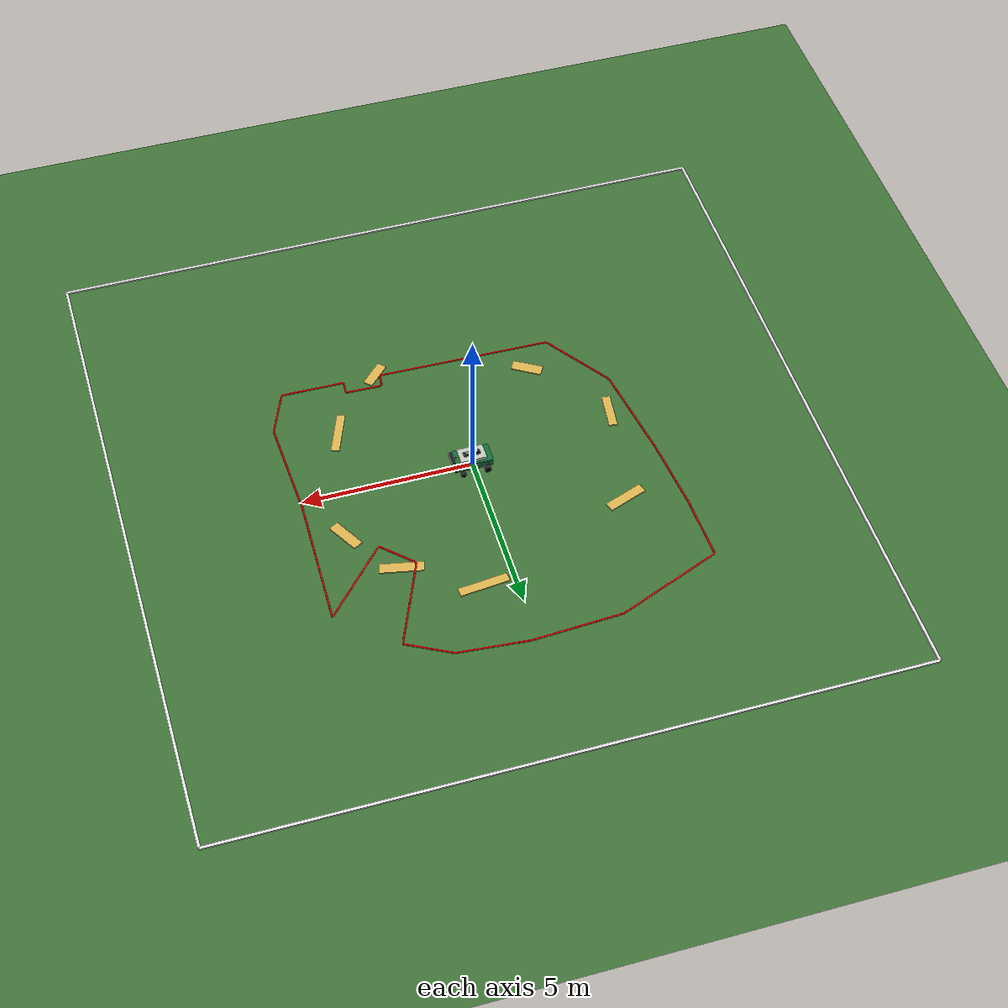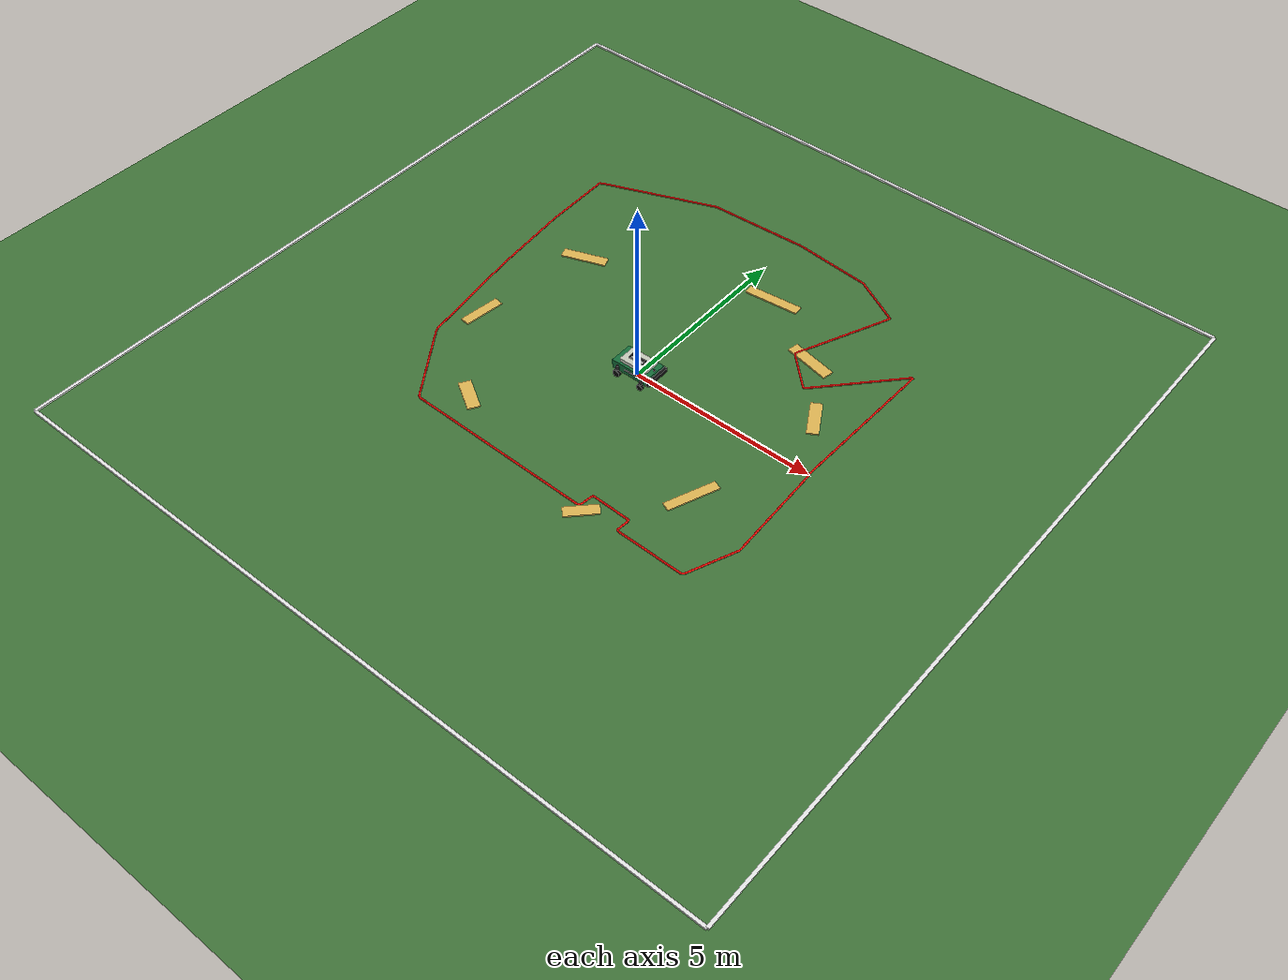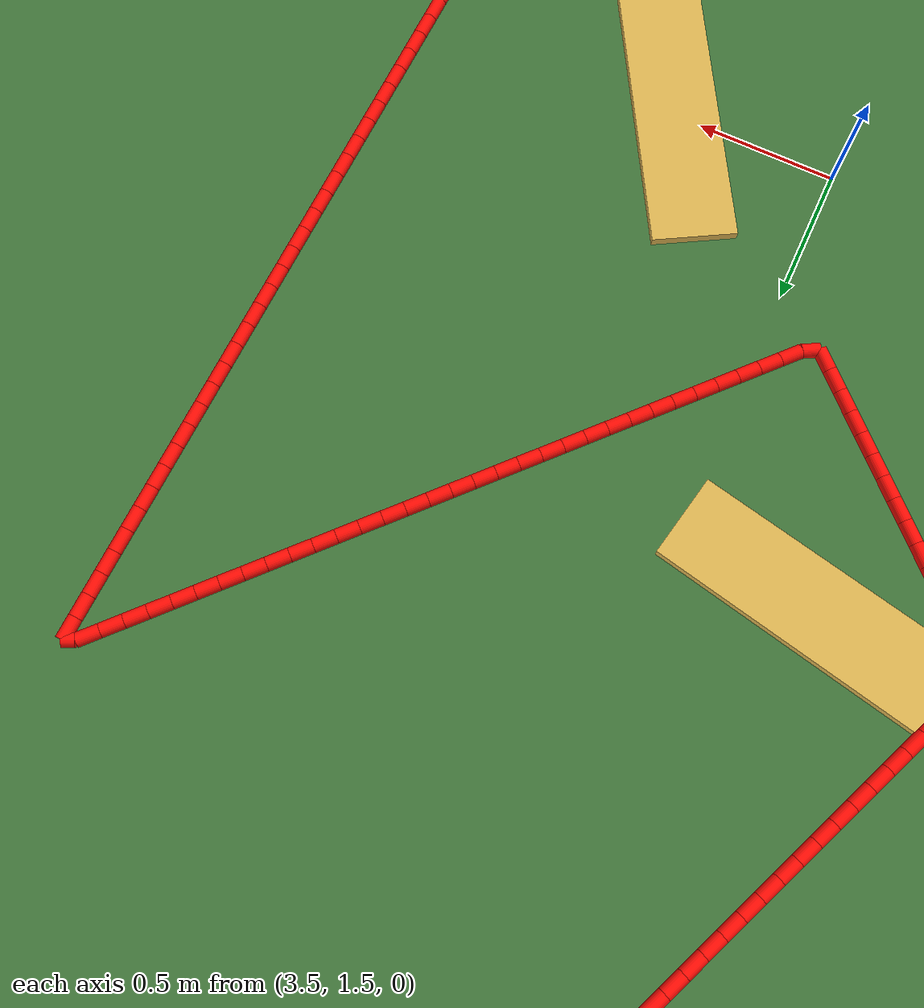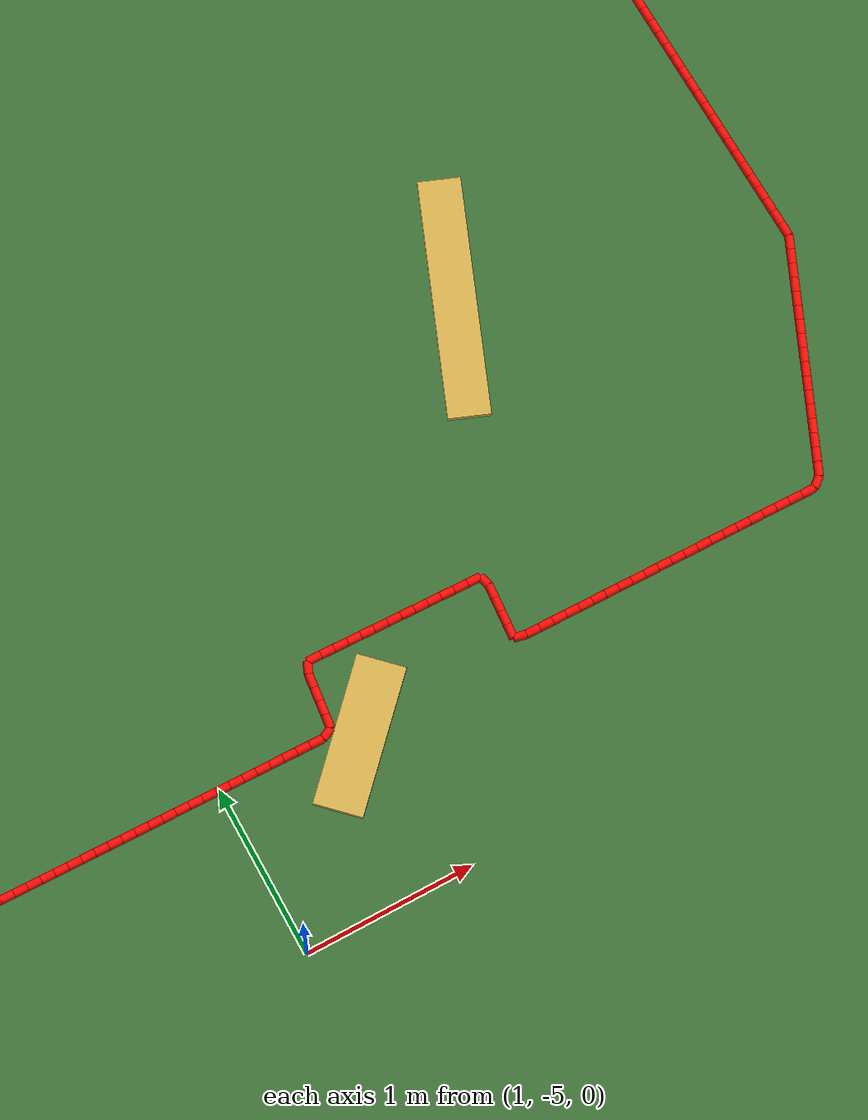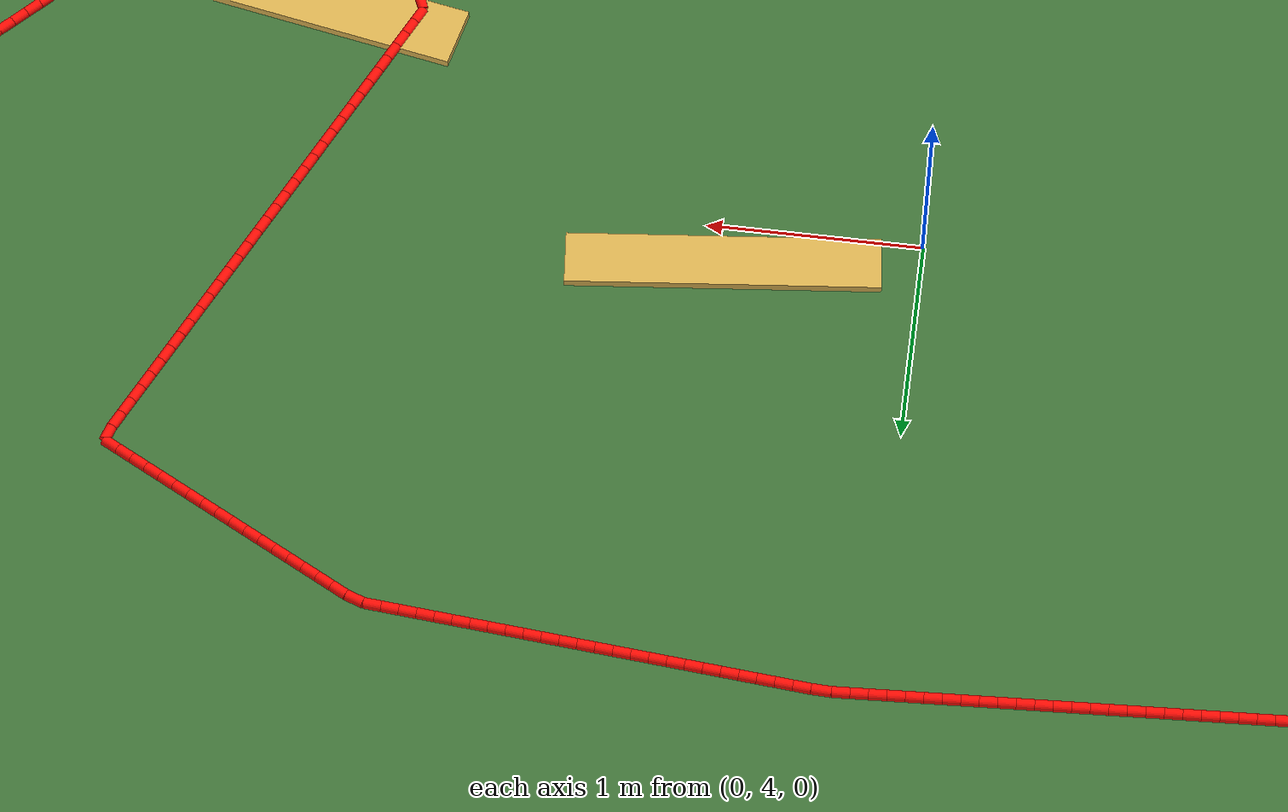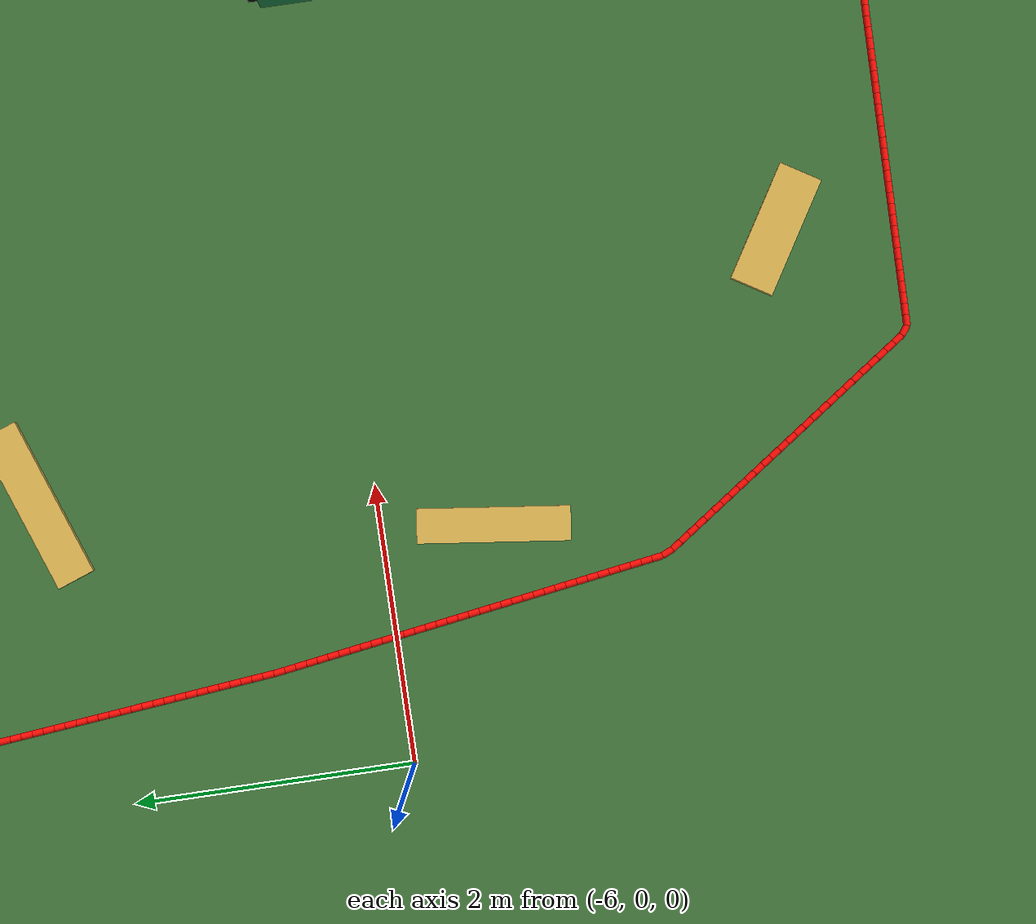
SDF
<?xml version="1.0"?>
<sdf version="1.6">
  <world name="mower_ackermann_4wd">
    <gravity>0 0 -9.8</gravity>
    <magnetic_field>6e-06 2.3e-05 -4.2e-05</magnetic_field>
    <atmosphere type="adiabatic"/>

    <physics name="default_physics" default="0" type="ode">
      <max_step_size>0.001</max_step_size>
      <real_time_factor>1.0</real_time_factor>
      <real_time_update_rate>1000</real_time_update_rate>
    </physics>

    <scene>
      <ambient>0.65 0.65 0.65 1</ambient>
      <background>0.85 0.90 0.96 1</background>
      <shadows>true</shadows>
    </scene>

    <light name="sun" type="directional">
      <cast_shadows>true</cast_shadows>
      <pose>0 0 10 0 0 0</pose>
      <diffuse>1.0 1.0 1.0 1</diffuse>
      <specular>0.35 0.35 0.35 1</specular>
      <attenuation>
        <range>1000</range>
        <constant>0.9</constant>
        <linear>0.01</linear>
        <quadratic>0.001</quadratic>
      </attenuation>
      <direction>-0.5 0.1 -0.9</direction>
    </light>

    <model name="ground_plane">
      <static>true</static>
      <link name="link">
        <collision name="collision">
          <geometry>
            <plane>
              <normal>0 0 1</normal>
              <size>40 40</size>
            </plane>
          </geometry>
          <surface>
            <friction>
              <ode>
                <mu>1.0</mu>
                <mu2>1.0</mu2>
              </ode>
            </friction>
          </surface>
        </collision>
        <visual name="visual">
          <geometry>
            <plane>
              <normal>0 0 1</normal>
              <size>40 40</size>
            </plane>
          </geometry>
          <material>
            <ambient>0.25 0.45 0.22 1</ambient>
            <diffuse>0.25 0.45 0.22 1</diffuse>
          </material>
        </visual>
      </link>
    </model>

    <model name="boundary">
      <static>true</static>
      <pose>0 0 0.025 0 0 0</pose>
      <link name="north">
        <pose>0 10 0 0 0 0</pose>
        <collision name="collision">
          <geometry>
            <box>
              <size>20 0.08 0.05</size>
            </box>
          </geometry>
        </collision>
        <visual name="visual">
          <geometry>
            <box>
              <size>20 0.08 0.05</size>
            </box>
          </geometry>
          <material>
            <ambient>0.9 0.9 0.9 1</ambient>
            <diffuse>0.9 0.9 0.9 1</diffuse>
          </material>
        </visual>
      </link>
      <link name="south">
        <pose>0 -10 0 0 0 0</pose>
        <collision name="collision">
          <geometry>
            <box>
              <size>20 0.08 0.05</size>
            </box>
          </geometry>
        </collision>
        <visual name="visual">
          <geometry>
            <box>
              <size>20 0.08 0.05</size>
            </box>
          </geometry>
          <material>
            <ambient>0.9 0.9 0.9 1</ambient>
            <diffuse>0.9 0.9 0.9 1</diffuse>
          </material>
        </visual>
      </link>
      <link name="east">
        <pose>10 0 0 0 0 0</pose>
        <collision name="collision">
          <geometry>
            <box>
              <size>0.08 20 0.05</size>
            </box>
          </geometry>
        </collision>
        <visual name="visual">
          <geometry>
            <box>
              <size>0.08 20 0.05</size>
            </box>
          </geometry>
          <material>
            <ambient>0.9 0.9 0.9 1</ambient>
            <diffuse>0.9 0.9 0.9 1</diffuse>
          </material>
        </visual>
      </link>
      <link name="west">
        <pose>-10 0 0 0 0 0</pose>
        <collision name="collision">
          <geometry>
            <box>
              <size>0.08 20 0.05</size>
            </box>
          </geometry>
        </collision>
        <visual name="visual">
          <geometry>
            <box>
              <size>0.08 20 0.05</size>
            </box>
          </geometry>
          <material>
            <ambient>0.9 0.9 0.9 1</ambient>
            <diffuse>0.9 0.9 0.9 1</diffuse>
          </material>
        </visual>
      </link>
    </model>

    <model name="low_bumpers">
      <static>true</static>
      <link name="bumper_0">
        <pose>-3.8 2.4 0.02 0 0 0.35</pose>
        <collision name="collision">
          <geometry>
            <box>
              <size>1.20 0.28 0.04</size>
            </box>
          </geometry>
        </collision>
        <visual name="visual">
          <geometry>
            <box>
              <size>1.20 0.28 0.04</size>
            </box>
          </geometry>
          <material>
            <ambient>0.78 0.62 0.28 1</ambient>
            <diffuse>0.86 0.70 0.32 1</diffuse>
          </material>
        </visual>
      </link>
      <link name="bumper_1">
        <pose>-2.6 -3.1 0.02 0 0 -0.55</pose>
        <collision name="collision">
          <geometry>
            <box>
              <size>0.90 0.32 0.04</size>
            </box>
          </geometry>
        </collision>
        <visual name="visual">
          <geometry>
            <box>
              <size>0.90 0.32 0.04</size>
            </box>
          </geometry>
          <material>
            <ambient>0.78 0.62 0.28 1</ambient>
            <diffuse>0.86 0.70 0.32 1</diffuse>
          </material>
        </visual>
      </link>
      <link name="bumper_2">
        <pose>3.4 -2.2 0.02 0 0 1.20</pose>
        <collision name="collision">
          <geometry>
            <box>
              <size>1.35 0.24 0.04</size>
            </box>
          </geometry>
        </collision>
        <visual name="visual">
          <geometry>
            <box>
              <size>1.35 0.24 0.04</size>
            </box>
          </geometry>
          <material>
            <ambient>0.78 0.62 0.28 1</ambient>
            <diffuse>0.86 0.70 0.32 1</diffuse>
          </material>
        </visual>
      </link>
      <link name="bumper_3">
        <pose>4.1 1.5 0.02 0 0 -1.05</pose>
        <collision name="collision">
          <geometry>
            <box>
              <size>1.00 0.30 0.04</size>
            </box>
          </geometry>
        </collision>
        <visual name="visual">
          <geometry>
            <box>
              <size>1.00 0.30 0.04</size>
            </box>
          </geometry>
          <material>
            <ambient>0.78 0.62 0.28 1</ambient>
            <diffuse>0.86 0.70 0.32 1</diffuse>
          </material>
        </visual>
      </link>
      <link name="bumper_4">
        <pose>0.9 4.2 0.02 0 0 0.10</pose>
        <collision name="collision">
          <geometry>
            <box>
              <size>1.45 0.26 0.04</size>
            </box>
          </geometry>
        </collision>
        <visual name="visual">
          <geometry>
            <box>
              <size>1.45 0.26 0.04</size>
            </box>
          </geometry>
          <material>
            <ambient>0.78 0.62 0.28 1</ambient>
            <diffuse>0.86 0.70 0.32 1</diffuse>
          </material>
        </visual>
      </link>
      <link name="bumper_5">
        <pose>-4.4 -0.8 0.02 0 0 1.45</pose>
        <collision name="collision">
          <geometry>
            <box>
              <size>1.10 0.25 0.04</size>
            </box>
          </geometry>
        </collision>
        <visual name="visual">
          <geometry>
            <box>
              <size>1.10 0.25 0.04</size>
            </box>
          </geometry>
          <material>
            <ambient>0.78 0.62 0.28 1</ambient>
            <diffuse>0.86 0.70 0.32 1</diffuse>
          </material>
        </visual>
      </link>
      <link name="bumper_6">
        <pose>1.8 -4.1 0.02 0 0 0.80</pose>
        <collision name="collision">
          <geometry>
            <box>
              <size>0.85 0.28 0.04</size>
            </box>
          </geometry>
        </collision>
        <visual name="visual">
          <geometry>
            <box>
              <size>0.85 0.28 0.04</size>
            </box>
          </geometry>
          <material>
            <ambient>0.78 0.62 0.28 1</ambient>
            <diffuse>0.86 0.70 0.32 1</diffuse>
          </material>
        </visual>
      </link>
      <link name="bumper_7">
        <pose>2.9 3.0 0.02 0 0 -0.20</pose>
        <collision name="collision">
          <geometry>
            <box>
              <size>1.25 0.30 0.04</size>
            </box>
          </geometry>
        </collision>
        <visual name="visual">
          <geometry>
            <box>
              <size>1.25 0.30 0.04</size>
            </box>
          </geometry>
          <material>
            <ambient>0.78 0.62 0.28 1</ambient>
            <diffuse>0.86 0.70 0.32 1</diffuse>
          </material>
        </visual>
      </link>
    </model>

    <include>
      <uri>model://boundary_points</uri>
      <pose>0 0 0 0 0 0</pose>
    </include>

    <include>
      <uri>model://ackermann_4wd_robot</uri>
      <pose>0 0 0.14 0 0 0</pose>
    </include>
  </world>
</sdf>

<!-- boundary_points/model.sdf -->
<sdf version="1.6">
  <model name="boundary_points">
    <static>true</static>
    <link name="boundary_visual_link">
      <visual name="boundary_segment_0">
        <pose>5.029120 0.045099 0.035000 0 1.570796 1.545044</pose>
        <geometry>
          <cylinder>
            <radius>0.025000</radius>
            <length>0.080000</length>
          </cylinder>
        </geometry>
        <material>
          <ambient>1.0 0.05 0.02 1</ambient>
          <diffuse>1.0 0.05 0.02 1</diffuse>
          <emissive>0.35 0.02 0.0 1</emissive>
        </material>
      </visual>
      <visual name="boundary_segment_1">
        <pose>5.031175 0.125073 0.035000 0 1.570796 1.545169</pose>
        <geometry>
          <cylinder>
            <radius>0.025000</radius>
            <length>0.080000</length>
          </cylinder>
        </geometry>
        <material>
          <ambient>1.0 0.05 0.02 1</ambient>
          <diffuse>1.0 0.05 0.02 1</diffuse>
          <emissive>0.35 0.02 0.0 1</emissive>
        </material>
      </visual>
      <visual name="boundary_segment_2">
        <pose>5.033230 0.205047 0.035000 0 1.570796 1.545043</pose>
        <geometry>
          <cylinder>
            <radius>0.025000</radius>
            <length>0.080000</length>
          </cylinder>
        </geometry>
        <material>
          <ambient>1.0 0.05 0.02 1</ambient>
          <diffuse>1.0 0.05 0.02 1</diffuse>
          <emissive>0.35 0.02 0.0 1</emissive>
        </material>
      </visual>
      <visual name="boundary_segment_3">
        <pose>5.035290 0.285020 0.035000 0 1.570796 1.545044</pose>
        <geometry>
          <cylinder>
            <radius>0.025000</radius>
            <length>0.080001</length>
          </cylinder>
        </geometry>
        <material>
          <ambient>1.0 0.05 0.02 1</ambient>
          <diffuse>1.0 0.05 0.02 1</diffuse>
          <emissive>0.35 0.02 0.0 1</emissive>
        </material>
      </visual>
      <visual name="boundary_segment_4">
        <pose>5.037345 0.364993 0.035000 0 1.570796 1.545168</pose>
        <geometry>
          <cylinder>
            <radius>0.025000</radius>
            <length>0.079999</length>
          </cylinder>
        </geometry>
        <material>
          <ambient>1.0 0.05 0.02 1</ambient>
          <diffuse>1.0 0.05 0.02 1</diffuse>
          <emissive>0.35 0.02 0.0 1</emissive>
        </material>
      </visual>
      <visual name="boundary_segment_5">
        <pose>5.039400 0.444967 0.035000 0 1.570796 1.545044</pose>
        <geometry>
          <cylinder>
            <radius>0.025000</radius>
            <length>0.080001</length>
          </cylinder>
        </geometry>
        <material>
          <ambient>1.0 0.05 0.02 1</ambient>
          <diffuse>1.0 0.05 0.02 1</diffuse>
          <emissive>0.35 0.02 0.0 1</emissive>
        </material>
      </visual>
      <visual name="boundary_segment_6">
        <pose>5.041460 0.524941 0.035000 0 1.570796 1.545043</pose>
        <geometry>
          <cylinder>
            <radius>0.025000</radius>
            <length>0.080000</length>
          </cylinder>
        </geometry>
        <material>
          <ambient>1.0 0.05 0.02 1</ambient>
          <diffuse>1.0 0.05 0.02 1</diffuse>
          <emissive>0.35 0.02 0.0 1</emissive>
        </material>
      </visual>
      <visual name="boundary_segment_7">
        <pose>5.043515 0.604914 0.035000 0 1.570796 1.545169</pose>
        <geometry>
          <cylinder>
            <radius>0.025000</radius>
            <length>0.080000</length>
          </cylinder>
        </geometry>
        <material>
          <ambient>1.0 0.05 0.02 1</ambient>
          <diffuse>1.0 0.05 0.02 1</diffuse>
          <emissive>0.35 0.02 0.0 1</emissive>
        </material>
      </visual>
      <visual name="boundary_segment_8">
        <pose>5.045570 0.684888 0.035000 0 1.570796 1.545044</pose>
        <geometry>
          <cylinder>
            <radius>0.025000</radius>
            <length>0.080001</length>
          </cylinder>
        </geometry>
        <material>
          <ambient>1.0 0.05 0.02 1</ambient>
          <diffuse>1.0 0.05 0.02 1</diffuse>
          <emissive>0.35 0.02 0.0 1</emissive>
        </material>
      </visual>
      <visual name="boundary_segment_9">
        <pose>5.047625 0.764862 0.035000 0 1.570796 1.545168</pose>
        <geometry>
          <cylinder>
            <radius>0.025000</radius>
            <length>0.079999</length>
          </cylinder>
        </geometry>
        <material>
          <ambient>1.0 0.05 0.02 1</ambient>
          <diffuse>1.0 0.05 0.02 1</diffuse>
          <emissive>0.35 0.02 0.0 1</emissive>
        </material>
      </visual>
      <visual name="boundary_segment_10">
        <pose>5.049680 0.844835 0.035000 0 1.570796 1.545044</pose>
        <geometry>
          <cylinder>
            <radius>0.025000</radius>
            <length>0.080001</length>
          </cylinder>
        </geometry>
        <material>
          <ambient>1.0 0.05 0.02 1</ambient>
          <diffuse>1.0 0.05 0.02 1</diffuse>
          <emissive>0.35 0.02 0.0 1</emissive>
        </material>
      </visual>
      <visual name="boundary_segment_11">
        <pose>5.051740 0.924808 0.035000 0 1.570796 1.545043</pose>
        <geometry>
          <cylinder>
            <radius>0.025000</radius>
            <length>0.080000</length>
          </cylinder>
        </geometry>
        <material>
          <ambient>1.0 0.05 0.02 1</ambient>
          <diffuse>1.0 0.05 0.02 1</diffuse>
          <emissive>0.35 0.02 0.0 1</emissive>
        </material>
      </visual>
      <visual name="boundary_segment_12">
        <pose>5.053795 1.004782 0.035000 0 1.570796 1.545169</pose>
        <geometry>
          <cylinder>
            <radius>0.025000</radius>
            <length>0.080001</length>
          </cylinder>
        </geometry>
        <material>
          <ambient>1.0 0.05 0.02 1</ambient>
          <diffuse>1.0 0.05 0.02 1</diffuse>
          <emissive>0.35 0.02 0.0 1</emissive>
        </material>
      </visual>
      <visual name="boundary_segment_13">
        <pose>5.055850 1.084755 0.035000 0 1.570796 1.545042</pose>
        <geometry>
          <cylinder>
            <radius>0.025000</radius>
            <length>0.079997</length>
          </cylinder>
        </geometry>
        <material>
          <ambient>1.0 0.05 0.02 1</ambient>
          <diffuse>1.0 0.05 0.02 1</diffuse>
          <emissive>0.35 0.02 0.0 1</emissive>
        </material>
      </visual>
      <visual name="boundary_segment_14">
        <pose>5.057910 1.164730 0.035000 0 1.570796 1.545046</pose>
        <geometry>
          <cylinder>
            <radius>0.025000</radius>
            <length>0.080007</length>
          </cylinder>
        </geometry>
        <material>
          <ambient>1.0 0.05 0.02 1</ambient>
          <diffuse>1.0 0.05 0.02 1</diffuse>
          <emissive>0.35 0.02 0.0 1</emissive>
        </material>
      </visual>
      <visual name="boundary_segment_15">
        <pose>5.059965 1.244705 0.035000 0 1.570796 1.545167</pose>
        <geometry>
          <cylinder>
            <radius>0.025000</radius>
            <length>0.079996</length>
          </cylinder>
        </geometry>
        <material>
          <ambient>1.0 0.05 0.02 1</ambient>
          <diffuse>1.0 0.05 0.02 1</diffuse>
          <emissive>0.35 0.02 0.0 1</emissive>
        </material>
      </visual>
      <visual name="boundary_segment_16">
        <pose>5.062020 1.324675 0.035000 0 1.570796 1.545042</pose>
        <geometry>
          <cylinder>
            <radius>0.025000</radius>
            <length>0.079997</length>
          </cylinder>
        </geometry>
        <material>
          <ambient>1.0 0.05 0.02 1</ambient>
          <diffuse>1.0 0.05 0.02 1</diffuse>
          <emissive>0.35 0.02 0.0 1</emissive>
        </material>
      </visual>
      <visual name="boundary_segment_17">
        <pose>5.064080 1.404650 0.035000 0 1.570796 1.545046</pose>
        <geometry>
          <cylinder>
            <radius>0.025000</radius>
            <length>0.080007</length>
          </cylinder>
        </geometry>
        <material>
          <ambient>1.0 0.05 0.02 1</ambient>
          <diffuse>1.0 0.05 0.02 1</diffuse>
          <emissive>0.35 0.02 0.0 1</emissive>
        </material>
      </visual>
      <visual name="boundary_segment_18">
        <pose>5.066135 1.484625 0.035000 0 1.570796 1.545167</pose>
        <geometry>
          <cylinder>
            <radius>0.025000</radius>
            <length>0.079996</length>
          </cylinder>
        </geometry>
        <material>
          <ambient>1.0 0.05 0.02 1</ambient>
          <diffuse>1.0 0.05 0.02 1</diffuse>
          <emissive>0.35 0.02 0.0 1</emissive>
        </material>
      </visual>
      <visual name="boundary_segment_19">
        <pose>5.068190 1.564595 0.035000 0 1.570796 1.545042</pose>
        <geometry>
          <cylinder>
            <radius>0.025000</radius>
            <length>0.079997</length>
          </cylinder>
        </geometry>
        <material>
          <ambient>1.0 0.05 0.02 1</ambient>
          <diffuse>1.0 0.05 0.02 1</diffuse>
          <emissive>0.35 0.02 0.0 1</emissive>
        </material>
      </visual>
      <visual name="boundary_segment_20">
        <pose>5.070245 1.644570 0.035000 0 1.570796 1.545171</pose>
        <geometry>
          <cylinder>
            <radius>0.025000</radius>
            <length>0.080006</length>
          </cylinder>
        </geometry>
        <material>
          <ambient>1.0 0.05 0.02 1</ambient>
          <diffuse>1.0 0.05 0.02 1</diffuse>
          <emissive>0.35 0.02 0.0 1</emissive>
        </material>
      </visual>
      <visual name="boundary_segment_21">
        <pose>5.072300 1.724545 0.035000 0 1.570796 1.545042</pose>
        <geometry>
          <cylinder>
            <radius>0.025000</radius>
            <length>0.079997</length>
          </cylinder>
        </geometry>
        <material>
          <ambient>1.0 0.05 0.02 1</ambient>
          <diffuse>1.0 0.05 0.02 1</diffuse>
          <emissive>0.35 0.02 0.0 1</emissive>
        </material>
      </visual>
      <visual name="boundary_segment_22">
        <pose>5.074360 1.804515 0.035000 0 1.570796 1.545042</pose>
        <geometry>
          <cylinder>
            <radius>0.025000</radius>
            <length>0.079997</length>
          </cylinder>
        </geometry>
        <material>
          <ambient>1.0 0.05 0.02 1</ambient>
          <diffuse>1.0 0.05 0.02 1</diffuse>
          <emissive>0.35 0.02 0.0 1</emissive>
        </material>
      </visual>
      <visual name="boundary_segment_23">
        <pose>5.076415 1.884490 0.035000 0 1.570796 1.545171</pose>
        <geometry>
          <cylinder>
            <radius>0.025000</radius>
            <length>0.080006</length>
          </cylinder>
        </geometry>
        <material>
          <ambient>1.0 0.05 0.02 1</ambient>
          <diffuse>1.0 0.05 0.02 1</diffuse>
          <emissive>0.35 0.02 0.0 1</emissive>
        </material>
      </visual>
      <visual name="boundary_segment_24">
        <pose>5.078470 1.964465 0.035000 0 1.570796 1.545042</pose>
        <geometry>
          <cylinder>
            <radius>0.025000</radius>
            <length>0.079997</length>
          </cylinder>
        </geometry>
        <material>
          <ambient>1.0 0.05 0.02 1</ambient>
          <diffuse>1.0 0.05 0.02 1</diffuse>
          <emissive>0.35 0.02 0.0 1</emissive>
        </material>
      </visual>
      <visual name="boundary_segment_25">
        <pose>5.080530 2.044440 0.035000 0 1.570796 1.545046</pose>
        <geometry>
          <cylinder>
            <radius>0.025000</radius>
            <length>0.080007</length>
          </cylinder>
        </geometry>
        <material>
          <ambient>1.0 0.05 0.02 1</ambient>
          <diffuse>1.0 0.05 0.02 1</diffuse>
          <emissive>0.35 0.02 0.0 1</emissive>
        </material>
      </visual>
      <visual name="boundary_segment_26">
        <pose>5.082585 2.124415 0.035000 0 1.570796 1.545167</pose>
        <geometry>
          <cylinder>
            <radius>0.025000</radius>
            <length>0.079996</length>
          </cylinder>
        </geometry>
        <material>
          <ambient>1.0 0.05 0.02 1</ambient>
          <diffuse>1.0 0.05 0.02 1</diffuse>
          <emissive>0.35 0.02 0.0 1</emissive>
        </material>
      </visual>
      <visual name="boundary_segment_27">
        <pose>5.084640 2.204385 0.035000 0 1.570796 1.545042</pose>
        <geometry>
          <cylinder>
            <radius>0.025000</radius>
            <length>0.079997</length>
          </cylinder>
        </geometry>
        <material>
          <ambient>1.0 0.05 0.02 1</ambient>
          <diffuse>1.0 0.05 0.02 1</diffuse>
          <emissive>0.35 0.02 0.0 1</emissive>
        </material>
      </visual>
      <visual name="boundary_segment_28">
        <pose>5.086695 2.284360 0.035000 0 1.570796 1.545171</pose>
        <geometry>
          <cylinder>
            <radius>0.025000</radius>
            <length>0.080006</length>
          </cylinder>
        </geometry>
        <material>
          <ambient>1.0 0.05 0.02 1</ambient>
          <diffuse>1.0 0.05 0.02 1</diffuse>
          <emissive>0.35 0.02 0.0 1</emissive>
        </material>
      </visual>
      <visual name="boundary_segment_29">
        <pose>5.088750 2.364335 0.035000 0 1.570796 1.545042</pose>
        <geometry>
          <cylinder>
            <radius>0.025000</radius>
            <length>0.079997</length>
          </cylinder>
        </geometry>
        <material>
          <ambient>1.0 0.05 0.02 1</ambient>
          <diffuse>1.0 0.05 0.02 1</diffuse>
          <emissive>0.35 0.02 0.0 1</emissive>
        </material>
      </visual>
      <visual name="boundary_segment_30">
        <pose>5.090810 2.444305 0.035000 0 1.570796 1.545042</pose>
        <geometry>
          <cylinder>
            <radius>0.025000</radius>
            <length>0.079997</length>
          </cylinder>
        </geometry>
        <material>
          <ambient>1.0 0.05 0.02 1</ambient>
          <diffuse>1.0 0.05 0.02 1</diffuse>
          <emissive>0.35 0.02 0.0 1</emissive>
        </material>
      </visual>
      <visual name="boundary_segment_31">
        <pose>5.092865 2.524280 0.035000 0 1.570796 1.545171</pose>
        <geometry>
          <cylinder>
            <radius>0.025000</radius>
            <length>0.080006</length>
          </cylinder>
        </geometry>
        <material>
          <ambient>1.0 0.05 0.02 1</ambient>
          <diffuse>1.0 0.05 0.02 1</diffuse>
          <emissive>0.35 0.02 0.0 1</emissive>
        </material>
      </visual>
      <visual name="boundary_segment_32">
        <pose>5.094920 2.604255 0.035000 0 1.570796 1.545042</pose>
        <geometry>
          <cylinder>
            <radius>0.025000</radius>
            <length>0.079997</length>
          </cylinder>
        </geometry>
        <material>
          <ambient>1.0 0.05 0.02 1</ambient>
          <diffuse>1.0 0.05 0.02 1</diffuse>
          <emissive>0.35 0.02 0.0 1</emissive>
        </material>
      </visual>
      <visual name="boundary_segment_33">
        <pose>5.096980 2.684225 0.035000 0 1.570796 1.545042</pose>
        <geometry>
          <cylinder>
            <radius>0.025000</radius>
            <length>0.079997</length>
          </cylinder>
        </geometry>
        <material>
          <ambient>1.0 0.05 0.02 1</ambient>
          <diffuse>1.0 0.05 0.02 1</diffuse>
          <emissive>0.35 0.02 0.0 1</emissive>
        </material>
      </visual>
      <visual name="boundary_segment_34">
        <pose>5.099035 2.764200 0.035000 0 1.570796 1.545171</pose>
        <geometry>
          <cylinder>
            <radius>0.025000</radius>
            <length>0.080006</length>
          </cylinder>
        </geometry>
        <material>
          <ambient>1.0 0.05 0.02 1</ambient>
          <diffuse>1.0 0.05 0.02 1</diffuse>
          <emissive>0.35 0.02 0.0 1</emissive>
        </material>
      </visual>
      <visual name="boundary_segment_35">
        <pose>5.101090 2.844175 0.035000 0 1.570796 1.545042</pose>
        <geometry>
          <cylinder>
            <radius>0.025000</radius>
            <length>0.079997</length>
          </cylinder>
        </geometry>
        <material>
          <ambient>1.0 0.05 0.02 1</ambient>
          <diffuse>1.0 0.05 0.02 1</diffuse>
          <emissive>0.35 0.02 0.0 1</emissive>
        </material>
      </visual>
      <visual name="boundary_segment_36">
        <pose>5.103150 2.924145 0.035000 0 1.570796 1.545042</pose>
        <geometry>
          <cylinder>
            <radius>0.025000</radius>
            <length>0.079997</length>
          </cylinder>
        </geometry>
        <material>
          <ambient>1.0 0.05 0.02 1</ambient>
          <diffuse>1.0 0.05 0.02 1</diffuse>
          <emissive>0.35 0.02 0.0 1</emissive>
        </material>
      </visual>
      <visual name="boundary_segment_37">
        <pose>5.105205 3.004120 0.035000 0 1.570796 1.545171</pose>
        <geometry>
          <cylinder>
            <radius>0.025000</radius>
            <length>0.080006</length>
          </cylinder>
        </geometry>
        <material>
          <ambient>1.0 0.05 0.02 1</ambient>
          <diffuse>1.0 0.05 0.02 1</diffuse>
          <emissive>0.35 0.02 0.0 1</emissive>
        </material>
      </visual>
      <visual name="boundary_segment_38">
        <pose>5.107260 3.084095 0.035000 0 1.570796 1.545042</pose>
        <geometry>
          <cylinder>
            <radius>0.025000</radius>
            <length>0.079997</length>
          </cylinder>
        </geometry>
        <material>
          <ambient>1.0 0.05 0.02 1</ambient>
          <diffuse>1.0 0.05 0.02 1</diffuse>
          <emissive>0.35 0.02 0.0 1</emissive>
        </material>
      </visual>
      <visual name="boundary_segment_39">
        <pose>5.109315 3.164070 0.035000 0 1.570796 1.545171</pose>
        <geometry>
          <cylinder>
            <radius>0.025000</radius>
            <length>0.080006</length>
          </cylinder>
        </geometry>
        <material>
          <ambient>1.0 0.05 0.02 1</ambient>
          <diffuse>1.0 0.05 0.02 1</diffuse>
          <emissive>0.35 0.02 0.0 1</emissive>
        </material>
      </visual>
      <visual name="boundary_segment_40">
        <pose>5.111370 3.244045 0.035000 0 1.570796 1.545042</pose>
        <geometry>
          <cylinder>
            <radius>0.025000</radius>
            <length>0.079997</length>
          </cylinder>
        </geometry>
        <material>
          <ambient>1.0 0.05 0.02 1</ambient>
          <diffuse>1.0 0.05 0.02 1</diffuse>
          <emissive>0.35 0.02 0.0 1</emissive>
        </material>
      </visual>
      <visual name="boundary_segment_41">
        <pose>5.113430 3.324015 0.035000 0 1.570796 1.545042</pose>
        <geometry>
          <cylinder>
            <radius>0.025000</radius>
            <length>0.079997</length>
          </cylinder>
        </geometry>
        <material>
          <ambient>1.0 0.05 0.02 1</ambient>
          <diffuse>1.0 0.05 0.02 1</diffuse>
          <emissive>0.35 0.02 0.0 1</emissive>
        </material>
      </visual>
      <visual name="boundary_segment_42">
        <pose>5.115485 3.403990 0.035000 0 1.570796 1.545171</pose>
        <geometry>
          <cylinder>
            <radius>0.025000</radius>
            <length>0.080006</length>
          </cylinder>
        </geometry>
        <material>
          <ambient>1.0 0.05 0.02 1</ambient>
          <diffuse>1.0 0.05 0.02 1</diffuse>
          <emissive>0.35 0.02 0.0 1</emissive>
        </material>
      </visual>
      <visual name="boundary_segment_43">
        <pose>5.117540 3.483965 0.035000 0 1.570796 1.545042</pose>
        <geometry>
          <cylinder>
            <radius>0.025000</radius>
            <length>0.079997</length>
          </cylinder>
        </geometry>
        <material>
          <ambient>1.0 0.05 0.02 1</ambient>
          <diffuse>1.0 0.05 0.02 1</diffuse>
          <emissive>0.35 0.02 0.0 1</emissive>
        </material>
      </visual>
      <visual name="boundary_segment_44">
        <pose>5.119600 3.563935 0.035000 0 1.570796 1.545042</pose>
        <geometry>
          <cylinder>
            <radius>0.025000</radius>
            <length>0.079997</length>
          </cylinder>
        </geometry>
        <material>
          <ambient>1.0 0.05 0.02 1</ambient>
          <diffuse>1.0 0.05 0.02 1</diffuse>
          <emissive>0.35 0.02 0.0 1</emissive>
        </material>
      </visual>
      <visual name="boundary_segment_45">
        <pose>5.121655 3.643910 0.035000 0 1.570796 1.545171</pose>
        <geometry>
          <cylinder>
            <radius>0.025000</radius>
            <length>0.080006</length>
          </cylinder>
        </geometry>
        <material>
          <ambient>1.0 0.05 0.02 1</ambient>
          <diffuse>1.0 0.05 0.02 1</diffuse>
          <emissive>0.35 0.02 0.0 1</emissive>
        </material>
      </visual>
      <visual name="boundary_segment_46">
        <pose>5.123710 3.723885 0.035000 0 1.570796 1.545042</pose>
        <geometry>
          <cylinder>
            <radius>0.025000</radius>
            <length>0.079997</length>
          </cylinder>
        </geometry>
        <material>
          <ambient>1.0 0.05 0.02 1</ambient>
          <diffuse>1.0 0.05 0.02 1</diffuse>
          <emissive>0.35 0.02 0.0 1</emissive>
        </material>
      </visual>
      <visual name="boundary_segment_47">
        <pose>5.125765 3.803855 0.035000 0 1.570796 1.545167</pose>
        <geometry>
          <cylinder>
            <radius>0.025000</radius>
            <length>0.079996</length>
          </cylinder>
        </geometry>
        <material>
          <ambient>1.0 0.05 0.02 1</ambient>
          <diffuse>1.0 0.05 0.02 1</diffuse>
          <emissive>0.35 0.02 0.0 1</emissive>
        </material>
      </visual>
      <visual name="boundary_segment_48">
        <pose>5.127820 3.883830 0.035000 0 1.570796 1.545046</pose>
        <geometry>
          <cylinder>
            <radius>0.025000</radius>
            <length>0.080007</length>
          </cylinder>
        </geometry>
        <material>
          <ambient>1.0 0.05 0.02 1</ambient>
          <diffuse>1.0 0.05 0.02 1</diffuse>
          <emissive>0.35 0.02 0.0 1</emissive>
        </material>
      </visual>
      <visual name="boundary_segment_49">
        <pose>5.129880 3.963805 0.035000 0 1.570796 1.545042</pose>
        <geometry>
          <cylinder>
            <radius>0.025000</radius>
            <length>0.079997</length>
          </cylinder>
        </geometry>
        <material>
          <ambient>1.0 0.05 0.02 1</ambient>
          <diffuse>1.0 0.05 0.02 1</diffuse>
          <emissive>0.35 0.02 0.0 1</emissive>
        </material>
      </visual>
      <visual name="boundary_segment_50">
        <pose>5.131935 4.043775 0.035000 0 1.570796 1.545167</pose>
        <geometry>
          <cylinder>
            <radius>0.025000</radius>
            <length>0.079996</length>
          </cylinder>
        </geometry>
        <material>
          <ambient>1.0 0.05 0.02 1</ambient>
          <diffuse>1.0 0.05 0.02 1</diffuse>
          <emissive>0.35 0.02 0.0 1</emissive>
        </material>
      </visual>
      <visual name="boundary_segment_51">
        <pose>5.113055 4.074670 0.035000 0 1.570796 -2.713206</pose>
        <geometry>
          <cylinder>
            <radius>0.025000</radius>
            <length>0.043765</length>
          </cylinder>
        </geometry>
        <material>
          <ambient>1.0 0.05 0.02 1</ambient>
          <diffuse>1.0 0.05 0.02 1</diffuse>
          <emissive>0.35 0.02 0.0 1</emissive>
        </material>
      </visual>
      <visual name="boundary_segment_52">
        <pose>5.066160 4.036055 0.035000 0 1.570796 -2.311369</pose>
        <geometry>
          <cylinder>
            <radius>0.025000</radius>
            <length>0.080005</length>
          </cylinder>
        </geometry>
        <material>
          <ambient>1.0 0.05 0.02 1</ambient>
          <diffuse>1.0 0.05 0.02 1</diffuse>
          <emissive>0.35 0.02 0.0 1</emissive>
        </material>
      </visual>
      <visual name="boundary_segment_53">
        <pose>5.012180 3.977010 0.035000 0 1.570796 -2.311454</pose>
        <geometry>
          <cylinder>
            <radius>0.025000</radius>
            <length>0.079997</length>
          </cylinder>
        </geometry>
        <material>
          <ambient>1.0 0.05 0.02 1</ambient>
          <diffuse>1.0 0.05 0.02 1</diffuse>
          <emissive>0.35 0.02 0.0 1</emissive>
        </material>
      </visual>
      <visual name="boundary_segment_54">
        <pose>4.958200 3.917965 0.035000 0 1.570796 -2.311369</pose>
        <geometry>
          <cylinder>
            <radius>0.025000</radius>
            <length>0.080005</length>
          </cylinder>
        </geometry>
        <material>
          <ambient>1.0 0.05 0.02 1</ambient>
          <diffuse>1.0 0.05 0.02 1</diffuse>
          <emissive>0.35 0.02 0.0 1</emissive>
        </material>
      </visual>
      <visual name="boundary_segment_55">
        <pose>4.904220 3.858920 0.035000 0 1.570796 -2.311454</pose>
        <geometry>
          <cylinder>
            <radius>0.025000</radius>
            <length>0.079997</length>
          </cylinder>
        </geometry>
        <material>
          <ambient>1.0 0.05 0.02 1</ambient>
          <diffuse>1.0 0.05 0.02 1</diffuse>
          <emissive>0.35 0.02 0.0 1</emissive>
        </material>
      </visual>
      <visual name="boundary_segment_56">
        <pose>4.850245 3.799880 0.035000 0 1.570796 -2.311361</pose>
        <geometry>
          <cylinder>
            <radius>0.025000</radius>
            <length>0.079991</length>
          </cylinder>
        </geometry>
        <material>
          <ambient>1.0 0.05 0.02 1</ambient>
          <diffuse>1.0 0.05 0.02 1</diffuse>
          <emissive>0.35 0.02 0.0 1</emissive>
        </material>
      </visual>
      <visual name="boundary_segment_57">
        <pose>4.796270 3.740835 0.035000 0 1.570796 -2.311369</pose>
        <geometry>
          <cylinder>
            <radius>0.025000</radius>
            <length>0.080005</length>
          </cylinder>
        </geometry>
        <material>
          <ambient>1.0 0.05 0.02 1</ambient>
          <diffuse>1.0 0.05 0.02 1</diffuse>
          <emissive>0.35 0.02 0.0 1</emissive>
        </material>
      </visual>
      <visual name="boundary_segment_58">
        <pose>4.742290 3.681790 0.035000 0 1.570796 -2.311454</pose>
        <geometry>
          <cylinder>
            <radius>0.025000</radius>
            <length>0.079997</length>
          </cylinder>
        </geometry>
        <material>
          <ambient>1.0 0.05 0.02 1</ambient>
          <diffuse>1.0 0.05 0.02 1</diffuse>
          <emissive>0.35 0.02 0.0 1</emissive>
        </material>
      </visual>
      <visual name="boundary_segment_59">
        <pose>4.688310 3.622745 0.035000 0 1.570796 -2.311369</pose>
        <geometry>
          <cylinder>
            <radius>0.025000</radius>
            <length>0.080005</length>
          </cylinder>
        </geometry>
        <material>
          <ambient>1.0 0.05 0.02 1</ambient>
          <diffuse>1.0 0.05 0.02 1</diffuse>
          <emissive>0.35 0.02 0.0 1</emissive>
        </material>
      </visual>
      <visual name="boundary_segment_60">
        <pose>4.634330 3.563700 0.035000 0 1.570796 -2.311454</pose>
        <geometry>
          <cylinder>
            <radius>0.025000</radius>
            <length>0.079997</length>
          </cylinder>
        </geometry>
        <material>
          <ambient>1.0 0.05 0.02 1</ambient>
          <diffuse>1.0 0.05 0.02 1</diffuse>
          <emissive>0.35 0.02 0.0 1</emissive>
        </material>
      </visual>
      <visual name="boundary_segment_61">
        <pose>4.580350 3.504655 0.035000 0 1.570796 -2.311369</pose>
        <geometry>
          <cylinder>
            <radius>0.025000</radius>
            <length>0.080005</length>
          </cylinder>
        </geometry>
        <material>
          <ambient>1.0 0.05 0.02 1</ambient>
          <diffuse>1.0 0.05 0.02 1</diffuse>
          <emissive>0.35 0.02 0.0 1</emissive>
        </material>
      </visual>
      <visual name="boundary_segment_62">
        <pose>4.526370 3.445610 0.035000 0 1.570796 -2.311454</pose>
        <geometry>
          <cylinder>
            <radius>0.025000</radius>
            <length>0.079997</length>
          </cylinder>
        </geometry>
        <material>
          <ambient>1.0 0.05 0.02 1</ambient>
          <diffuse>1.0 0.05 0.02 1</diffuse>
          <emissive>0.35 0.02 0.0 1</emissive>
        </material>
      </visual>
      <visual name="boundary_segment_63">
        <pose>4.472390 3.386565 0.035000 0 1.570796 -2.311369</pose>
        <geometry>
          <cylinder>
            <radius>0.025000</radius>
            <length>0.080005</length>
          </cylinder>
        </geometry>
        <material>
          <ambient>1.0 0.05 0.02 1</ambient>
          <diffuse>1.0 0.05 0.02 1</diffuse>
          <emissive>0.35 0.02 0.0 1</emissive>
        </material>
      </visual>
      <visual name="boundary_segment_64">
        <pose>4.418415 3.327520 0.035000 0 1.570796 -2.311361</pose>
        <geometry>
          <cylinder>
            <radius>0.025000</radius>
            <length>0.079991</length>
          </cylinder>
        </geometry>
        <material>
          <ambient>1.0 0.05 0.02 1</ambient>
          <diffuse>1.0 0.05 0.02 1</diffuse>
          <emissive>0.35 0.02 0.0 1</emissive>
        </material>
      </visual>
      <visual name="boundary_segment_65">
        <pose>4.364440 3.268475 0.035000 0 1.570796 -2.311369</pose>
        <geometry>
          <cylinder>
            <radius>0.025000</radius>
            <length>0.080005</length>
          </cylinder>
        </geometry>
        <material>
          <ambient>1.0 0.05 0.02 1</ambient>
          <diffuse>1.0 0.05 0.02 1</diffuse>
          <emissive>0.35 0.02 0.0 1</emissive>
        </material>
      </visual>
      <visual name="boundary_segment_66">
        <pose>4.310460 3.209430 0.035000 0 1.570796 -2.311454</pose>
        <geometry>
          <cylinder>
            <radius>0.025000</radius>
            <length>0.079997</length>
          </cylinder>
        </geometry>
        <material>
          <ambient>1.0 0.05 0.02 1</ambient>
          <diffuse>1.0 0.05 0.02 1</diffuse>
          <emissive>0.35 0.02 0.0 1</emissive>
        </material>
      </visual>
      <visual name="boundary_segment_67">
        <pose>4.256480 3.150385 0.035000 0 1.570796 -2.311369</pose>
        <geometry>
          <cylinder>
            <radius>0.025000</radius>
            <length>0.080005</length>
          </cylinder>
        </geometry>
        <material>
          <ambient>1.0 0.05 0.02 1</ambient>
          <diffuse>1.0 0.05 0.02 1</diffuse>
          <emissive>0.35 0.02 0.0 1</emissive>
        </material>
      </visual>
      <visual name="boundary_segment_68">
        <pose>4.202500 3.091340 0.035000 0 1.570796 -2.311454</pose>
        <geometry>
          <cylinder>
            <radius>0.025000</radius>
            <length>0.079997</length>
          </cylinder>
        </geometry>
        <material>
          <ambient>1.0 0.05 0.02 1</ambient>
          <diffuse>1.0 0.05 0.02 1</diffuse>
          <emissive>0.35 0.02 0.0 1</emissive>
        </material>
      </visual>
      <visual name="boundary_segment_69">
        <pose>4.148520 3.032295 0.035000 0 1.570796 -2.311369</pose>
        <geometry>
          <cylinder>
            <radius>0.025000</radius>
            <length>0.080005</length>
          </cylinder>
        </geometry>
        <material>
          <ambient>1.0 0.05 0.02 1</ambient>
          <diffuse>1.0 0.05 0.02 1</diffuse>
          <emissive>0.35 0.02 0.0 1</emissive>
        </material>
      </visual>
      <visual name="boundary_segment_70">
        <pose>4.094540 2.973250 0.035000 0 1.570796 -2.311454</pose>
        <geometry>
          <cylinder>
            <radius>0.025000</radius>
            <length>0.079997</length>
          </cylinder>
        </geometry>
        <material>
          <ambient>1.0 0.05 0.02 1</ambient>
          <diffuse>1.0 0.05 0.02 1</diffuse>
          <emissive>0.35 0.02 0.0 1</emissive>
        </material>
      </visual>
      <visual name="boundary_segment_71">
        <pose>4.040560 2.914205 0.035000 0 1.570796 -2.311369</pose>
        <geometry>
          <cylinder>
            <radius>0.025000</radius>
            <length>0.080005</length>
          </cylinder>
        </geometry>
        <material>
          <ambient>1.0 0.05 0.02 1</ambient>
          <diffuse>1.0 0.05 0.02 1</diffuse>
          <emissive>0.35 0.02 0.0 1</emissive>
        </material>
      </visual>
      <visual name="boundary_segment_72">
        <pose>3.986580 2.855160 0.035000 0 1.570796 -2.311454</pose>
        <geometry>
          <cylinder>
            <radius>0.025000</radius>
            <length>0.079997</length>
          </cylinder>
        </geometry>
        <material>
          <ambient>1.0 0.05 0.02 1</ambient>
          <diffuse>1.0 0.05 0.02 1</diffuse>
          <emissive>0.35 0.02 0.0 1</emissive>
        </material>
      </visual>
      <visual name="boundary_segment_73">
        <pose>3.932605 2.796115 0.035000 0 1.570796 -2.311277</pose>
        <geometry>
          <cylinder>
            <radius>0.025000</radius>
            <length>0.079998</length>
          </cylinder>
        </geometry>
        <material>
          <ambient>1.0 0.05 0.02 1</ambient>
          <diffuse>1.0 0.05 0.02 1</diffuse>
          <emissive>0.35 0.02 0.0 1</emissive>
        </material>
      </visual>
      <visual name="boundary_segment_74">
        <pose>3.878630 2.737070 0.035000 0 1.570796 -2.311454</pose>
        <geometry>
          <cylinder>
            <radius>0.025000</radius>
            <length>0.079997</length>
          </cylinder>
        </geometry>
        <material>
          <ambient>1.0 0.05 0.02 1</ambient>
          <diffuse>1.0 0.05 0.02 1</diffuse>
          <emissive>0.35 0.02 0.0 1</emissive>
        </material>
      </visual>
      <visual name="boundary_segment_75">
        <pose>3.824650 2.678030 0.035000 0 1.570796 -2.311454</pose>
        <geometry>
          <cylinder>
            <radius>0.025000</radius>
            <length>0.079997</length>
          </cylinder>
        </geometry>
        <material>
          <ambient>1.0 0.05 0.02 1</ambient>
          <diffuse>1.0 0.05 0.02 1</diffuse>
          <emissive>0.35 0.02 0.0 1</emissive>
        </material>
      </visual>
      <visual name="boundary_segment_76">
        <pose>3.770670 2.618985 0.035000 0 1.570796 -2.311369</pose>
        <geometry>
          <cylinder>
            <radius>0.025000</radius>
            <length>0.080005</length>
          </cylinder>
        </geometry>
        <material>
          <ambient>1.0 0.05 0.02 1</ambient>
          <diffuse>1.0 0.05 0.02 1</diffuse>
          <emissive>0.35 0.02 0.0 1</emissive>
        </material>
      </visual>
      <visual name="boundary_segment_77">
        <pose>3.716690 2.559940 0.035000 0 1.570796 -2.311454</pose>
        <geometry>
          <cylinder>
            <radius>0.025000</radius>
            <length>0.079997</length>
          </cylinder>
        </geometry>
        <material>
          <ambient>1.0 0.05 0.02 1</ambient>
          <diffuse>1.0 0.05 0.02 1</diffuse>
          <emissive>0.35 0.02 0.0 1</emissive>
        </material>
      </visual>
      <visual name="boundary_segment_78">
        <pose>3.662710 2.500895 0.035000 0 1.570796 -2.311369</pose>
        <geometry>
          <cylinder>
            <radius>0.025000</radius>
            <length>0.080005</length>
          </cylinder>
        </geometry>
        <material>
          <ambient>1.0 0.05 0.02 1</ambient>
          <diffuse>1.0 0.05 0.02 1</diffuse>
          <emissive>0.35 0.02 0.0 1</emissive>
        </material>
      </visual>
      <visual name="boundary_segment_79">
        <pose>3.608730 2.441850 0.035000 0 1.570796 -2.311454</pose>
        <geometry>
          <cylinder>
            <radius>0.025000</radius>
            <length>0.079997</length>
          </cylinder>
        </geometry>
        <material>
          <ambient>1.0 0.05 0.02 1</ambient>
          <diffuse>1.0 0.05 0.02 1</diffuse>
          <emissive>0.35 0.02 0.0 1</emissive>
        </material>
      </visual>
      <visual name="boundary_segment_80">
        <pose>3.554750 2.382805 0.035000 0 1.570796 -2.311369</pose>
        <geometry>
          <cylinder>
            <radius>0.025000</radius>
            <length>0.080005</length>
          </cylinder>
        </geometry>
        <material>
          <ambient>1.0 0.05 0.02 1</ambient>
          <diffuse>1.0 0.05 0.02 1</diffuse>
          <emissive>0.35 0.02 0.0 1</emissive>
        </material>
      </visual>
      <visual name="boundary_segment_81">
        <pose>3.500770 2.323760 0.035000 0 1.570796 -2.311454</pose>
        <geometry>
          <cylinder>
            <radius>0.025000</radius>
            <length>0.079997</length>
          </cylinder>
        </geometry>
        <material>
          <ambient>1.0 0.05 0.02 1</ambient>
          <diffuse>1.0 0.05 0.02 1</diffuse>
          <emissive>0.35 0.02 0.0 1</emissive>
        </material>
      </visual>
      <visual name="boundary_segment_82">
        <pose>3.446795 2.264715 0.035000 0 1.570796 -2.311277</pose>
        <geometry>
          <cylinder>
            <radius>0.025000</radius>
            <length>0.079998</length>
          </cylinder>
        </geometry>
        <material>
          <ambient>1.0 0.05 0.02 1</ambient>
          <diffuse>1.0 0.05 0.02 1</diffuse>
          <emissive>0.35 0.02 0.0 1</emissive>
        </material>
      </visual>
      <visual name="boundary_segment_83">
        <pose>3.392820 2.205670 0.035000 0 1.570796 -2.311454</pose>
        <geometry>
          <cylinder>
            <radius>0.025000</radius>
            <length>0.079997</length>
          </cylinder>
        </geometry>
        <material>
          <ambient>1.0 0.05 0.02 1</ambient>
          <diffuse>1.0 0.05 0.02 1</diffuse>
          <emissive>0.35 0.02 0.0 1</emissive>
        </material>
      </visual>
      <visual name="boundary_segment_84">
        <pose>3.338145 2.160685 0.035000 0 1.570796 -2.632166</pose>
        <geometry>
          <cylinder>
            <radius>0.025000</radius>
            <length>0.063423</length>
          </cylinder>
        </geometry>
        <material>
          <ambient>1.0 0.05 0.02 1</ambient>
          <diffuse>1.0 0.05 0.02 1</diffuse>
          <emissive>0.35 0.02 0.0 1</emissive>
        </material>
      </visual>
      <visual name="boundary_segment_85">
        <pose>3.281640 2.172955 0.035000 0 1.570796 2.375377</pose>
        <geometry>
          <cylinder>
            <radius>0.025000</radius>
            <length>0.079996</length>
          </cylinder>
        </geometry>
        <material>
          <ambient>1.0 0.05 0.02 1</ambient>
          <diffuse>1.0 0.05 0.02 1</diffuse>
          <emissive>0.35 0.02 0.0 1</emissive>
        </material>
      </visual>
      <visual name="boundary_segment_86">
        <pose>3.224000 2.228430 0.035000 0 1.570796 2.375287</pose>
        <geometry>
          <cylinder>
            <radius>0.025000</radius>
            <length>0.080002</length>
          </cylinder>
        </geometry>
        <material>
          <ambient>1.0 0.05 0.02 1</ambient>
          <diffuse>1.0 0.05 0.02 1</diffuse>
          <emissive>0.35 0.02 0.0 1</emissive>
        </material>
      </visual>
      <visual name="boundary_segment_87">
        <pose>3.166360 2.283910 0.035000 0 1.570796 2.375287</pose>
        <geometry>
          <cylinder>
            <radius>0.025000</radius>
            <length>0.080002</length>
          </cylinder>
        </geometry>
        <material>
          <ambient>1.0 0.05 0.02 1</ambient>
          <diffuse>1.0 0.05 0.02 1</diffuse>
          <emissive>0.35 0.02 0.0 1</emissive>
        </material>
      </visual>
      <visual name="boundary_segment_88">
        <pose>3.108720 2.339385 0.035000 0 1.570796 2.375377</pose>
        <geometry>
          <cylinder>
            <radius>0.025000</radius>
            <length>0.079996</length>
          </cylinder>
        </geometry>
        <material>
          <ambient>1.0 0.05 0.02 1</ambient>
          <diffuse>1.0 0.05 0.02 1</diffuse>
          <emissive>0.35 0.02 0.0 1</emissive>
        </material>
      </visual>
      <visual name="boundary_segment_89">
        <pose>3.051080 2.394860 0.035000 0 1.570796 2.375287</pose>
        <geometry>
          <cylinder>
            <radius>0.025000</radius>
            <length>0.080002</length>
          </cylinder>
        </geometry>
        <material>
          <ambient>1.0 0.05 0.02 1</ambient>
          <diffuse>1.0 0.05 0.02 1</diffuse>
          <emissive>0.35 0.02 0.0 1</emissive>
        </material>
      </visual>
      <visual name="boundary_segment_90">
        <pose>2.993440 2.450340 0.035000 0 1.570796 2.375287</pose>
        <geometry>
          <cylinder>
            <radius>0.025000</radius>
            <length>0.080002</length>
          </cylinder>
        </geometry>
        <material>
          <ambient>1.0 0.05 0.02 1</ambient>
          <diffuse>1.0 0.05 0.02 1</diffuse>
          <emissive>0.35 0.02 0.0 1</emissive>
        </material>
      </visual>
      <visual name="boundary_segment_91">
        <pose>2.935800 2.505815 0.035000 0 1.570796 2.375377</pose>
        <geometry>
          <cylinder>
            <radius>0.025000</radius>
            <length>0.079996</length>
          </cylinder>
        </geometry>
        <material>
          <ambient>1.0 0.05 0.02 1</ambient>
          <diffuse>1.0 0.05 0.02 1</diffuse>
          <emissive>0.35 0.02 0.0 1</emissive>
        </material>
      </visual>
      <visual name="boundary_segment_92">
        <pose>2.878160 2.561290 0.035000 0 1.570796 2.375287</pose>
        <geometry>
          <cylinder>
            <radius>0.025000</radius>
            <length>0.080002</length>
          </cylinder>
        </geometry>
        <material>
          <ambient>1.0 0.05 0.02 1</ambient>
          <diffuse>1.0 0.05 0.02 1</diffuse>
          <emissive>0.35 0.02 0.0 1</emissive>
        </material>
      </visual>
      <visual name="boundary_segment_93">
        <pose>2.820520 2.616770 0.035000 0 1.570796 2.375287</pose>
        <geometry>
          <cylinder>
            <radius>0.025000</radius>
            <length>0.080002</length>
          </cylinder>
        </geometry>
        <material>
          <ambient>1.0 0.05 0.02 1</ambient>
          <diffuse>1.0 0.05 0.02 1</diffuse>
          <emissive>0.35 0.02 0.0 1</emissive>
        </material>
      </visual>
      <visual name="boundary_segment_94">
        <pose>2.762880 2.672245 0.035000 0 1.570796 2.375377</pose>
        <geometry>
          <cylinder>
            <radius>0.025000</radius>
            <length>0.079996</length>
          </cylinder>
        </geometry>
        <material>
          <ambient>1.0 0.05 0.02 1</ambient>
          <diffuse>1.0 0.05 0.02 1</diffuse>
          <emissive>0.35 0.02 0.0 1</emissive>
        </material>
      </visual>
      <visual name="boundary_segment_95">
        <pose>2.705240 2.727720 0.035000 0 1.570796 2.375287</pose>
        <geometry>
          <cylinder>
            <radius>0.025000</radius>
            <length>0.080002</length>
          </cylinder>
        </geometry>
        <material>
          <ambient>1.0 0.05 0.02 1</ambient>
          <diffuse>1.0 0.05 0.02 1</diffuse>
          <emissive>0.35 0.02 0.0 1</emissive>
        </material>
      </visual>
      <visual name="boundary_segment_96">
        <pose>2.647600 2.783195 0.035000 0 1.570796 2.375377</pose>
        <geometry>
          <cylinder>
            <radius>0.025000</radius>
            <length>0.079996</length>
          </cylinder>
        </geometry>
        <material>
          <ambient>1.0 0.05 0.02 1</ambient>
          <diffuse>1.0 0.05 0.02 1</diffuse>
          <emissive>0.35 0.02 0.0 1</emissive>
        </material>
      </visual>
      <visual name="boundary_segment_97">
        <pose>2.589960 2.838670 0.035000 0 1.570796 2.375287</pose>
        <geometry>
          <cylinder>
            <radius>0.025000</radius>
            <length>0.080002</length>
          </cylinder>
        </geometry>
        <material>
          <ambient>1.0 0.05 0.02 1</ambient>
          <diffuse>1.0 0.05 0.02 1</diffuse>
          <emissive>0.35 0.02 0.0 1</emissive>
        </material>
      </visual>
      <visual name="boundary_segment_98">
        <pose>2.532320 2.894150 0.035000 0 1.570796 2.375287</pose>
        <geometry>
          <cylinder>
            <radius>0.025000</radius>
            <length>0.080002</length>
          </cylinder>
        </geometry>
        <material>
          <ambient>1.0 0.05 0.02 1</ambient>
          <diffuse>1.0 0.05 0.02 1</diffuse>
          <emissive>0.35 0.02 0.0 1</emissive>
        </material>
      </visual>
      <visual name="boundary_segment_99">
        <pose>2.488880 2.955430 0.035000 0 1.570796 1.981861</pose>
        <geometry>
          <cylinder>
            <radius>0.025000</radius>
            <length>0.073176</length>
          </cylinder>
        </geometry>
        <material>
          <ambient>1.0 0.05 0.02 1</ambient>
          <diffuse>1.0 0.05 0.02 1</diffuse>
          <emissive>0.35 0.02 0.0 1</emissive>
        </material>
      </visual>
      <visual name="boundary_segment_100">
        <pose>2.490010 3.025740 0.035000 0 1.570796 1.166101</pose>
        <geometry>
          <cylinder>
            <radius>0.025000</radius>
            <length>0.080002</length>
          </cylinder>
        </geometry>
        <material>
          <ambient>1.0 0.05 0.02 1</ambient>
          <diffuse>1.0 0.05 0.02 1</diffuse>
          <emissive>0.35 0.02 0.0 1</emissive>
        </material>
      </visual>
      <visual name="boundary_segment_101">
        <pose>2.521505 3.099280 0.035000 0 1.570796 1.166216</pose>
        <geometry>
          <cylinder>
            <radius>0.025000</radius>
            <length>0.079998</length>
          </cylinder>
        </geometry>
        <material>
          <ambient>1.0 0.05 0.02 1</ambient>
          <diffuse>1.0 0.05 0.02 1</diffuse>
          <emissive>0.35 0.02 0.0 1</emissive>
        </material>
      </visual>
      <visual name="boundary_segment_102">
        <pose>2.552995 3.172820 0.035000 0 1.570796 1.166216</pose>
        <geometry>
          <cylinder>
            <radius>0.025000</radius>
            <length>0.079998</length>
          </cylinder>
        </geometry>
        <material>
          <ambient>1.0 0.05 0.02 1</ambient>
          <diffuse>1.0 0.05 0.02 1</diffuse>
          <emissive>0.35 0.02 0.0 1</emissive>
        </material>
      </visual>
      <visual name="boundary_segment_103">
        <pose>2.584490 3.246360 0.035000 0 1.570796 1.166101</pose>
        <geometry>
          <cylinder>
            <radius>0.025000</radius>
            <length>0.080002</length>
          </cylinder>
        </geometry>
        <material>
          <ambient>1.0 0.05 0.02 1</ambient>
          <diffuse>1.0 0.05 0.02 1</diffuse>
          <emissive>0.35 0.02 0.0 1</emissive>
        </material>
      </visual>
      <visual name="boundary_segment_104">
        <pose>2.615985 3.319900 0.035000 0 1.570796 1.166216</pose>
        <geometry>
          <cylinder>
            <radius>0.025000</radius>
            <length>0.079998</length>
          </cylinder>
        </geometry>
        <material>
          <ambient>1.0 0.05 0.02 1</ambient>
          <diffuse>1.0 0.05 0.02 1</diffuse>
          <emissive>0.35 0.02 0.0 1</emissive>
        </material>
      </visual>
      <visual name="boundary_segment_105">
        <pose>2.647480 3.393440 0.035000 0 1.570796 1.166101</pose>
        <geometry>
          <cylinder>
            <radius>0.025000</radius>
            <length>0.080002</length>
          </cylinder>
        </geometry>
        <material>
          <ambient>1.0 0.05 0.02 1</ambient>
          <diffuse>1.0 0.05 0.02 1</diffuse>
          <emissive>0.35 0.02 0.0 1</emissive>
        </material>
      </visual>
      <visual name="boundary_segment_106">
        <pose>2.678975 3.466980 0.035000 0 1.570796 1.166216</pose>
        <geometry>
          <cylinder>
            <radius>0.025000</radius>
            <length>0.079998</length>
          </cylinder>
        </geometry>
        <material>
          <ambient>1.0 0.05 0.02 1</ambient>
          <diffuse>1.0 0.05 0.02 1</diffuse>
          <emissive>0.35 0.02 0.0 1</emissive>
        </material>
      </visual>
      <visual name="boundary_segment_107">
        <pose>2.710465 3.540520 0.035000 0 1.570796 1.166216</pose>
        <geometry>
          <cylinder>
            <radius>0.025000</radius>
            <length>0.079998</length>
          </cylinder>
        </geometry>
        <material>
          <ambient>1.0 0.05 0.02 1</ambient>
          <diffuse>1.0 0.05 0.02 1</diffuse>
          <emissive>0.35 0.02 0.0 1</emissive>
        </material>
      </visual>
      <visual name="boundary_segment_108">
        <pose>2.741960 3.614060 0.035000 0 1.570796 1.166101</pose>
        <geometry>
          <cylinder>
            <radius>0.025000</radius>
            <length>0.080002</length>
          </cylinder>
        </geometry>
        <material>
          <ambient>1.0 0.05 0.02 1</ambient>
          <diffuse>1.0 0.05 0.02 1</diffuse>
          <emissive>0.35 0.02 0.0 1</emissive>
        </material>
      </visual>
      <visual name="boundary_segment_109">
        <pose>2.773455 3.687600 0.035000 0 1.570796 1.166216</pose>
        <geometry>
          <cylinder>
            <radius>0.025000</radius>
            <length>0.079998</length>
          </cylinder>
        </geometry>
        <material>
          <ambient>1.0 0.05 0.02 1</ambient>
          <diffuse>1.0 0.05 0.02 1</diffuse>
          <emissive>0.35 0.02 0.0 1</emissive>
        </material>
      </visual>
      <visual name="boundary_segment_110">
        <pose>2.804950 3.761140 0.035000 0 1.570796 1.166101</pose>
        <geometry>
          <cylinder>
            <radius>0.025000</radius>
            <length>0.080002</length>
          </cylinder>
        </geometry>
        <material>
          <ambient>1.0 0.05 0.02 1</ambient>
          <diffuse>1.0 0.05 0.02 1</diffuse>
          <emissive>0.35 0.02 0.0 1</emissive>
        </material>
      </visual>
      <visual name="boundary_segment_111">
        <pose>2.836445 3.834680 0.035000 0 1.570796 1.166216</pose>
        <geometry>
          <cylinder>
            <radius>0.025000</radius>
            <length>0.079998</length>
          </cylinder>
        </geometry>
        <material>
          <ambient>1.0 0.05 0.02 1</ambient>
          <diffuse>1.0 0.05 0.02 1</diffuse>
          <emissive>0.35 0.02 0.0 1</emissive>
        </material>
      </visual>
      <visual name="boundary_segment_112">
        <pose>2.867935 3.908220 0.035000 0 1.570796 1.166216</pose>
        <geometry>
          <cylinder>
            <radius>0.025000</radius>
            <length>0.079998</length>
          </cylinder>
        </geometry>
        <material>
          <ambient>1.0 0.05 0.02 1</ambient>
          <diffuse>1.0 0.05 0.02 1</diffuse>
          <emissive>0.35 0.02 0.0 1</emissive>
        </material>
      </visual>
      <visual name="boundary_segment_113">
        <pose>2.899430 3.981760 0.035000 0 1.570796 1.166101</pose>
        <geometry>
          <cylinder>
            <radius>0.025000</radius>
            <length>0.080002</length>
          </cylinder>
        </geometry>
        <material>
          <ambient>1.0 0.05 0.02 1</ambient>
          <diffuse>1.0 0.05 0.02 1</diffuse>
          <emissive>0.35 0.02 0.0 1</emissive>
        </material>
      </visual>
      <visual name="boundary_segment_114">
        <pose>2.930925 4.055300 0.035000 0 1.570796 1.166216</pose>
        <geometry>
          <cylinder>
            <radius>0.025000</radius>
            <length>0.079998</length>
          </cylinder>
        </geometry>
        <material>
          <ambient>1.0 0.05 0.02 1</ambient>
          <diffuse>1.0 0.05 0.02 1</diffuse>
          <emissive>0.35 0.02 0.0 1</emissive>
        </material>
      </visual>
      <visual name="boundary_segment_115">
        <pose>2.962415 4.128840 0.035000 0 1.570796 1.166216</pose>
        <geometry>
          <cylinder>
            <radius>0.025000</radius>
            <length>0.079998</length>
          </cylinder>
        </geometry>
        <material>
          <ambient>1.0 0.05 0.02 1</ambient>
          <diffuse>1.0 0.05 0.02 1</diffuse>
          <emissive>0.35 0.02 0.0 1</emissive>
        </material>
      </visual>
      <visual name="boundary_segment_116">
        <pose>2.993910 4.202380 0.035000 0 1.570796 1.166101</pose>
        <geometry>
          <cylinder>
            <radius>0.025000</radius>
            <length>0.080002</length>
          </cylinder>
        </geometry>
        <material>
          <ambient>1.0 0.05 0.02 1</ambient>
          <diffuse>1.0 0.05 0.02 1</diffuse>
          <emissive>0.35 0.02 0.0 1</emissive>
        </material>
      </visual>
      <visual name="boundary_segment_117">
        <pose>3.025405 4.275920 0.035000 0 1.570796 1.166216</pose>
        <geometry>
          <cylinder>
            <radius>0.025000</radius>
            <length>0.079998</length>
          </cylinder>
        </geometry>
        <material>
          <ambient>1.0 0.05 0.02 1</ambient>
          <diffuse>1.0 0.05 0.02 1</diffuse>
          <emissive>0.35 0.02 0.0 1</emissive>
        </material>
      </visual>
      <visual name="boundary_segment_118">
        <pose>3.056900 4.349460 0.035000 0 1.570796 1.166101</pose>
        <geometry>
          <cylinder>
            <radius>0.025000</radius>
            <length>0.080002</length>
          </cylinder>
        </geometry>
        <material>
          <ambient>1.0 0.05 0.02 1</ambient>
          <diffuse>1.0 0.05 0.02 1</diffuse>
          <emissive>0.35 0.02 0.0 1</emissive>
        </material>
      </visual>
      <visual name="boundary_segment_119">
        <pose>3.088395 4.423000 0.035000 0 1.570796 1.166216</pose>
        <geometry>
          <cylinder>
            <radius>0.025000</radius>
            <length>0.079998</length>
          </cylinder>
        </geometry>
        <material>
          <ambient>1.0 0.05 0.02 1</ambient>
          <diffuse>1.0 0.05 0.02 1</diffuse>
          <emissive>0.35 0.02 0.0 1</emissive>
        </material>
      </visual>
      <visual name="boundary_segment_120">
        <pose>3.119885 4.496540 0.035000 0 1.570796 1.166216</pose>
        <geometry>
          <cylinder>
            <radius>0.025000</radius>
            <length>0.079998</length>
          </cylinder>
        </geometry>
        <material>
          <ambient>1.0 0.05 0.02 1</ambient>
          <diffuse>1.0 0.05 0.02 1</diffuse>
          <emissive>0.35 0.02 0.0 1</emissive>
        </material>
      </visual>
      <visual name="boundary_segment_121">
        <pose>3.151380 4.570080 0.035000 0 1.570796 1.166101</pose>
        <geometry>
          <cylinder>
            <radius>0.025000</radius>
            <length>0.080002</length>
          </cylinder>
        </geometry>
        <material>
          <ambient>1.0 0.05 0.02 1</ambient>
          <diffuse>1.0 0.05 0.02 1</diffuse>
          <emissive>0.35 0.02 0.0 1</emissive>
        </material>
      </visual>
      <visual name="boundary_segment_122">
        <pose>3.182875 4.643620 0.035000 0 1.570796 1.166216</pose>
        <geometry>
          <cylinder>
            <radius>0.025000</radius>
            <length>0.079998</length>
          </cylinder>
        </geometry>
        <material>
          <ambient>1.0 0.05 0.02 1</ambient>
          <diffuse>1.0 0.05 0.02 1</diffuse>
          <emissive>0.35 0.02 0.0 1</emissive>
        </material>
      </visual>
      <visual name="boundary_segment_123">
        <pose>3.214370 4.717160 0.035000 0 1.570796 1.166101</pose>
        <geometry>
          <cylinder>
            <radius>0.025000</radius>
            <length>0.080002</length>
          </cylinder>
        </geometry>
        <material>
          <ambient>1.0 0.05 0.02 1</ambient>
          <diffuse>1.0 0.05 0.02 1</diffuse>
          <emissive>0.35 0.02 0.0 1</emissive>
        </material>
      </visual>
      <visual name="boundary_segment_124">
        <pose>3.245865 4.790700 0.035000 0 1.570796 1.166216</pose>
        <geometry>
          <cylinder>
            <radius>0.025000</radius>
            <length>0.079998</length>
          </cylinder>
        </geometry>
        <material>
          <ambient>1.0 0.05 0.02 1</ambient>
          <diffuse>1.0 0.05 0.02 1</diffuse>
          <emissive>0.35 0.02 0.0 1</emissive>
        </material>
      </visual>
      <visual name="boundary_segment_125">
        <pose>3.277355 4.864240 0.035000 0 1.570796 1.166216</pose>
        <geometry>
          <cylinder>
            <radius>0.025000</radius>
            <length>0.079998</length>
          </cylinder>
        </geometry>
        <material>
          <ambient>1.0 0.05 0.02 1</ambient>
          <diffuse>1.0 0.05 0.02 1</diffuse>
          <emissive>0.35 0.02 0.0 1</emissive>
        </material>
      </visual>
      <visual name="boundary_segment_126">
        <pose>3.308850 4.937780 0.035000 0 1.570796 1.166101</pose>
        <geometry>
          <cylinder>
            <radius>0.025000</radius>
            <length>0.080002</length>
          </cylinder>
        </geometry>
        <material>
          <ambient>1.0 0.05 0.02 1</ambient>
          <diffuse>1.0 0.05 0.02 1</diffuse>
          <emissive>0.35 0.02 0.0 1</emissive>
        </material>
      </visual>
      <visual name="boundary_segment_127">
        <pose>3.340345 5.011320 0.035000 0 1.570796 1.166216</pose>
        <geometry>
          <cylinder>
            <radius>0.025000</radius>
            <length>0.079998</length>
          </cylinder>
        </geometry>
        <material>
          <ambient>1.0 0.05 0.02 1</ambient>
          <diffuse>1.0 0.05 0.02 1</diffuse>
          <emissive>0.35 0.02 0.0 1</emissive>
        </material>
      </visual>
      <visual name="boundary_segment_128">
        <pose>3.371840 5.084860 0.035000 0 1.570796 1.166101</pose>
        <geometry>
          <cylinder>
            <radius>0.025000</radius>
            <length>0.080002</length>
          </cylinder>
        </geometry>
        <material>
          <ambient>1.0 0.05 0.02 1</ambient>
          <diffuse>1.0 0.05 0.02 1</diffuse>
          <emissive>0.35 0.02 0.0 1</emissive>
        </material>
      </visual>
      <visual name="boundary_segment_129">
        <pose>3.403335 5.158400 0.035000 0 1.570796 1.166216</pose>
        <geometry>
          <cylinder>
            <radius>0.025000</radius>
            <length>0.079998</length>
          </cylinder>
        </geometry>
        <material>
          <ambient>1.0 0.05 0.02 1</ambient>
          <diffuse>1.0 0.05 0.02 1</diffuse>
          <emissive>0.35 0.02 0.0 1</emissive>
        </material>
      </visual>
      <visual name="boundary_segment_130">
        <pose>3.434825 5.231940 0.035000 0 1.570796 1.166216</pose>
        <geometry>
          <cylinder>
            <radius>0.025000</radius>
            <length>0.079998</length>
          </cylinder>
        </geometry>
        <material>
          <ambient>1.0 0.05 0.02 1</ambient>
          <diffuse>1.0 0.05 0.02 1</diffuse>
          <emissive>0.35 0.02 0.0 1</emissive>
        </material>
      </visual>
      <visual name="boundary_segment_131">
        <pose>3.466320 5.305480 0.035000 0 1.570796 1.166101</pose>
        <geometry>
          <cylinder>
            <radius>0.025000</radius>
            <length>0.080002</length>
          </cylinder>
        </geometry>
        <material>
          <ambient>1.0 0.05 0.02 1</ambient>
          <diffuse>1.0 0.05 0.02 1</diffuse>
          <emissive>0.35 0.02 0.0 1</emissive>
        </material>
      </visual>
      <visual name="boundary_segment_132">
        <pose>3.497815 5.379020 0.035000 0 1.570796 1.166216</pose>
        <geometry>
          <cylinder>
            <radius>0.025000</radius>
            <length>0.079998</length>
          </cylinder>
        </geometry>
        <material>
          <ambient>1.0 0.05 0.02 1</ambient>
          <diffuse>1.0 0.05 0.02 1</diffuse>
          <emissive>0.35 0.02 0.0 1</emissive>
        </material>
      </visual>
      <visual name="boundary_segment_133">
        <pose>3.523240 5.451050 0.035000 0 1.570796 1.302865</pose>
        <geometry>
          <cylinder>
            <radius>0.025000</radius>
            <length>0.073129</length>
          </cylinder>
        </geometry>
        <material>
          <ambient>1.0 0.05 0.02 1</ambient>
          <diffuse>1.0 0.05 0.02 1</diffuse>
          <emissive>0.35 0.02 0.0 1</emissive>
        </material>
      </visual>
      <visual name="boundary_segment_134">
        <pose>3.497600 5.505085 0.035000 0 1.570796 2.653010</pose>
        <geometry>
          <cylinder>
            <radius>0.025000</radius>
            <length>0.080000</length>
          </cylinder>
        </geometry>
        <material>
          <ambient>1.0 0.05 0.02 1</ambient>
          <diffuse>1.0 0.05 0.02 1</diffuse>
          <emissive>0.35 0.02 0.0 1</emissive>
        </material>
      </visual>
      <visual name="boundary_segment_135">
        <pose>3.426955 5.542630 0.035000 0 1.570796 2.653179</pose>
        <geometry>
          <cylinder>
            <radius>0.025000</radius>
            <length>0.080004</length>
          </cylinder>
        </geometry>
        <material>
          <ambient>1.0 0.05 0.02 1</ambient>
          <diffuse>1.0 0.05 0.02 1</diffuse>
          <emissive>0.35 0.02 0.0 1</emissive>
        </material>
      </visual>
      <visual name="boundary_segment_136">
        <pose>3.356310 5.580175 0.035000 0 1.570796 2.653010</pose>
        <geometry>
          <cylinder>
            <radius>0.025000</radius>
            <length>0.080000</length>
          </cylinder>
        </geometry>
        <material>
          <ambient>1.0 0.05 0.02 1</ambient>
          <diffuse>1.0 0.05 0.02 1</diffuse>
          <emissive>0.35 0.02 0.0 1</emissive>
        </material>
      </visual>
      <visual name="boundary_segment_137">
        <pose>3.285670 5.617720 0.035000 0 1.570796 2.653121</pose>
        <geometry>
          <cylinder>
            <radius>0.025000</radius>
            <length>0.079995</length>
          </cylinder>
        </geometry>
        <material>
          <ambient>1.0 0.05 0.02 1</ambient>
          <diffuse>1.0 0.05 0.02 1</diffuse>
          <emissive>0.35 0.02 0.0 1</emissive>
        </material>
      </visual>
      <visual name="boundary_segment_138">
        <pose>3.215030 5.655265 0.035000 0 1.570796 2.653010</pose>
        <geometry>
          <cylinder>
            <radius>0.025000</radius>
            <length>0.080000</length>
          </cylinder>
        </geometry>
        <material>
          <ambient>1.0 0.05 0.02 1</ambient>
          <diffuse>1.0 0.05 0.02 1</diffuse>
          <emissive>0.35 0.02 0.0 1</emissive>
        </material>
      </visual>
      <visual name="boundary_segment_139">
        <pose>3.144390 5.692810 0.035000 0 1.570796 2.653121</pose>
        <geometry>
          <cylinder>
            <radius>0.025000</radius>
            <length>0.079995</length>
          </cylinder>
        </geometry>
        <material>
          <ambient>1.0 0.05 0.02 1</ambient>
          <diffuse>1.0 0.05 0.02 1</diffuse>
          <emissive>0.35 0.02 0.0 1</emissive>
        </material>
      </visual>
      <visual name="boundary_segment_140">
        <pose>3.073745 5.730355 0.035000 0 1.570796 2.653069</pose>
        <geometry>
          <cylinder>
            <radius>0.025000</radius>
            <length>0.080009</length>
          </cylinder>
        </geometry>
        <material>
          <ambient>1.0 0.05 0.02 1</ambient>
          <diffuse>1.0 0.05 0.02 1</diffuse>
          <emissive>0.35 0.02 0.0 1</emissive>
        </material>
      </visual>
      <visual name="boundary_segment_141">
        <pose>3.003100 5.767900 0.035000 0 1.570796 2.653121</pose>
        <geometry>
          <cylinder>
            <radius>0.025000</radius>
            <length>0.079995</length>
          </cylinder>
        </geometry>
        <material>
          <ambient>1.0 0.05 0.02 1</ambient>
          <diffuse>1.0 0.05 0.02 1</diffuse>
          <emissive>0.35 0.02 0.0 1</emissive>
        </material>
      </visual>
      <visual name="boundary_segment_142">
        <pose>2.932460 5.805445 0.035000 0 1.570796 2.653010</pose>
        <geometry>
          <cylinder>
            <radius>0.025000</radius>
            <length>0.080000</length>
          </cylinder>
        </geometry>
        <material>
          <ambient>1.0 0.05 0.02 1</ambient>
          <diffuse>1.0 0.05 0.02 1</diffuse>
          <emissive>0.35 0.02 0.0 1</emissive>
        </material>
      </visual>
      <visual name="boundary_segment_143">
        <pose>2.861820 5.842990 0.035000 0 1.570796 2.653121</pose>
        <geometry>
          <cylinder>
            <radius>0.025000</radius>
            <length>0.079995</length>
          </cylinder>
        </geometry>
        <material>
          <ambient>1.0 0.05 0.02 1</ambient>
          <diffuse>1.0 0.05 0.02 1</diffuse>
          <emissive>0.35 0.02 0.0 1</emissive>
        </material>
      </visual>
      <visual name="boundary_segment_144">
        <pose>2.791175 5.880535 0.035000 0 1.570796 2.653069</pose>
        <geometry>
          <cylinder>
            <radius>0.025000</radius>
            <length>0.080009</length>
          </cylinder>
        </geometry>
        <material>
          <ambient>1.0 0.05 0.02 1</ambient>
          <diffuse>1.0 0.05 0.02 1</diffuse>
          <emissive>0.35 0.02 0.0 1</emissive>
        </material>
      </visual>
      <visual name="boundary_segment_145">
        <pose>2.720530 5.918080 0.035000 0 1.570796 2.653121</pose>
        <geometry>
          <cylinder>
            <radius>0.025000</radius>
            <length>0.079995</length>
          </cylinder>
        </geometry>
        <material>
          <ambient>1.0 0.05 0.02 1</ambient>
          <diffuse>1.0 0.05 0.02 1</diffuse>
          <emissive>0.35 0.02 0.0 1</emissive>
        </material>
      </visual>
      <visual name="boundary_segment_146">
        <pose>2.649890 5.955625 0.035000 0 1.570796 2.653010</pose>
        <geometry>
          <cylinder>
            <radius>0.025000</radius>
            <length>0.080000</length>
          </cylinder>
        </geometry>
        <material>
          <ambient>1.0 0.05 0.02 1</ambient>
          <diffuse>1.0 0.05 0.02 1</diffuse>
          <emissive>0.35 0.02 0.0 1</emissive>
        </material>
      </visual>
      <visual name="boundary_segment_147">
        <pose>2.579250 5.993170 0.035000 0 1.570796 2.653121</pose>
        <geometry>
          <cylinder>
            <radius>0.025000</radius>
            <length>0.079995</length>
          </cylinder>
        </geometry>
        <material>
          <ambient>1.0 0.05 0.02 1</ambient>
          <diffuse>1.0 0.05 0.02 1</diffuse>
          <emissive>0.35 0.02 0.0 1</emissive>
        </material>
      </visual>
      <visual name="boundary_segment_148">
        <pose>2.508605 6.030715 0.035000 0 1.570796 2.653069</pose>
        <geometry>
          <cylinder>
            <radius>0.025000</radius>
            <length>0.080009</length>
          </cylinder>
        </geometry>
        <material>
          <ambient>1.0 0.05 0.02 1</ambient>
          <diffuse>1.0 0.05 0.02 1</diffuse>
          <emissive>0.35 0.02 0.0 1</emissive>
        </material>
      </visual>
      <visual name="boundary_segment_149">
        <pose>2.437960 6.068265 0.035000 0 1.570796 2.653010</pose>
        <geometry>
          <cylinder>
            <radius>0.025000</radius>
            <length>0.080000</length>
          </cylinder>
        </geometry>
        <material>
          <ambient>1.0 0.05 0.02 1</ambient>
          <diffuse>1.0 0.05 0.02 1</diffuse>
          <emissive>0.35 0.02 0.0 1</emissive>
        </material>
      </visual>
      <visual name="boundary_segment_150">
        <pose>2.367320 6.105810 0.035000 0 1.570796 2.653121</pose>
        <geometry>
          <cylinder>
            <radius>0.025000</radius>
            <length>0.079995</length>
          </cylinder>
        </geometry>
        <material>
          <ambient>1.0 0.05 0.02 1</ambient>
          <diffuse>1.0 0.05 0.02 1</diffuse>
          <emissive>0.35 0.02 0.0 1</emissive>
        </material>
      </visual>
      <visual name="boundary_segment_151">
        <pose>2.291755 6.139330 0.035000 0 1.570796 2.790290</pose>
        <geometry>
          <cylinder>
            <radius>0.025000</radius>
            <length>0.085726</length>
          </cylinder>
        </geometry>
        <material>
          <ambient>1.0 0.05 0.02 1</ambient>
          <diffuse>1.0 0.05 0.02 1</diffuse>
          <emissive>0.35 0.02 0.0 1</emissive>
        </material>
      </visual>
      <visual name="boundary_segment_152">
        <pose>2.211660 6.157545 0.035000 0 1.570796 3.054860</pose>
        <geometry>
          <cylinder>
            <radius>0.025000</radius>
            <length>0.080001</length>
          </cylinder>
        </geometry>
        <material>
          <ambient>1.0 0.05 0.02 1</ambient>
          <diffuse>1.0 0.05 0.02 1</diffuse>
          <emissive>0.35 0.02 0.0 1</emissive>
        </material>
      </visual>
      <visual name="boundary_segment_153">
        <pose>2.131960 6.164475 0.035000 0 1.570796 3.054860</pose>
        <geometry>
          <cylinder>
            <radius>0.025000</radius>
            <length>0.080001</length>
          </cylinder>
        </geometry>
        <material>
          <ambient>1.0 0.05 0.02 1</ambient>
          <diffuse>1.0 0.05 0.02 1</diffuse>
          <emissive>0.35 0.02 0.0 1</emissive>
        </material>
      </visual>
      <visual name="boundary_segment_154">
        <pose>2.052260 6.171410 0.035000 0 1.570796 3.054735</pose>
        <geometry>
          <cylinder>
            <radius>0.025000</radius>
            <length>0.080002</length>
          </cylinder>
        </geometry>
        <material>
          <ambient>1.0 0.05 0.02 1</ambient>
          <diffuse>1.0 0.05 0.02 1</diffuse>
          <emissive>0.35 0.02 0.0 1</emissive>
        </material>
      </visual>
      <visual name="boundary_segment_155">
        <pose>1.972560 6.178345 0.035000 0 1.570796 3.054860</pose>
        <geometry>
          <cylinder>
            <radius>0.025000</radius>
            <length>0.080001</length>
          </cylinder>
        </geometry>
        <material>
          <ambient>1.0 0.05 0.02 1</ambient>
          <diffuse>1.0 0.05 0.02 1</diffuse>
          <emissive>0.35 0.02 0.0 1</emissive>
        </material>
      </visual>
      <visual name="boundary_segment_156">
        <pose>1.892860 6.185275 0.035000 0 1.570796 3.054860</pose>
        <geometry>
          <cylinder>
            <radius>0.025000</radius>
            <length>0.080001</length>
          </cylinder>
        </geometry>
        <material>
          <ambient>1.0 0.05 0.02 1</ambient>
          <diffuse>1.0 0.05 0.02 1</diffuse>
          <emissive>0.35 0.02 0.0 1</emissive>
        </material>
      </visual>
      <visual name="boundary_segment_157">
        <pose>1.813165 6.192210 0.035000 0 1.570796 3.054724</pose>
        <geometry>
          <cylinder>
            <radius>0.025000</radius>
            <length>0.079992</length>
          </cylinder>
        </geometry>
        <material>
          <ambient>1.0 0.05 0.02 1</ambient>
          <diffuse>1.0 0.05 0.02 1</diffuse>
          <emissive>0.35 0.02 0.0 1</emissive>
        </material>
      </visual>
      <visual name="boundary_segment_158">
        <pose>1.733470 6.199145 0.035000 0 1.570796 3.054860</pose>
        <geometry>
          <cylinder>
            <radius>0.025000</radius>
            <length>0.080001</length>
          </cylinder>
        </geometry>
        <material>
          <ambient>1.0 0.05 0.02 1</ambient>
          <diffuse>1.0 0.05 0.02 1</diffuse>
          <emissive>0.35 0.02 0.0 1</emissive>
        </material>
      </visual>
      <visual name="boundary_segment_159">
        <pose>1.653770 6.206075 0.035000 0 1.570796 3.054860</pose>
        <geometry>
          <cylinder>
            <radius>0.025000</radius>
            <length>0.080001</length>
          </cylinder>
        </geometry>
        <material>
          <ambient>1.0 0.05 0.02 1</ambient>
          <diffuse>1.0 0.05 0.02 1</diffuse>
          <emissive>0.35 0.02 0.0 1</emissive>
        </material>
      </visual>
      <visual name="boundary_segment_160">
        <pose>1.574070 6.213010 0.035000 0 1.570796 3.054735</pose>
        <geometry>
          <cylinder>
            <radius>0.025000</radius>
            <length>0.080002</length>
          </cylinder>
        </geometry>
        <material>
          <ambient>1.0 0.05 0.02 1</ambient>
          <diffuse>1.0 0.05 0.02 1</diffuse>
          <emissive>0.35 0.02 0.0 1</emissive>
        </material>
      </visual>
      <visual name="boundary_segment_161">
        <pose>1.494370 6.219945 0.035000 0 1.570796 3.054860</pose>
        <geometry>
          <cylinder>
            <radius>0.025000</radius>
            <length>0.080001</length>
          </cylinder>
        </geometry>
        <material>
          <ambient>1.0 0.05 0.02 1</ambient>
          <diffuse>1.0 0.05 0.02 1</diffuse>
          <emissive>0.35 0.02 0.0 1</emissive>
        </material>
      </visual>
      <visual name="boundary_segment_162">
        <pose>1.414670 6.226875 0.035000 0 1.570796 3.054860</pose>
        <geometry>
          <cylinder>
            <radius>0.025000</radius>
            <length>0.080001</length>
          </cylinder>
        </geometry>
        <material>
          <ambient>1.0 0.05 0.02 1</ambient>
          <diffuse>1.0 0.05 0.02 1</diffuse>
          <emissive>0.35 0.02 0.0 1</emissive>
        </material>
      </visual>
      <visual name="boundary_segment_163">
        <pose>1.334970 6.233810 0.035000 0 1.570796 3.054735</pose>
        <geometry>
          <cylinder>
            <radius>0.025000</radius>
            <length>0.080002</length>
          </cylinder>
        </geometry>
        <material>
          <ambient>1.0 0.05 0.02 1</ambient>
          <diffuse>1.0 0.05 0.02 1</diffuse>
          <emissive>0.35 0.02 0.0 1</emissive>
        </material>
      </visual>
      <visual name="boundary_segment_164">
        <pose>1.255270 6.240745 0.035000 0 1.570796 3.054860</pose>
        <geometry>
          <cylinder>
            <radius>0.025000</radius>
            <length>0.080001</length>
          </cylinder>
        </geometry>
        <material>
          <ambient>1.0 0.05 0.02 1</ambient>
          <diffuse>1.0 0.05 0.02 1</diffuse>
          <emissive>0.35 0.02 0.0 1</emissive>
        </material>
      </visual>
      <visual name="boundary_segment_165">
        <pose>1.175570 6.247680 0.035000 0 1.570796 3.054735</pose>
        <geometry>
          <cylinder>
            <radius>0.025000</radius>
            <length>0.080002</length>
          </cylinder>
        </geometry>
        <material>
          <ambient>1.0 0.05 0.02 1</ambient>
          <diffuse>1.0 0.05 0.02 1</diffuse>
          <emissive>0.35 0.02 0.0 1</emissive>
        </material>
      </visual>
      <visual name="boundary_segment_166">
        <pose>1.095870 6.254615 0.035000 0 1.570796 3.054860</pose>
        <geometry>
          <cylinder>
            <radius>0.025000</radius>
            <length>0.080001</length>
          </cylinder>
        </geometry>
        <material>
          <ambient>1.0 0.05 0.02 1</ambient>
          <diffuse>1.0 0.05 0.02 1</diffuse>
          <emissive>0.35 0.02 0.0 1</emissive>
        </material>
      </visual>
      <visual name="boundary_segment_167">
        <pose>1.016173 6.261545 0.035000 0 1.570796 3.054853</pose>
        <geometry>
          <cylinder>
            <radius>0.025000</radius>
            <length>0.079995</length>
          </cylinder>
        </geometry>
        <material>
          <ambient>1.0 0.05 0.02 1</ambient>
          <diffuse>1.0 0.05 0.02 1</diffuse>
          <emissive>0.35 0.02 0.0 1</emissive>
        </material>
      </visual>
      <visual name="boundary_segment_168">
        <pose>0.936476 6.268480 0.035000 0 1.570796 3.054734</pose>
        <geometry>
          <cylinder>
            <radius>0.025000</radius>
            <length>0.080001</length>
          </cylinder>
        </geometry>
        <material>
          <ambient>1.0 0.05 0.02 1</ambient>
          <diffuse>1.0 0.05 0.02 1</diffuse>
          <emissive>0.35 0.02 0.0 1</emissive>
        </material>
      </visual>
      <visual name="boundary_segment_169">
        <pose>0.856777 6.275415 0.035000 0 1.570796 3.054859</pose>
        <geometry>
          <cylinder>
            <radius>0.025000</radius>
            <length>0.080000</length>
          </cylinder>
        </geometry>
        <material>
          <ambient>1.0 0.05 0.02 1</ambient>
          <diffuse>1.0 0.05 0.02 1</diffuse>
          <emissive>0.35 0.02 0.0 1</emissive>
        </material>
      </visual>
      <visual name="boundary_segment_170">
        <pose>0.777079 6.282345 0.035000 0 1.570796 3.054859</pose>
        <geometry>
          <cylinder>
            <radius>0.025000</radius>
            <length>0.080000</length>
          </cylinder>
        </geometry>
        <material>
          <ambient>1.0 0.05 0.02 1</ambient>
          <diffuse>1.0 0.05 0.02 1</diffuse>
          <emissive>0.35 0.02 0.0 1</emissive>
        </material>
      </visual>
      <visual name="boundary_segment_171">
        <pose>0.697380 6.289280 0.035000 0 1.570796 3.054734</pose>
        <geometry>
          <cylinder>
            <radius>0.025000</radius>
            <length>0.080001</length>
          </cylinder>
        </geometry>
        <material>
          <ambient>1.0 0.05 0.02 1</ambient>
          <diffuse>1.0 0.05 0.02 1</diffuse>
          <emissive>0.35 0.02 0.0 1</emissive>
        </material>
      </visual>
      <visual name="boundary_segment_172">
        <pose>0.617680 6.296215 0.035000 0 1.570796 3.054859</pose>
        <geometry>
          <cylinder>
            <radius>0.025000</radius>
            <length>0.080000</length>
          </cylinder>
        </geometry>
        <material>
          <ambient>1.0 0.05 0.02 1</ambient>
          <diffuse>1.0 0.05 0.02 1</diffuse>
          <emissive>0.35 0.02 0.0 1</emissive>
        </material>
      </visual>
      <visual name="boundary_segment_173">
        <pose>0.537982 6.303145 0.035000 0 1.570796 3.054859</pose>
        <geometry>
          <cylinder>
            <radius>0.025000</radius>
            <length>0.080000</length>
          </cylinder>
        </geometry>
        <material>
          <ambient>1.0 0.05 0.02 1</ambient>
          <diffuse>1.0 0.05 0.02 1</diffuse>
          <emissive>0.35 0.02 0.0 1</emissive>
        </material>
      </visual>
      <visual name="boundary_segment_174">
        <pose>0.458283 6.310080 0.035000 0 1.570796 3.054734</pose>
        <geometry>
          <cylinder>
            <radius>0.025000</radius>
            <length>0.080001</length>
          </cylinder>
        </geometry>
        <material>
          <ambient>1.0 0.05 0.02 1</ambient>
          <diffuse>1.0 0.05 0.02 1</diffuse>
          <emissive>0.35 0.02 0.0 1</emissive>
        </material>
      </visual>
      <visual name="boundary_segment_175">
        <pose>0.378583 6.317015 0.035000 0 1.570796 3.054859</pose>
        <geometry>
          <cylinder>
            <radius>0.025000</radius>
            <length>0.080000</length>
          </cylinder>
        </geometry>
        <material>
          <ambient>1.0 0.05 0.02 1</ambient>
          <diffuse>1.0 0.05 0.02 1</diffuse>
          <emissive>0.35 0.02 0.0 1</emissive>
        </material>
      </visual>
      <visual name="boundary_segment_176">
        <pose>0.298884 6.323945 0.035000 0 1.570796 3.054859</pose>
        <geometry>
          <cylinder>
            <radius>0.025000</radius>
            <length>0.080000</length>
          </cylinder>
        </geometry>
        <material>
          <ambient>1.0 0.05 0.02 1</ambient>
          <diffuse>1.0 0.05 0.02 1</diffuse>
          <emissive>0.35 0.02 0.0 1</emissive>
        </material>
      </visual>
      <visual name="boundary_segment_177">
        <pose>0.214651 6.329170 0.035000 0 1.570796 3.101959</pose>
        <geometry>
          <cylinder>
            <radius>0.025000</radius>
            <length>0.088838</length>
          </cylinder>
        </geometry>
        <material>
          <ambient>1.0 0.05 0.02 1</ambient>
          <diffuse>1.0 0.05 0.02 1</diffuse>
          <emissive>0.35 0.02 0.0 1</emissive>
        </material>
      </visual>
      <visual name="boundary_segment_178">
        <pose>0.130324 6.328795 0.035000 0 1.570796 -3.088193</pose>
        <geometry>
          <cylinder>
            <radius>0.025000</radius>
            <length>0.080001</length>
          </cylinder>
        </geometry>
        <material>
          <ambient>1.0 0.05 0.02 1</ambient>
          <diffuse>1.0 0.05 0.02 1</diffuse>
          <emissive>0.35 0.02 0.0 1</emissive>
        </material>
      </visual>
      <visual name="boundary_segment_179">
        <pose>0.050438 6.324530 0.035000 0 1.570796 -3.088317</pose>
        <geometry>
          <cylinder>
            <radius>0.025000</radius>
            <length>0.080000</length>
          </cylinder>
        </geometry>
        <material>
          <ambient>1.0 0.05 0.02 1</ambient>
          <diffuse>1.0 0.05 0.02 1</diffuse>
          <emissive>0.35 0.02 0.0 1</emissive>
        </material>
      </visual>
      <visual name="boundary_segment_180">
        <pose>-0.029449 6.320265 0.035000 0 1.570796 -3.088192</pose>
        <geometry>
          <cylinder>
            <radius>0.025000</radius>
            <length>0.080000</length>
          </cylinder>
        </geometry>
        <material>
          <ambient>1.0 0.05 0.02 1</ambient>
          <diffuse>1.0 0.05 0.02 1</diffuse>
          <emissive>0.35 0.02 0.0 1</emissive>
        </material>
      </visual>
      <visual name="boundary_segment_181">
        <pose>-0.109335 6.315995 0.035000 0 1.570796 -3.088193</pose>
        <geometry>
          <cylinder>
            <radius>0.025000</radius>
            <length>0.080000</length>
          </cylinder>
        </geometry>
        <material>
          <ambient>1.0 0.05 0.02 1</ambient>
          <diffuse>1.0 0.05 0.02 1</diffuse>
          <emissive>0.35 0.02 0.0 1</emissive>
        </material>
      </visual>
      <visual name="boundary_segment_182">
        <pose>-0.189221 6.311725 0.035000 0 1.570796 -3.088192</pose>
        <geometry>
          <cylinder>
            <radius>0.025000</radius>
            <length>0.080000</length>
          </cylinder>
        </geometry>
        <material>
          <ambient>1.0 0.05 0.02 1</ambient>
          <diffuse>1.0 0.05 0.02 1</diffuse>
          <emissive>0.35 0.02 0.0 1</emissive>
        </material>
      </visual>
      <visual name="boundary_segment_183">
        <pose>-0.269107 6.307460 0.035000 0 1.570796 -3.088317</pose>
        <geometry>
          <cylinder>
            <radius>0.025000</radius>
            <length>0.080000</length>
          </cylinder>
        </geometry>
        <material>
          <ambient>1.0 0.05 0.02 1</ambient>
          <diffuse>1.0 0.05 0.02 1</diffuse>
          <emissive>0.35 0.02 0.0 1</emissive>
        </material>
      </visual>
      <visual name="boundary_segment_184">
        <pose>-0.348993 6.303195 0.035000 0 1.570796 -3.088192</pose>
        <geometry>
          <cylinder>
            <radius>0.025000</radius>
            <length>0.080000</length>
          </cylinder>
        </geometry>
        <material>
          <ambient>1.0 0.05 0.02 1</ambient>
          <diffuse>1.0 0.05 0.02 1</diffuse>
          <emissive>0.35 0.02 0.0 1</emissive>
        </material>
      </visual>
      <visual name="boundary_segment_185">
        <pose>-0.428879 6.298925 0.035000 0 1.570796 -3.088192</pose>
        <geometry>
          <cylinder>
            <radius>0.025000</radius>
            <length>0.080000</length>
          </cylinder>
        </geometry>
        <material>
          <ambient>1.0 0.05 0.02 1</ambient>
          <diffuse>1.0 0.05 0.02 1</diffuse>
          <emissive>0.35 0.02 0.0 1</emissive>
        </material>
      </visual>
      <visual name="boundary_segment_186">
        <pose>-0.508765 6.294655 0.035000 0 1.570796 -3.088192</pose>
        <geometry>
          <cylinder>
            <radius>0.025000</radius>
            <length>0.080000</length>
          </cylinder>
        </geometry>
        <material>
          <ambient>1.0 0.05 0.02 1</ambient>
          <diffuse>1.0 0.05 0.02 1</diffuse>
          <emissive>0.35 0.02 0.0 1</emissive>
        </material>
      </visual>
      <visual name="boundary_segment_187">
        <pose>-0.588651 6.290385 0.035000 0 1.570796 -3.088192</pose>
        <geometry>
          <cylinder>
            <radius>0.025000</radius>
            <length>0.080000</length>
          </cylinder>
        </geometry>
        <material>
          <ambient>1.0 0.05 0.02 1</ambient>
          <diffuse>1.0 0.05 0.02 1</diffuse>
          <emissive>0.35 0.02 0.0 1</emissive>
        </material>
      </visual>
      <visual name="boundary_segment_188">
        <pose>-0.668537 6.286120 0.035000 0 1.570796 -3.088317</pose>
        <geometry>
          <cylinder>
            <radius>0.025000</radius>
            <length>0.080000</length>
          </cylinder>
        </geometry>
        <material>
          <ambient>1.0 0.05 0.02 1</ambient>
          <diffuse>1.0 0.05 0.02 1</diffuse>
          <emissive>0.35 0.02 0.0 1</emissive>
        </material>
      </visual>
      <visual name="boundary_segment_189">
        <pose>-0.748423 6.281855 0.035000 0 1.570796 -3.088192</pose>
        <geometry>
          <cylinder>
            <radius>0.025000</radius>
            <length>0.080000</length>
          </cylinder>
        </geometry>
        <material>
          <ambient>1.0 0.05 0.02 1</ambient>
          <diffuse>1.0 0.05 0.02 1</diffuse>
          <emissive>0.35 0.02 0.0 1</emissive>
        </material>
      </visual>
      <visual name="boundary_segment_190">
        <pose>-0.828310 6.277585 0.035000 0 1.570796 -3.088193</pose>
        <geometry>
          <cylinder>
            <radius>0.025000</radius>
            <length>0.080001</length>
          </cylinder>
        </geometry>
        <material>
          <ambient>1.0 0.05 0.02 1</ambient>
          <diffuse>1.0 0.05 0.02 1</diffuse>
          <emissive>0.35 0.02 0.0 1</emissive>
        </material>
      </visual>
      <visual name="boundary_segment_191">
        <pose>-0.908196 6.273315 0.035000 0 1.570796 -3.088192</pose>
        <geometry>
          <cylinder>
            <radius>0.025000</radius>
            <length>0.080000</length>
          </cylinder>
        </geometry>
        <material>
          <ambient>1.0 0.05 0.02 1</ambient>
          <diffuse>1.0 0.05 0.02 1</diffuse>
          <emissive>0.35 0.02 0.0 1</emissive>
        </material>
      </visual>
      <visual name="boundary_segment_192">
        <pose>-0.988079 6.269050 0.035000 0 1.570796 -3.088314</pose>
        <geometry>
          <cylinder>
            <radius>0.025000</radius>
            <length>0.079995</length>
          </cylinder>
        </geometry>
        <material>
          <ambient>1.0 0.05 0.02 1</ambient>
          <diffuse>1.0 0.05 0.02 1</diffuse>
          <emissive>0.35 0.02 0.0 1</emissive>
        </material>
      </visual>
      <visual name="boundary_segment_193">
        <pose>-1.067965 6.264785 0.035000 0 1.570796 -3.088195</pose>
        <geometry>
          <cylinder>
            <radius>0.025000</radius>
            <length>0.080004</length>
          </cylinder>
        </geometry>
        <material>
          <ambient>1.0 0.05 0.02 1</ambient>
          <diffuse>1.0 0.05 0.02 1</diffuse>
          <emissive>0.35 0.02 0.0 1</emissive>
        </material>
      </visual>
      <visual name="boundary_segment_194">
        <pose>-1.147855 6.260515 0.035000 0 1.570796 -3.088195</pose>
        <geometry>
          <cylinder>
            <radius>0.025000</radius>
            <length>0.080004</length>
          </cylinder>
        </geometry>
        <material>
          <ambient>1.0 0.05 0.02 1</ambient>
          <diffuse>1.0 0.05 0.02 1</diffuse>
          <emissive>0.35 0.02 0.0 1</emissive>
        </material>
      </visual>
      <visual name="boundary_segment_195">
        <pose>-1.227740 6.256245 0.035000 0 1.570796 -3.088188</pose>
        <geometry>
          <cylinder>
            <radius>0.025000</radius>
            <length>0.079994</length>
          </cylinder>
        </geometry>
        <material>
          <ambient>1.0 0.05 0.02 1</ambient>
          <diffuse>1.0 0.05 0.02 1</diffuse>
          <emissive>0.35 0.02 0.0 1</emissive>
        </material>
      </visual>
      <visual name="boundary_segment_196">
        <pose>-1.307625 6.251980 0.035000 0 1.570796 -3.088320</pose>
        <geometry>
          <cylinder>
            <radius>0.025000</radius>
            <length>0.080003</length>
          </cylinder>
        </geometry>
        <material>
          <ambient>1.0 0.05 0.02 1</ambient>
          <diffuse>1.0 0.05 0.02 1</diffuse>
          <emissive>0.35 0.02 0.0 1</emissive>
        </material>
      </visual>
      <visual name="boundary_segment_197">
        <pose>-1.387515 6.247715 0.035000 0 1.570796 -3.088195</pose>
        <geometry>
          <cylinder>
            <radius>0.025000</radius>
            <length>0.080004</length>
          </cylinder>
        </geometry>
        <material>
          <ambient>1.0 0.05 0.02 1</ambient>
          <diffuse>1.0 0.05 0.02 1</diffuse>
          <emissive>0.35 0.02 0.0 1</emissive>
        </material>
      </visual>
      <visual name="boundary_segment_198">
        <pose>-1.467400 6.243445 0.035000 0 1.570796 -3.088188</pose>
        <geometry>
          <cylinder>
            <radius>0.025000</radius>
            <length>0.079994</length>
          </cylinder>
        </geometry>
        <material>
          <ambient>1.0 0.05 0.02 1</ambient>
          <diffuse>1.0 0.05 0.02 1</diffuse>
          <emissive>0.35 0.02 0.0 1</emissive>
        </material>
      </visual>
      <visual name="boundary_segment_199">
        <pose>-1.547285 6.239175 0.035000 0 1.570796 -3.088195</pose>
        <geometry>
          <cylinder>
            <radius>0.025000</radius>
            <length>0.080004</length>
          </cylinder>
        </geometry>
        <material>
          <ambient>1.0 0.05 0.02 1</ambient>
          <diffuse>1.0 0.05 0.02 1</diffuse>
          <emissive>0.35 0.02 0.0 1</emissive>
        </material>
      </visual>
      <visual name="boundary_segment_200">
        <pose>-1.627170 6.234910 0.035000 0 1.570796 -3.088313</pose>
        <geometry>
          <cylinder>
            <radius>0.025000</radius>
            <length>0.079994</length>
          </cylinder>
        </geometry>
        <material>
          <ambient>1.0 0.05 0.02 1</ambient>
          <diffuse>1.0 0.05 0.02 1</diffuse>
          <emissive>0.35 0.02 0.0 1</emissive>
        </material>
      </visual>
      <visual name="boundary_segment_201">
        <pose>-1.707055 6.230645 0.035000 0 1.570796 -3.088195</pose>
        <geometry>
          <cylinder>
            <radius>0.025000</radius>
            <length>0.080004</length>
          </cylinder>
        </geometry>
        <material>
          <ambient>1.0 0.05 0.02 1</ambient>
          <diffuse>1.0 0.05 0.02 1</diffuse>
          <emissive>0.35 0.02 0.0 1</emissive>
        </material>
      </visual>
      <visual name="boundary_segment_202">
        <pose>-1.786945 6.226375 0.035000 0 1.570796 -3.088195</pose>
        <geometry>
          <cylinder>
            <radius>0.025000</radius>
            <length>0.080004</length>
          </cylinder>
        </geometry>
        <material>
          <ambient>1.0 0.05 0.02 1</ambient>
          <diffuse>1.0 0.05 0.02 1</diffuse>
          <emissive>0.35 0.02 0.0 1</emissive>
        </material>
      </visual>
      <visual name="boundary_segment_203">
        <pose>-1.866830 6.222105 0.035000 0 1.570796 -3.088188</pose>
        <geometry>
          <cylinder>
            <radius>0.025000</radius>
            <length>0.079994</length>
          </cylinder>
        </geometry>
        <material>
          <ambient>1.0 0.05 0.02 1</ambient>
          <diffuse>1.0 0.05 0.02 1</diffuse>
          <emissive>0.35 0.02 0.0 1</emissive>
        </material>
      </visual>
      <visual name="boundary_segment_204">
        <pose>-1.946715 6.217840 0.035000 0 1.570796 -3.088320</pose>
        <geometry>
          <cylinder>
            <radius>0.025000</radius>
            <length>0.080003</length>
          </cylinder>
        </geometry>
        <material>
          <ambient>1.0 0.05 0.02 1</ambient>
          <diffuse>1.0 0.05 0.02 1</diffuse>
          <emissive>0.35 0.02 0.0 1</emissive>
        </material>
      </visual>
      <visual name="boundary_segment_205">
        <pose>-2.026600 6.213575 0.035000 0 1.570796 -3.088188</pose>
        <geometry>
          <cylinder>
            <radius>0.025000</radius>
            <length>0.079994</length>
          </cylinder>
        </geometry>
        <material>
          <ambient>1.0 0.05 0.02 1</ambient>
          <diffuse>1.0 0.05 0.02 1</diffuse>
          <emissive>0.35 0.02 0.0 1</emissive>
        </material>
      </visual>
      <visual name="boundary_segment_206">
        <pose>-2.106485 6.209305 0.035000 0 1.570796 -3.088195</pose>
        <geometry>
          <cylinder>
            <radius>0.025000</radius>
            <length>0.080004</length>
          </cylinder>
        </geometry>
        <material>
          <ambient>1.0 0.05 0.02 1</ambient>
          <diffuse>1.0 0.05 0.02 1</diffuse>
          <emissive>0.35 0.02 0.0 1</emissive>
        </material>
      </visual>
      <visual name="boundary_segment_207">
        <pose>-2.186375 6.205035 0.035000 0 1.570796 -3.088195</pose>
        <geometry>
          <cylinder>
            <radius>0.025000</radius>
            <length>0.080004</length>
          </cylinder>
        </geometry>
        <material>
          <ambient>1.0 0.05 0.02 1</ambient>
          <diffuse>1.0 0.05 0.02 1</diffuse>
          <emissive>0.35 0.02 0.0 1</emissive>
        </material>
      </visual>
      <visual name="boundary_segment_208">
        <pose>-2.266260 6.200770 0.035000 0 1.570796 -3.088313</pose>
        <geometry>
          <cylinder>
            <radius>0.025000</radius>
            <length>0.079994</length>
          </cylinder>
        </geometry>
        <material>
          <ambient>1.0 0.05 0.02 1</ambient>
          <diffuse>1.0 0.05 0.02 1</diffuse>
          <emissive>0.35 0.02 0.0 1</emissive>
        </material>
      </visual>
      <visual name="boundary_segment_209">
        <pose>-2.346145 6.196505 0.035000 0 1.570796 -3.088195</pose>
        <geometry>
          <cylinder>
            <radius>0.025000</radius>
            <length>0.080004</length>
          </cylinder>
        </geometry>
        <material>
          <ambient>1.0 0.05 0.02 1</ambient>
          <diffuse>1.0 0.05 0.02 1</diffuse>
          <emissive>0.35 0.02 0.0 1</emissive>
        </material>
      </visual>
      <visual name="boundary_segment_210">
        <pose>-2.428840 6.188890 0.035000 0 1.570796 -3.014101</pose>
        <geometry>
          <cylinder>
            <radius>0.025000</radius>
            <length>0.086200</length>
          </cylinder>
        </geometry>
        <material>
          <ambient>1.0 0.05 0.02 1</ambient>
          <diffuse>1.0 0.05 0.02 1</diffuse>
          <emissive>0.35 0.02 0.0 1</emissive>
        </material>
      </visual>
      <visual name="boundary_segment_211">
        <pose>-2.508765 6.168645 0.035000 0 1.570796 -2.763524</pose>
        <geometry>
          <cylinder>
            <radius>0.025000</radius>
            <length>0.080000</length>
          </cylinder>
        </geometry>
        <material>
          <ambient>1.0 0.05 0.02 1</ambient>
          <diffuse>1.0 0.05 0.02 1</diffuse>
          <emissive>0.35 0.02 0.0 1</emissive>
        </material>
      </visual>
      <visual name="boundary_segment_212">
        <pose>-2.583115 6.139115 0.035000 0 1.570796 -2.763524</pose>
        <geometry>
          <cylinder>
            <radius>0.025000</radius>
            <length>0.080000</length>
          </cylinder>
        </geometry>
        <material>
          <ambient>1.0 0.05 0.02 1</ambient>
          <diffuse>1.0 0.05 0.02 1</diffuse>
          <emissive>0.35 0.02 0.0 1</emissive>
        </material>
      </visual>
      <visual name="boundary_segment_213">
        <pose>-2.657465 6.109585 0.035000 0 1.570796 -2.763524</pose>
        <geometry>
          <cylinder>
            <radius>0.025000</radius>
            <length>0.080000</length>
          </cylinder>
        </geometry>
        <material>
          <ambient>1.0 0.05 0.02 1</ambient>
          <diffuse>1.0 0.05 0.02 1</diffuse>
          <emissive>0.35 0.02 0.0 1</emissive>
        </material>
      </visual>
      <visual name="boundary_segment_214">
        <pose>-2.731815 6.080055 0.035000 0 1.570796 -2.763524</pose>
        <geometry>
          <cylinder>
            <radius>0.025000</radius>
            <length>0.080000</length>
          </cylinder>
        </geometry>
        <material>
          <ambient>1.0 0.05 0.02 1</ambient>
          <diffuse>1.0 0.05 0.02 1</diffuse>
          <emissive>0.35 0.02 0.0 1</emissive>
        </material>
      </visual>
      <visual name="boundary_segment_215">
        <pose>-2.806165 6.050525 0.035000 0 1.570796 -2.763524</pose>
        <geometry>
          <cylinder>
            <radius>0.025000</radius>
            <length>0.080000</length>
          </cylinder>
        </geometry>
        <material>
          <ambient>1.0 0.05 0.02 1</ambient>
          <diffuse>1.0 0.05 0.02 1</diffuse>
          <emissive>0.35 0.02 0.0 1</emissive>
        </material>
      </visual>
      <visual name="boundary_segment_216">
        <pose>-2.880515 6.020995 0.035000 0 1.570796 -2.763524</pose>
        <geometry>
          <cylinder>
            <radius>0.025000</radius>
            <length>0.080000</length>
          </cylinder>
        </geometry>
        <material>
          <ambient>1.0 0.05 0.02 1</ambient>
          <diffuse>1.0 0.05 0.02 1</diffuse>
          <emissive>0.35 0.02 0.0 1</emissive>
        </material>
      </visual>
      <visual name="boundary_segment_217">
        <pose>-2.954865 5.991465 0.035000 0 1.570796 -2.763524</pose>
        <geometry>
          <cylinder>
            <radius>0.025000</radius>
            <length>0.080000</length>
          </cylinder>
        </geometry>
        <material>
          <ambient>1.0 0.05 0.02 1</ambient>
          <diffuse>1.0 0.05 0.02 1</diffuse>
          <emissive>0.35 0.02 0.0 1</emissive>
        </material>
      </visual>
      <visual name="boundary_segment_218">
        <pose>-3.029215 5.961935 0.035000 0 1.570796 -2.763524</pose>
        <geometry>
          <cylinder>
            <radius>0.025000</radius>
            <length>0.080000</length>
          </cylinder>
        </geometry>
        <material>
          <ambient>1.0 0.05 0.02 1</ambient>
          <diffuse>1.0 0.05 0.02 1</diffuse>
          <emissive>0.35 0.02 0.0 1</emissive>
        </material>
      </visual>
      <visual name="boundary_segment_219">
        <pose>-3.103565 5.932405 0.035000 0 1.570796 -2.763524</pose>
        <geometry>
          <cylinder>
            <radius>0.025000</radius>
            <length>0.080000</length>
          </cylinder>
        </geometry>
        <material>
          <ambient>1.0 0.05 0.02 1</ambient>
          <diffuse>1.0 0.05 0.02 1</diffuse>
          <emissive>0.35 0.02 0.0 1</emissive>
        </material>
      </visual>
      <visual name="boundary_segment_220">
        <pose>-3.177915 5.902875 0.035000 0 1.570796 -2.763524</pose>
        <geometry>
          <cylinder>
            <radius>0.025000</radius>
            <length>0.080000</length>
          </cylinder>
        </geometry>
        <material>
          <ambient>1.0 0.05 0.02 1</ambient>
          <diffuse>1.0 0.05 0.02 1</diffuse>
          <emissive>0.35 0.02 0.0 1</emissive>
        </material>
      </visual>
      <visual name="boundary_segment_221">
        <pose>-3.252265 5.873345 0.035000 0 1.570796 -2.763524</pose>
        <geometry>
          <cylinder>
            <radius>0.025000</radius>
            <length>0.080000</length>
          </cylinder>
        </geometry>
        <material>
          <ambient>1.0 0.05 0.02 1</ambient>
          <diffuse>1.0 0.05 0.02 1</diffuse>
          <emissive>0.35 0.02 0.0 1</emissive>
        </material>
      </visual>
      <visual name="boundary_segment_222">
        <pose>-3.326615 5.843815 0.035000 0 1.570796 -2.763524</pose>
        <geometry>
          <cylinder>
            <radius>0.025000</radius>
            <length>0.080000</length>
          </cylinder>
        </geometry>
        <material>
          <ambient>1.0 0.05 0.02 1</ambient>
          <diffuse>1.0 0.05 0.02 1</diffuse>
          <emissive>0.35 0.02 0.0 1</emissive>
        </material>
      </visual>
      <visual name="boundary_segment_223">
        <pose>-3.400965 5.814285 0.035000 0 1.570796 -2.763524</pose>
        <geometry>
          <cylinder>
            <radius>0.025000</radius>
            <length>0.080000</length>
          </cylinder>
        </geometry>
        <material>
          <ambient>1.0 0.05 0.02 1</ambient>
          <diffuse>1.0 0.05 0.02 1</diffuse>
          <emissive>0.35 0.02 0.0 1</emissive>
        </material>
      </visual>
      <visual name="boundary_segment_224">
        <pose>-3.475315 5.784755 0.035000 0 1.570796 -2.763524</pose>
        <geometry>
          <cylinder>
            <radius>0.025000</radius>
            <length>0.080000</length>
          </cylinder>
        </geometry>
        <material>
          <ambient>1.0 0.05 0.02 1</ambient>
          <diffuse>1.0 0.05 0.02 1</diffuse>
          <emissive>0.35 0.02 0.0 1</emissive>
        </material>
      </visual>
      <visual name="boundary_segment_225">
        <pose>-3.549665 5.755225 0.035000 0 1.570796 -2.763524</pose>
        <geometry>
          <cylinder>
            <radius>0.025000</radius>
            <length>0.080000</length>
          </cylinder>
        </geometry>
        <material>
          <ambient>1.0 0.05 0.02 1</ambient>
          <diffuse>1.0 0.05 0.02 1</diffuse>
          <emissive>0.35 0.02 0.0 1</emissive>
        </material>
      </visual>
      <visual name="boundary_segment_226">
        <pose>-3.624015 5.725695 0.035000 0 1.570796 -2.763524</pose>
        <geometry>
          <cylinder>
            <radius>0.025000</radius>
            <length>0.080000</length>
          </cylinder>
        </geometry>
        <material>
          <ambient>1.0 0.05 0.02 1</ambient>
          <diffuse>1.0 0.05 0.02 1</diffuse>
          <emissive>0.35 0.02 0.0 1</emissive>
        </material>
      </visual>
      <visual name="boundary_segment_227">
        <pose>-3.698365 5.696165 0.035000 0 1.570796 -2.763524</pose>
        <geometry>
          <cylinder>
            <radius>0.025000</radius>
            <length>0.080000</length>
          </cylinder>
        </geometry>
        <material>
          <ambient>1.0 0.05 0.02 1</ambient>
          <diffuse>1.0 0.05 0.02 1</diffuse>
          <emissive>0.35 0.02 0.0 1</emissive>
        </material>
      </visual>
      <visual name="boundary_segment_228">
        <pose>-3.772715 5.666635 0.035000 0 1.570796 -2.763524</pose>
        <geometry>
          <cylinder>
            <radius>0.025000</radius>
            <length>0.080000</length>
          </cylinder>
        </geometry>
        <material>
          <ambient>1.0 0.05 0.02 1</ambient>
          <diffuse>1.0 0.05 0.02 1</diffuse>
          <emissive>0.35 0.02 0.0 1</emissive>
        </material>
      </visual>
      <visual name="boundary_segment_229">
        <pose>-3.847065 5.637105 0.035000 0 1.570796 -2.763524</pose>
        <geometry>
          <cylinder>
            <radius>0.025000</radius>
            <length>0.080000</length>
          </cylinder>
        </geometry>
        <material>
          <ambient>1.0 0.05 0.02 1</ambient>
          <diffuse>1.0 0.05 0.02 1</diffuse>
          <emissive>0.35 0.02 0.0 1</emissive>
        </material>
      </visual>
      <visual name="boundary_segment_230">
        <pose>-3.921415 5.607575 0.035000 0 1.570796 -2.763524</pose>
        <geometry>
          <cylinder>
            <radius>0.025000</radius>
            <length>0.080000</length>
          </cylinder>
        </geometry>
        <material>
          <ambient>1.0 0.05 0.02 1</ambient>
          <diffuse>1.0 0.05 0.02 1</diffuse>
          <emissive>0.35 0.02 0.0 1</emissive>
        </material>
      </visual>
      <visual name="boundary_segment_231">
        <pose>-3.995765 5.578045 0.035000 0 1.570796 -2.763524</pose>
        <geometry>
          <cylinder>
            <radius>0.025000</radius>
            <length>0.080000</length>
          </cylinder>
        </geometry>
        <material>
          <ambient>1.0 0.05 0.02 1</ambient>
          <diffuse>1.0 0.05 0.02 1</diffuse>
          <emissive>0.35 0.02 0.0 1</emissive>
        </material>
      </visual>
      <visual name="boundary_segment_232">
        <pose>-4.070115 5.548515 0.035000 0 1.570796 -2.763524</pose>
        <geometry>
          <cylinder>
            <radius>0.025000</radius>
            <length>0.080000</length>
          </cylinder>
        </geometry>
        <material>
          <ambient>1.0 0.05 0.02 1</ambient>
          <diffuse>1.0 0.05 0.02 1</diffuse>
          <emissive>0.35 0.02 0.0 1</emissive>
        </material>
      </visual>
      <visual name="boundary_segment_233">
        <pose>-4.144465 5.518985 0.035000 0 1.570796 -2.763524</pose>
        <geometry>
          <cylinder>
            <radius>0.025000</radius>
            <length>0.080000</length>
          </cylinder>
        </geometry>
        <material>
          <ambient>1.0 0.05 0.02 1</ambient>
          <diffuse>1.0 0.05 0.02 1</diffuse>
          <emissive>0.35 0.02 0.0 1</emissive>
        </material>
      </visual>
      <visual name="boundary_segment_234">
        <pose>-4.218815 5.489455 0.035000 0 1.570796 -2.763524</pose>
        <geometry>
          <cylinder>
            <radius>0.025000</radius>
            <length>0.080000</length>
          </cylinder>
        </geometry>
        <material>
          <ambient>1.0 0.05 0.02 1</ambient>
          <diffuse>1.0 0.05 0.02 1</diffuse>
          <emissive>0.35 0.02 0.0 1</emissive>
        </material>
      </visual>
      <visual name="boundary_segment_235">
        <pose>-4.293165 5.459925 0.035000 0 1.570796 -2.763524</pose>
        <geometry>
          <cylinder>
            <radius>0.025000</radius>
            <length>0.080000</length>
          </cylinder>
        </geometry>
        <material>
          <ambient>1.0 0.05 0.02 1</ambient>
          <diffuse>1.0 0.05 0.02 1</diffuse>
          <emissive>0.35 0.02 0.0 1</emissive>
        </material>
      </visual>
      <visual name="boundary_segment_236">
        <pose>-4.367520 5.430395 0.035000 0 1.570796 -2.763570</pose>
        <geometry>
          <cylinder>
            <radius>0.025000</radius>
            <length>0.080009</length>
          </cylinder>
        </geometry>
        <material>
          <ambient>1.0 0.05 0.02 1</ambient>
          <diffuse>1.0 0.05 0.02 1</diffuse>
          <emissive>0.35 0.02 0.0 1</emissive>
        </material>
      </visual>
      <visual name="boundary_segment_237">
        <pose>-4.441875 5.400865 0.035000 0 1.570796 -2.763524</pose>
        <geometry>
          <cylinder>
            <radius>0.025000</radius>
            <length>0.080000</length>
          </cylinder>
        </geometry>
        <material>
          <ambient>1.0 0.05 0.02 1</ambient>
          <diffuse>1.0 0.05 0.02 1</diffuse>
          <emissive>0.35 0.02 0.0 1</emissive>
        </material>
      </visual>
      <visual name="boundary_segment_238">
        <pose>-4.516225 5.371335 0.035000 0 1.570796 -2.763524</pose>
        <geometry>
          <cylinder>
            <radius>0.025000</radius>
            <length>0.080000</length>
          </cylinder>
        </geometry>
        <material>
          <ambient>1.0 0.05 0.02 1</ambient>
          <diffuse>1.0 0.05 0.02 1</diffuse>
          <emissive>0.35 0.02 0.0 1</emissive>
        </material>
      </visual>
      <visual name="boundary_segment_239">
        <pose>-4.590575 5.341805 0.035000 0 1.570796 -2.763524</pose>
        <geometry>
          <cylinder>
            <radius>0.025000</radius>
            <length>0.080000</length>
          </cylinder>
        </geometry>
        <material>
          <ambient>1.0 0.05 0.02 1</ambient>
          <diffuse>1.0 0.05 0.02 1</diffuse>
          <emissive>0.35 0.02 0.0 1</emissive>
        </material>
      </visual>
      <visual name="boundary_segment_240">
        <pose>-4.664925 5.312275 0.035000 0 1.570796 -2.763524</pose>
        <geometry>
          <cylinder>
            <radius>0.025000</radius>
            <length>0.080000</length>
          </cylinder>
        </geometry>
        <material>
          <ambient>1.0 0.05 0.02 1</ambient>
          <diffuse>1.0 0.05 0.02 1</diffuse>
          <emissive>0.35 0.02 0.0 1</emissive>
        </material>
      </visual>
      <visual name="boundary_segment_241">
        <pose>-4.739275 5.282745 0.035000 0 1.570796 -2.763524</pose>
        <geometry>
          <cylinder>
            <radius>0.025000</radius>
            <length>0.080000</length>
          </cylinder>
        </geometry>
        <material>
          <ambient>1.0 0.05 0.02 1</ambient>
          <diffuse>1.0 0.05 0.02 1</diffuse>
          <emissive>0.35 0.02 0.0 1</emissive>
        </material>
      </visual>
      <visual name="boundary_segment_242">
        <pose>-4.813625 5.253215 0.035000 0 1.570796 -2.763524</pose>
        <geometry>
          <cylinder>
            <radius>0.025000</radius>
            <length>0.080000</length>
          </cylinder>
        </geometry>
        <material>
          <ambient>1.0 0.05 0.02 1</ambient>
          <diffuse>1.0 0.05 0.02 1</diffuse>
          <emissive>0.35 0.02 0.0 1</emissive>
        </material>
      </visual>
      <visual name="boundary_segment_243">
        <pose>-4.887975 5.223685 0.035000 0 1.570796 -2.763524</pose>
        <geometry>
          <cylinder>
            <radius>0.025000</radius>
            <length>0.080000</length>
          </cylinder>
        </geometry>
        <material>
          <ambient>1.0 0.05 0.02 1</ambient>
          <diffuse>1.0 0.05 0.02 1</diffuse>
          <emissive>0.35 0.02 0.0 1</emissive>
        </material>
      </visual>
      <visual name="boundary_segment_244">
        <pose>-4.962325 5.194155 0.035000 0 1.570796 -2.763524</pose>
        <geometry>
          <cylinder>
            <radius>0.025000</radius>
            <length>0.080000</length>
          </cylinder>
        </geometry>
        <material>
          <ambient>1.0 0.05 0.02 1</ambient>
          <diffuse>1.0 0.05 0.02 1</diffuse>
          <emissive>0.35 0.02 0.0 1</emissive>
        </material>
      </visual>
      <visual name="boundary_segment_245">
        <pose>-5.036675 5.164625 0.035000 0 1.570796 -2.763524</pose>
        <geometry>
          <cylinder>
            <radius>0.025000</radius>
            <length>0.080000</length>
          </cylinder>
        </geometry>
        <material>
          <ambient>1.0 0.05 0.02 1</ambient>
          <diffuse>1.0 0.05 0.02 1</diffuse>
          <emissive>0.35 0.02 0.0 1</emissive>
        </material>
      </visual>
      <visual name="boundary_segment_246">
        <pose>-5.111025 5.135095 0.035000 0 1.570796 -2.763524</pose>
        <geometry>
          <cylinder>
            <radius>0.025000</radius>
            <length>0.080000</length>
          </cylinder>
        </geometry>
        <material>
          <ambient>1.0 0.05 0.02 1</ambient>
          <diffuse>1.0 0.05 0.02 1</diffuse>
          <emissive>0.35 0.02 0.0 1</emissive>
        </material>
      </visual>
      <visual name="boundary_segment_247">
        <pose>-5.185375 5.105565 0.035000 0 1.570796 -2.763524</pose>
        <geometry>
          <cylinder>
            <radius>0.025000</radius>
            <length>0.080000</length>
          </cylinder>
        </geometry>
        <material>
          <ambient>1.0 0.05 0.02 1</ambient>
          <diffuse>1.0 0.05 0.02 1</diffuse>
          <emissive>0.35 0.02 0.0 1</emissive>
        </material>
      </visual>
      <visual name="boundary_segment_248">
        <pose>-5.259725 5.076035 0.035000 0 1.570796 -2.763524</pose>
        <geometry>
          <cylinder>
            <radius>0.025000</radius>
            <length>0.080000</length>
          </cylinder>
        </geometry>
        <material>
          <ambient>1.0 0.05 0.02 1</ambient>
          <diffuse>1.0 0.05 0.02 1</diffuse>
          <emissive>0.35 0.02 0.0 1</emissive>
        </material>
      </visual>
      <visual name="boundary_segment_249">
        <pose>-5.334075 5.046505 0.035000 0 1.570796 -2.763524</pose>
        <geometry>
          <cylinder>
            <radius>0.025000</radius>
            <length>0.080000</length>
          </cylinder>
        </geometry>
        <material>
          <ambient>1.0 0.05 0.02 1</ambient>
          <diffuse>1.0 0.05 0.02 1</diffuse>
          <emissive>0.35 0.02 0.0 1</emissive>
        </material>
      </visual>
      <visual name="boundary_segment_250">
        <pose>-5.408425 5.016975 0.035000 0 1.570796 -2.763524</pose>
        <geometry>
          <cylinder>
            <radius>0.025000</radius>
            <length>0.080000</length>
          </cylinder>
        </geometry>
        <material>
          <ambient>1.0 0.05 0.02 1</ambient>
          <diffuse>1.0 0.05 0.02 1</diffuse>
          <emissive>0.35 0.02 0.0 1</emissive>
        </material>
      </visual>
      <visual name="boundary_segment_251">
        <pose>-5.478025 4.984265 0.035000 0 1.570796 -2.636119</pose>
        <geometry>
          <cylinder>
            <radius>0.025000</radius>
            <length>0.074119</length>
          </cylinder>
        </geometry>
        <material>
          <ambient>1.0 0.05 0.02 1</ambient>
          <diffuse>1.0 0.05 0.02 1</diffuse>
          <emissive>0.35 0.02 0.0 1</emissive>
        </material>
      </visual>
      <visual name="boundary_segment_252">
        <pose>-5.509030 4.926345 0.035000 0 1.570796 -1.535289</pose>
        <geometry>
          <cylinder>
            <radius>0.025000</radius>
            <length>0.080000</length>
          </cylinder>
        </geometry>
        <material>
          <ambient>1.0 0.05 0.02 1</ambient>
          <diffuse>1.0 0.05 0.02 1</diffuse>
          <emissive>0.35 0.02 0.0 1</emissive>
        </material>
      </visual>
      <visual name="boundary_segment_253">
        <pose>-5.506190 4.846395 0.035000 0 1.570796 -1.535289</pose>
        <geometry>
          <cylinder>
            <radius>0.025000</radius>
            <length>0.080000</length>
          </cylinder>
        </geometry>
        <material>
          <ambient>1.0 0.05 0.02 1</ambient>
          <diffuse>1.0 0.05 0.02 1</diffuse>
          <emissive>0.35 0.02 0.0 1</emissive>
        </material>
      </visual>
      <visual name="boundary_segment_254">
        <pose>-5.503350 4.766445 0.035000 0 1.570796 -1.535289</pose>
        <geometry>
          <cylinder>
            <radius>0.025000</radius>
            <length>0.080000</length>
          </cylinder>
        </geometry>
        <material>
          <ambient>1.0 0.05 0.02 1</ambient>
          <diffuse>1.0 0.05 0.02 1</diffuse>
          <emissive>0.35 0.02 0.0 1</emissive>
        </material>
      </visual>
      <visual name="boundary_segment_255">
        <pose>-5.500510 4.686495 0.035000 0 1.570796 -1.535289</pose>
        <geometry>
          <cylinder>
            <radius>0.025000</radius>
            <length>0.080000</length>
          </cylinder>
        </geometry>
        <material>
          <ambient>1.0 0.05 0.02 1</ambient>
          <diffuse>1.0 0.05 0.02 1</diffuse>
          <emissive>0.35 0.02 0.0 1</emissive>
        </material>
      </visual>
      <visual name="boundary_segment_256">
        <pose>-5.497670 4.606545 0.035000 0 1.570796 -1.535289</pose>
        <geometry>
          <cylinder>
            <radius>0.025000</radius>
            <length>0.080000</length>
          </cylinder>
        </geometry>
        <material>
          <ambient>1.0 0.05 0.02 1</ambient>
          <diffuse>1.0 0.05 0.02 1</diffuse>
          <emissive>0.35 0.02 0.0 1</emissive>
        </material>
      </visual>
      <visual name="boundary_segment_257">
        <pose>-5.494830 4.526595 0.035000 0 1.570796 -1.535289</pose>
        <geometry>
          <cylinder>
            <radius>0.025000</radius>
            <length>0.080000</length>
          </cylinder>
        </geometry>
        <material>
          <ambient>1.0 0.05 0.02 1</ambient>
          <diffuse>1.0 0.05 0.02 1</diffuse>
          <emissive>0.35 0.02 0.0 1</emissive>
        </material>
      </visual>
      <visual name="boundary_segment_258">
        <pose>-5.491990 4.446645 0.035000 0 1.570796 -1.535289</pose>
        <geometry>
          <cylinder>
            <radius>0.025000</radius>
            <length>0.080000</length>
          </cylinder>
        </geometry>
        <material>
          <ambient>1.0 0.05 0.02 1</ambient>
          <diffuse>1.0 0.05 0.02 1</diffuse>
          <emissive>0.35 0.02 0.0 1</emissive>
        </material>
      </visual>
      <visual name="boundary_segment_259">
        <pose>-5.489155 4.366695 0.035000 0 1.570796 -1.535414</pose>
        <geometry>
          <cylinder>
            <radius>0.025000</radius>
            <length>0.080000</length>
          </cylinder>
        </geometry>
        <material>
          <ambient>1.0 0.05 0.02 1</ambient>
          <diffuse>1.0 0.05 0.02 1</diffuse>
          <emissive>0.35 0.02 0.0 1</emissive>
        </material>
      </visual>
      <visual name="boundary_segment_260">
        <pose>-5.486320 4.286745 0.035000 0 1.570796 -1.535289</pose>
        <geometry>
          <cylinder>
            <radius>0.025000</radius>
            <length>0.080000</length>
          </cylinder>
        </geometry>
        <material>
          <ambient>1.0 0.05 0.02 1</ambient>
          <diffuse>1.0 0.05 0.02 1</diffuse>
          <emissive>0.35 0.02 0.0 1</emissive>
        </material>
      </visual>
      <visual name="boundary_segment_261">
        <pose>-5.483480 4.206795 0.035000 0 1.570796 -1.535289</pose>
        <geometry>
          <cylinder>
            <radius>0.025000</radius>
            <length>0.080000</length>
          </cylinder>
        </geometry>
        <material>
          <ambient>1.0 0.05 0.02 1</ambient>
          <diffuse>1.0 0.05 0.02 1</diffuse>
          <emissive>0.35 0.02 0.0 1</emissive>
        </material>
      </visual>
      <visual name="boundary_segment_262">
        <pose>-5.480640 4.126845 0.035000 0 1.570796 -1.535289</pose>
        <geometry>
          <cylinder>
            <radius>0.025000</radius>
            <length>0.080000</length>
          </cylinder>
        </geometry>
        <material>
          <ambient>1.0 0.05 0.02 1</ambient>
          <diffuse>1.0 0.05 0.02 1</diffuse>
          <emissive>0.35 0.02 0.0 1</emissive>
        </material>
      </visual>
      <visual name="boundary_segment_263">
        <pose>-5.477800 4.046895 0.035000 0 1.570796 -1.535289</pose>
        <geometry>
          <cylinder>
            <radius>0.025000</radius>
            <length>0.080000</length>
          </cylinder>
        </geometry>
        <material>
          <ambient>1.0 0.05 0.02 1</ambient>
          <diffuse>1.0 0.05 0.02 1</diffuse>
          <emissive>0.35 0.02 0.0 1</emissive>
        </material>
      </visual>
      <visual name="boundary_segment_264">
        <pose>-5.474960 3.966945 0.035000 0 1.570796 -1.535289</pose>
        <geometry>
          <cylinder>
            <radius>0.025000</radius>
            <length>0.080000</length>
          </cylinder>
        </geometry>
        <material>
          <ambient>1.0 0.05 0.02 1</ambient>
          <diffuse>1.0 0.05 0.02 1</diffuse>
          <emissive>0.35 0.02 0.0 1</emissive>
        </material>
      </visual>
      <visual name="boundary_segment_265">
        <pose>-5.472120 3.886995 0.035000 0 1.570796 -1.535289</pose>
        <geometry>
          <cylinder>
            <radius>0.025000</radius>
            <length>0.080000</length>
          </cylinder>
        </geometry>
        <material>
          <ambient>1.0 0.05 0.02 1</ambient>
          <diffuse>1.0 0.05 0.02 1</diffuse>
          <emissive>0.35 0.02 0.0 1</emissive>
        </material>
      </visual>
      <visual name="boundary_segment_266">
        <pose>-5.469280 3.807045 0.035000 0 1.570796 -1.535289</pose>
        <geometry>
          <cylinder>
            <radius>0.025000</radius>
            <length>0.080000</length>
          </cylinder>
        </geometry>
        <material>
          <ambient>1.0 0.05 0.02 1</ambient>
          <diffuse>1.0 0.05 0.02 1</diffuse>
          <emissive>0.35 0.02 0.0 1</emissive>
        </material>
      </visual>
      <visual name="boundary_segment_267">
        <pose>-5.466440 3.727095 0.035000 0 1.570796 -1.535289</pose>
        <geometry>
          <cylinder>
            <radius>0.025000</radius>
            <length>0.080000</length>
          </cylinder>
        </geometry>
        <material>
          <ambient>1.0 0.05 0.02 1</ambient>
          <diffuse>1.0 0.05 0.02 1</diffuse>
          <emissive>0.35 0.02 0.0 1</emissive>
        </material>
      </visual>
      <visual name="boundary_segment_268">
        <pose>-5.463600 3.647145 0.035000 0 1.570796 -1.535289</pose>
        <geometry>
          <cylinder>
            <radius>0.025000</radius>
            <length>0.080000</length>
          </cylinder>
        </geometry>
        <material>
          <ambient>1.0 0.05 0.02 1</ambient>
          <diffuse>1.0 0.05 0.02 1</diffuse>
          <emissive>0.35 0.02 0.0 1</emissive>
        </material>
      </visual>
      <visual name="boundary_segment_269">
        <pose>-5.460760 3.567195 0.035000 0 1.570796 -1.535289</pose>
        <geometry>
          <cylinder>
            <radius>0.025000</radius>
            <length>0.080000</length>
          </cylinder>
        </geometry>
        <material>
          <ambient>1.0 0.05 0.02 1</ambient>
          <diffuse>1.0 0.05 0.02 1</diffuse>
          <emissive>0.35 0.02 0.0 1</emissive>
        </material>
      </visual>
      <visual name="boundary_segment_270">
        <pose>-5.457920 3.487245 0.035000 0 1.570796 -1.535289</pose>
        <geometry>
          <cylinder>
            <radius>0.025000</radius>
            <length>0.080000</length>
          </cylinder>
        </geometry>
        <material>
          <ambient>1.0 0.05 0.02 1</ambient>
          <diffuse>1.0 0.05 0.02 1</diffuse>
          <emissive>0.35 0.02 0.0 1</emissive>
        </material>
      </visual>
      <visual name="boundary_segment_271">
        <pose>-5.455080 3.407295 0.035000 0 1.570796 -1.535289</pose>
        <geometry>
          <cylinder>
            <radius>0.025000</radius>
            <length>0.080000</length>
          </cylinder>
        </geometry>
        <material>
          <ambient>1.0 0.05 0.02 1</ambient>
          <diffuse>1.0 0.05 0.02 1</diffuse>
          <emissive>0.35 0.02 0.0 1</emissive>
        </material>
      </visual>
      <visual name="boundary_segment_272">
        <pose>-5.452240 3.327350 0.035000 0 1.570796 -1.535285</pose>
        <geometry>
          <cylinder>
            <radius>0.025000</radius>
            <length>0.079990</length>
          </cylinder>
        </geometry>
        <material>
          <ambient>1.0 0.05 0.02 1</ambient>
          <diffuse>1.0 0.05 0.02 1</diffuse>
          <emissive>0.35 0.02 0.0 1</emissive>
        </material>
      </visual>
      <visual name="boundary_segment_273">
        <pose>-5.449400 3.247405 0.035000 0 1.570796 -1.535289</pose>
        <geometry>
          <cylinder>
            <radius>0.025000</radius>
            <length>0.080000</length>
          </cylinder>
        </geometry>
        <material>
          <ambient>1.0 0.05 0.02 1</ambient>
          <diffuse>1.0 0.05 0.02 1</diffuse>
          <emissive>0.35 0.02 0.0 1</emissive>
        </material>
      </visual>
      <visual name="boundary_segment_274">
        <pose>-5.446560 3.167455 0.035000 0 1.570796 -1.535289</pose>
        <geometry>
          <cylinder>
            <radius>0.025000</radius>
            <length>0.080000</length>
          </cylinder>
        </geometry>
        <material>
          <ambient>1.0 0.05 0.02 1</ambient>
          <diffuse>1.0 0.05 0.02 1</diffuse>
          <emissive>0.35 0.02 0.0 1</emissive>
        </material>
      </visual>
      <visual name="boundary_segment_275">
        <pose>-5.442990 3.085215 0.035000 0 1.570796 -1.519971</pose>
        <geometry>
          <cylinder>
            <radius>0.025000</radius>
            <length>0.084639</length>
          </cylinder>
        </geometry>
        <material>
          <ambient>1.0 0.05 0.02 1</ambient>
          <diffuse>1.0 0.05 0.02 1</diffuse>
          <emissive>0.35 0.02 0.0 1</emissive>
        </material>
      </visual>
      <visual name="boundary_segment_276">
        <pose>-5.436815 3.003150 0.035000 0 1.570796 -1.470008</pose>
        <geometry>
          <cylinder>
            <radius>0.025000</radius>
            <length>0.080006</length>
          </cylinder>
        </geometry>
        <material>
          <ambient>1.0 0.05 0.02 1</ambient>
          <diffuse>1.0 0.05 0.02 1</diffuse>
          <emissive>0.35 0.02 0.0 1</emissive>
        </material>
      </visual>
      <visual name="boundary_segment_277">
        <pose>-5.428770 2.923555 0.035000 0 1.570796 -1.470120</pose>
        <geometry>
          <cylinder>
            <radius>0.025000</radius>
            <length>0.079995</length>
          </cylinder>
        </geometry>
        <material>
          <ambient>1.0 0.05 0.02 1</ambient>
          <diffuse>1.0 0.05 0.02 1</diffuse>
          <emissive>0.35 0.02 0.0 1</emissive>
        </material>
      </visual>
      <visual name="boundary_segment_278">
        <pose>-5.420725 2.843960 0.035000 0 1.570796 -1.470008</pose>
        <geometry>
          <cylinder>
            <radius>0.025000</radius>
            <length>0.080006</length>
          </cylinder>
        </geometry>
        <material>
          <ambient>1.0 0.05 0.02 1</ambient>
          <diffuse>1.0 0.05 0.02 1</diffuse>
          <emissive>0.35 0.02 0.0 1</emissive>
        </material>
      </visual>
      <visual name="boundary_segment_279">
        <pose>-5.412680 2.764365 0.035000 0 1.570796 -1.470120</pose>
        <geometry>
          <cylinder>
            <radius>0.025000</radius>
            <length>0.079995</length>
          </cylinder>
        </geometry>
        <material>
          <ambient>1.0 0.05 0.02 1</ambient>
          <diffuse>1.0 0.05 0.02 1</diffuse>
          <emissive>0.35 0.02 0.0 1</emissive>
        </material>
      </visual>
      <visual name="boundary_segment_280">
        <pose>-5.404635 2.684770 0.035000 0 1.570796 -1.470008</pose>
        <geometry>
          <cylinder>
            <radius>0.025000</radius>
            <length>0.080006</length>
          </cylinder>
        </geometry>
        <material>
          <ambient>1.0 0.05 0.02 1</ambient>
          <diffuse>1.0 0.05 0.02 1</diffuse>
          <emissive>0.35 0.02 0.0 1</emissive>
        </material>
      </visual>
      <visual name="boundary_segment_281">
        <pose>-5.396590 2.605175 0.035000 0 1.570796 -1.470120</pose>
        <geometry>
          <cylinder>
            <radius>0.025000</radius>
            <length>0.079995</length>
          </cylinder>
        </geometry>
        <material>
          <ambient>1.0 0.05 0.02 1</ambient>
          <diffuse>1.0 0.05 0.02 1</diffuse>
          <emissive>0.35 0.02 0.0 1</emissive>
        </material>
      </visual>
      <visual name="boundary_segment_282">
        <pose>-5.388545 2.525580 0.035000 0 1.570796 -1.470008</pose>
        <geometry>
          <cylinder>
            <radius>0.025000</radius>
            <length>0.080006</length>
          </cylinder>
        </geometry>
        <material>
          <ambient>1.0 0.05 0.02 1</ambient>
          <diffuse>1.0 0.05 0.02 1</diffuse>
          <emissive>0.35 0.02 0.0 1</emissive>
        </material>
      </visual>
      <visual name="boundary_segment_283">
        <pose>-5.380500 2.445985 0.035000 0 1.570796 -1.470120</pose>
        <geometry>
          <cylinder>
            <radius>0.025000</radius>
            <length>0.079995</length>
          </cylinder>
        </geometry>
        <material>
          <ambient>1.0 0.05 0.02 1</ambient>
          <diffuse>1.0 0.05 0.02 1</diffuse>
          <emissive>0.35 0.02 0.0 1</emissive>
        </material>
      </visual>
      <visual name="boundary_segment_284">
        <pose>-5.372455 2.366395 0.035000 0 1.570796 -1.469996</pose>
        <geometry>
          <cylinder>
            <radius>0.025000</radius>
            <length>0.079996</length>
          </cylinder>
        </geometry>
        <material>
          <ambient>1.0 0.05 0.02 1</ambient>
          <diffuse>1.0 0.05 0.02 1</diffuse>
          <emissive>0.35 0.02 0.0 1</emissive>
        </material>
      </visual>
      <visual name="boundary_segment_285">
        <pose>-5.364410 2.286800 0.035000 0 1.570796 -1.470133</pose>
        <geometry>
          <cylinder>
            <radius>0.025000</radius>
            <length>0.080005</length>
          </cylinder>
        </geometry>
        <material>
          <ambient>1.0 0.05 0.02 1</ambient>
          <diffuse>1.0 0.05 0.02 1</diffuse>
          <emissive>0.35 0.02 0.0 1</emissive>
        </material>
      </visual>
      <visual name="boundary_segment_286">
        <pose>-5.356365 2.207205 0.035000 0 1.570796 -1.469996</pose>
        <geometry>
          <cylinder>
            <radius>0.025000</radius>
            <length>0.079996</length>
          </cylinder>
        </geometry>
        <material>
          <ambient>1.0 0.05 0.02 1</ambient>
          <diffuse>1.0 0.05 0.02 1</diffuse>
          <emissive>0.35 0.02 0.0 1</emissive>
        </material>
      </visual>
      <visual name="boundary_segment_287">
        <pose>-5.348320 2.127610 0.035000 0 1.570796 -1.470133</pose>
        <geometry>
          <cylinder>
            <radius>0.025000</radius>
            <length>0.080005</length>
          </cylinder>
        </geometry>
        <material>
          <ambient>1.0 0.05 0.02 1</ambient>
          <diffuse>1.0 0.05 0.02 1</diffuse>
          <emissive>0.35 0.02 0.0 1</emissive>
        </material>
      </visual>
      <visual name="boundary_segment_288">
        <pose>-5.340275 2.048015 0.035000 0 1.570796 -1.469996</pose>
        <geometry>
          <cylinder>
            <radius>0.025000</radius>
            <length>0.079996</length>
          </cylinder>
        </geometry>
        <material>
          <ambient>1.0 0.05 0.02 1</ambient>
          <diffuse>1.0 0.05 0.02 1</diffuse>
          <emissive>0.35 0.02 0.0 1</emissive>
        </material>
      </visual>
      <visual name="boundary_segment_289">
        <pose>-5.332230 1.968420 0.035000 0 1.570796 -1.470133</pose>
        <geometry>
          <cylinder>
            <radius>0.025000</radius>
            <length>0.080005</length>
          </cylinder>
        </geometry>
        <material>
          <ambient>1.0 0.05 0.02 1</ambient>
          <diffuse>1.0 0.05 0.02 1</diffuse>
          <emissive>0.35 0.02 0.0 1</emissive>
        </material>
      </visual>
      <visual name="boundary_segment_290">
        <pose>-5.324185 1.888825 0.035000 0 1.570796 -1.469996</pose>
        <geometry>
          <cylinder>
            <radius>0.025000</radius>
            <length>0.079996</length>
          </cylinder>
        </geometry>
        <material>
          <ambient>1.0 0.05 0.02 1</ambient>
          <diffuse>1.0 0.05 0.02 1</diffuse>
          <emissive>0.35 0.02 0.0 1</emissive>
        </material>
      </visual>
      <visual name="boundary_segment_291">
        <pose>-5.316140 1.809230 0.035000 0 1.570796 -1.470133</pose>
        <geometry>
          <cylinder>
            <radius>0.025000</radius>
            <length>0.080005</length>
          </cylinder>
        </geometry>
        <material>
          <ambient>1.0 0.05 0.02 1</ambient>
          <diffuse>1.0 0.05 0.02 1</diffuse>
          <emissive>0.35 0.02 0.0 1</emissive>
        </material>
      </visual>
      <visual name="boundary_segment_292">
        <pose>-5.308095 1.729635 0.035000 0 1.570796 -1.469996</pose>
        <geometry>
          <cylinder>
            <radius>0.025000</radius>
            <length>0.079996</length>
          </cylinder>
        </geometry>
        <material>
          <ambient>1.0 0.05 0.02 1</ambient>
          <diffuse>1.0 0.05 0.02 1</diffuse>
          <emissive>0.35 0.02 0.0 1</emissive>
        </material>
      </visual>
      <visual name="boundary_segment_293">
        <pose>-5.300050 1.650045 0.035000 0 1.570796 -1.470120</pose>
        <geometry>
          <cylinder>
            <radius>0.025000</radius>
            <length>0.079995</length>
          </cylinder>
        </geometry>
        <material>
          <ambient>1.0 0.05 0.02 1</ambient>
          <diffuse>1.0 0.05 0.02 1</diffuse>
          <emissive>0.35 0.02 0.0 1</emissive>
        </material>
      </visual>
      <visual name="boundary_segment_294">
        <pose>-5.292005 1.570450 0.035000 0 1.570796 -1.470008</pose>
        <geometry>
          <cylinder>
            <radius>0.025000</radius>
            <length>0.080006</length>
          </cylinder>
        </geometry>
        <material>
          <ambient>1.0 0.05 0.02 1</ambient>
          <diffuse>1.0 0.05 0.02 1</diffuse>
          <emissive>0.35 0.02 0.0 1</emissive>
        </material>
      </visual>
      <visual name="boundary_segment_295">
        <pose>-5.283960 1.490855 0.035000 0 1.570796 -1.470120</pose>
        <geometry>
          <cylinder>
            <radius>0.025000</radius>
            <length>0.079995</length>
          </cylinder>
        </geometry>
        <material>
          <ambient>1.0 0.05 0.02 1</ambient>
          <diffuse>1.0 0.05 0.02 1</diffuse>
          <emissive>0.35 0.02 0.0 1</emissive>
        </material>
      </visual>
      <visual name="boundary_segment_296">
        <pose>-5.275920 1.411260 0.035000 0 1.570796 -1.470133</pose>
        <geometry>
          <cylinder>
            <radius>0.025000</radius>
            <length>0.080005</length>
          </cylinder>
        </geometry>
        <material>
          <ambient>1.0 0.05 0.02 1</ambient>
          <diffuse>1.0 0.05 0.02 1</diffuse>
          <emissive>0.35 0.02 0.0 1</emissive>
        </material>
      </visual>
      <visual name="boundary_segment_297">
        <pose>-5.267875 1.331665 0.035000 0 1.570796 -1.469996</pose>
        <geometry>
          <cylinder>
            <radius>0.025000</radius>
            <length>0.079996</length>
          </cylinder>
        </geometry>
        <material>
          <ambient>1.0 0.05 0.02 1</ambient>
          <diffuse>1.0 0.05 0.02 1</diffuse>
          <emissive>0.35 0.02 0.0 1</emissive>
        </material>
      </visual>
      <visual name="boundary_segment_298">
        <pose>-5.259830 1.252070 0.035000 0 1.570796 -1.470133</pose>
        <geometry>
          <cylinder>
            <radius>0.025000</radius>
            <length>0.080005</length>
          </cylinder>
        </geometry>
        <material>
          <ambient>1.0 0.05 0.02 1</ambient>
          <diffuse>1.0 0.05 0.02 1</diffuse>
          <emissive>0.35 0.02 0.0 1</emissive>
        </material>
      </visual>
      <visual name="boundary_segment_299">
        <pose>-5.251785 1.172475 0.035000 0 1.570796 -1.469996</pose>
        <geometry>
          <cylinder>
            <radius>0.025000</radius>
            <length>0.079996</length>
          </cylinder>
        </geometry>
        <material>
          <ambient>1.0 0.05 0.02 1</ambient>
          <diffuse>1.0 0.05 0.02 1</diffuse>
          <emissive>0.35 0.02 0.0 1</emissive>
        </material>
      </visual>
      <visual name="boundary_segment_300">
        <pose>-5.243740 1.092880 0.035000 0 1.570796 -1.470133</pose>
        <geometry>
          <cylinder>
            <radius>0.025000</radius>
            <length>0.080005</length>
          </cylinder>
        </geometry>
        <material>
          <ambient>1.0 0.05 0.02 1</ambient>
          <diffuse>1.0 0.05 0.02 1</diffuse>
          <emissive>0.35 0.02 0.0 1</emissive>
        </material>
      </visual>
      <visual name="boundary_segment_301">
        <pose>-5.235695 1.013285 0.035000 0 1.570796 -1.469996</pose>
        <geometry>
          <cylinder>
            <radius>0.025000</radius>
            <length>0.079996</length>
          </cylinder>
        </geometry>
        <material>
          <ambient>1.0 0.05 0.02 1</ambient>
          <diffuse>1.0 0.05 0.02 1</diffuse>
          <emissive>0.35 0.02 0.0 1</emissive>
        </material>
      </visual>
      <visual name="boundary_segment_302">
        <pose>-5.227650 0.933693 0.035000 0 1.570796 -1.470126</pose>
        <geometry>
          <cylinder>
            <radius>0.025000</radius>
            <length>0.080000</length>
          </cylinder>
        </geometry>
        <material>
          <ambient>1.0 0.05 0.02 1</ambient>
          <diffuse>1.0 0.05 0.02 1</diffuse>
          <emissive>0.35 0.02 0.0 1</emissive>
        </material>
      </visual>
      <visual name="boundary_segment_303">
        <pose>-5.217760 0.853298 0.035000 0 1.570796 -1.427201</pose>
        <geometry>
          <cylinder>
            <radius>0.025000</radius>
            <length>0.082039</length>
          </cylinder>
        </geometry>
        <material>
          <ambient>1.0 0.05 0.02 1</ambient>
          <diffuse>1.0 0.05 0.02 1</diffuse>
          <emissive>0.35 0.02 0.0 1</emissive>
        </material>
      </visual>
      <visual name="boundary_segment_304">
        <pose>-5.205875 0.773154 0.035000 0 1.570796 -1.419850</pose>
        <geometry>
          <cylinder>
            <radius>0.025000</radius>
            <length>0.080001</length>
          </cylinder>
        </geometry>
        <material>
          <ambient>1.0 0.05 0.02 1</ambient>
          <diffuse>1.0 0.05 0.02 1</diffuse>
          <emissive>0.35 0.02 0.0 1</emissive>
        </material>
      </visual>
      <visual name="boundary_segment_305">
        <pose>-5.193845 0.694064 0.035000 0 1.570796 -1.419848</pose>
        <geometry>
          <cylinder>
            <radius>0.025000</radius>
            <length>0.080000</length>
          </cylinder>
        </geometry>
        <material>
          <ambient>1.0 0.05 0.02 1</ambient>
          <diffuse>1.0 0.05 0.02 1</diffuse>
          <emissive>0.35 0.02 0.0 1</emissive>
        </material>
      </visual>
      <visual name="boundary_segment_306">
        <pose>-5.181815 0.614974 0.035000 0 1.570796 -1.419850</pose>
        <geometry>
          <cylinder>
            <radius>0.025000</radius>
            <length>0.080001</length>
          </cylinder>
        </geometry>
        <material>
          <ambient>1.0 0.05 0.02 1</ambient>
          <diffuse>1.0 0.05 0.02 1</diffuse>
          <emissive>0.35 0.02 0.0 1</emissive>
        </material>
      </visual>
      <visual name="boundary_segment_307">
        <pose>-5.169785 0.535883 0.035000 0 1.570796 -1.419848</pose>
        <geometry>
          <cylinder>
            <radius>0.025000</radius>
            <length>0.080000</length>
          </cylinder>
        </geometry>
        <material>
          <ambient>1.0 0.05 0.02 1</ambient>
          <diffuse>1.0 0.05 0.02 1</diffuse>
          <emissive>0.35 0.02 0.0 1</emissive>
        </material>
      </visual>
      <visual name="boundary_segment_308">
        <pose>-5.157760 0.456792 0.035000 0 1.570796 -1.419974</pose>
        <geometry>
          <cylinder>
            <radius>0.025000</radius>
            <length>0.079999</length>
          </cylinder>
        </geometry>
        <material>
          <ambient>1.0 0.05 0.02 1</ambient>
          <diffuse>1.0 0.05 0.02 1</diffuse>
          <emissive>0.35 0.02 0.0 1</emissive>
        </material>
      </visual>
      <visual name="boundary_segment_309">
        <pose>-5.145735 0.377702 0.035000 0 1.570796 -1.419848</pose>
        <geometry>
          <cylinder>
            <radius>0.025000</radius>
            <length>0.080000</length>
          </cylinder>
        </geometry>
        <material>
          <ambient>1.0 0.05 0.02 1</ambient>
          <diffuse>1.0 0.05 0.02 1</diffuse>
          <emissive>0.35 0.02 0.0 1</emissive>
        </material>
      </visual>
      <visual name="boundary_segment_310">
        <pose>-5.133705 0.298612 0.035000 0 1.570796 -1.419850</pose>
        <geometry>
          <cylinder>
            <radius>0.025000</radius>
            <length>0.080001</length>
          </cylinder>
        </geometry>
        <material>
          <ambient>1.0 0.05 0.02 1</ambient>
          <diffuse>1.0 0.05 0.02 1</diffuse>
          <emissive>0.35 0.02 0.0 1</emissive>
        </material>
      </visual>
      <visual name="boundary_segment_311">
        <pose>-5.121675 0.219521 0.035000 0 1.570796 -1.419850</pose>
        <geometry>
          <cylinder>
            <radius>0.025000</radius>
            <length>0.080001</length>
          </cylinder>
        </geometry>
        <material>
          <ambient>1.0 0.05 0.02 1</ambient>
          <diffuse>1.0 0.05 0.02 1</diffuse>
          <emissive>0.35 0.02 0.0 1</emissive>
        </material>
      </visual>
      <visual name="boundary_segment_312">
        <pose>-5.109645 0.140430 0.035000 0 1.570796 -1.419848</pose>
        <geometry>
          <cylinder>
            <radius>0.025000</radius>
            <length>0.080000</length>
          </cylinder>
        </geometry>
        <material>
          <ambient>1.0 0.05 0.02 1</ambient>
          <diffuse>1.0 0.05 0.02 1</diffuse>
          <emissive>0.35 0.02 0.0 1</emissive>
        </material>
      </visual>
      <visual name="boundary_segment_313">
        <pose>-5.097615 0.061340 0.035000 0 1.570796 -1.419849</pose>
        <geometry>
          <cylinder>
            <radius>0.025000</radius>
            <length>0.080000</length>
          </cylinder>
        </geometry>
        <material>
          <ambient>1.0 0.05 0.02 1</ambient>
          <diffuse>1.0 0.05 0.02 1</diffuse>
          <emissive>0.35 0.02 0.0 1</emissive>
        </material>
      </visual>
      <visual name="boundary_segment_314">
        <pose>-5.085585 -0.017751 0.035000 0 1.570796 -1.419849</pose>
        <geometry>
          <cylinder>
            <radius>0.025000</radius>
            <length>0.080000</length>
          </cylinder>
        </geometry>
        <material>
          <ambient>1.0 0.05 0.02 1</ambient>
          <diffuse>1.0 0.05 0.02 1</diffuse>
          <emissive>0.35 0.02 0.0 1</emissive>
        </material>
      </visual>
      <visual name="boundary_segment_315">
        <pose>-5.073560 -0.096842 0.035000 0 1.570796 -1.419973</pose>
        <geometry>
          <cylinder>
            <radius>0.025000</radius>
            <length>0.079999</length>
          </cylinder>
        </geometry>
        <material>
          <ambient>1.0 0.05 0.02 1</ambient>
          <diffuse>1.0 0.05 0.02 1</diffuse>
          <emissive>0.35 0.02 0.0 1</emissive>
        </material>
      </visual>
      <visual name="boundary_segment_316">
        <pose>-5.061535 -0.175932 0.035000 0 1.570796 -1.419848</pose>
        <geometry>
          <cylinder>
            <radius>0.025000</radius>
            <length>0.080000</length>
          </cylinder>
        </geometry>
        <material>
          <ambient>1.0 0.05 0.02 1</ambient>
          <diffuse>1.0 0.05 0.02 1</diffuse>
          <emissive>0.35 0.02 0.0 1</emissive>
        </material>
      </visual>
      <visual name="boundary_segment_317">
        <pose>-5.049505 -0.255022 0.035000 0 1.570796 -1.419850</pose>
        <geometry>
          <cylinder>
            <radius>0.025000</radius>
            <length>0.080001</length>
          </cylinder>
        </geometry>
        <material>
          <ambient>1.0 0.05 0.02 1</ambient>
          <diffuse>1.0 0.05 0.02 1</diffuse>
          <emissive>0.35 0.02 0.0 1</emissive>
        </material>
      </visual>
      <visual name="boundary_segment_318">
        <pose>-5.037475 -0.334113 0.035000 0 1.570796 -1.419848</pose>
        <geometry>
          <cylinder>
            <radius>0.025000</radius>
            <length>0.080000</length>
          </cylinder>
        </geometry>
        <material>
          <ambient>1.0 0.05 0.02 1</ambient>
          <diffuse>1.0 0.05 0.02 1</diffuse>
          <emissive>0.35 0.02 0.0 1</emissive>
        </material>
      </visual>
      <visual name="boundary_segment_319">
        <pose>-5.025445 -0.413204 0.035000 0 1.570796 -1.419850</pose>
        <geometry>
          <cylinder>
            <radius>0.025000</radius>
            <length>0.080001</length>
          </cylinder>
        </geometry>
        <material>
          <ambient>1.0 0.05 0.02 1</ambient>
          <diffuse>1.0 0.05 0.02 1</diffuse>
          <emissive>0.35 0.02 0.0 1</emissive>
        </material>
      </visual>
      <visual name="boundary_segment_320">
        <pose>-5.013415 -0.492294 0.035000 0 1.570796 -1.419848</pose>
        <geometry>
          <cylinder>
            <radius>0.025000</radius>
            <length>0.080000</length>
          </cylinder>
        </geometry>
        <material>
          <ambient>1.0 0.05 0.02 1</ambient>
          <diffuse>1.0 0.05 0.02 1</diffuse>
          <emissive>0.35 0.02 0.0 1</emissive>
        </material>
      </visual>
      <visual name="boundary_segment_321">
        <pose>-5.001390 -0.571384 0.035000 0 1.570796 -1.419974</pose>
        <geometry>
          <cylinder>
            <radius>0.025000</radius>
            <length>0.079999</length>
          </cylinder>
        </geometry>
        <material>
          <ambient>1.0 0.05 0.02 1</ambient>
          <diffuse>1.0 0.05 0.02 1</diffuse>
          <emissive>0.35 0.02 0.0 1</emissive>
        </material>
      </visual>
      <visual name="boundary_segment_322">
        <pose>-4.989365 -0.650475 0.035000 0 1.570796 -1.419850</pose>
        <geometry>
          <cylinder>
            <radius>0.025000</radius>
            <length>0.080001</length>
          </cylinder>
        </geometry>
        <material>
          <ambient>1.0 0.05 0.02 1</ambient>
          <diffuse>1.0 0.05 0.02 1</diffuse>
          <emissive>0.35 0.02 0.0 1</emissive>
        </material>
      </visual>
      <visual name="boundary_segment_323">
        <pose>-4.977335 -0.729566 0.035000 0 1.570796 -1.419848</pose>
        <geometry>
          <cylinder>
            <radius>0.025000</radius>
            <length>0.080000</length>
          </cylinder>
        </geometry>
        <material>
          <ambient>1.0 0.05 0.02 1</ambient>
          <diffuse>1.0 0.05 0.02 1</diffuse>
          <emissive>0.35 0.02 0.0 1</emissive>
        </material>
      </visual>
      <visual name="boundary_segment_324">
        <pose>-4.965305 -0.808657 0.035000 0 1.570796 -1.419850</pose>
        <geometry>
          <cylinder>
            <radius>0.025000</radius>
            <length>0.080001</length>
          </cylinder>
        </geometry>
        <material>
          <ambient>1.0 0.05 0.02 1</ambient>
          <diffuse>1.0 0.05 0.02 1</diffuse>
          <emissive>0.35 0.02 0.0 1</emissive>
        </material>
      </visual>
      <visual name="boundary_segment_325">
        <pose>-4.953275 -0.887747 0.035000 0 1.570796 -1.419848</pose>
        <geometry>
          <cylinder>
            <radius>0.025000</radius>
            <length>0.080000</length>
          </cylinder>
        </geometry>
        <material>
          <ambient>1.0 0.05 0.02 1</ambient>
          <diffuse>1.0 0.05 0.02 1</diffuse>
          <emissive>0.35 0.02 0.0 1</emissive>
        </material>
      </visual>
      <visual name="boundary_segment_326">
        <pose>-4.941245 -0.966836 0.035000 0 1.570796 -1.419844</pose>
        <geometry>
          <cylinder>
            <radius>0.025000</radius>
            <length>0.079998</length>
          </cylinder>
        </geometry>
        <material>
          <ambient>1.0 0.05 0.02 1</ambient>
          <diffuse>1.0 0.05 0.02 1</diffuse>
          <emissive>0.35 0.02 0.0 1</emissive>
        </material>
      </visual>
      <visual name="boundary_segment_327">
        <pose>-4.929215 -1.045925 0.035000 0 1.570796 -1.419848</pose>
        <geometry>
          <cylinder>
            <radius>0.025000</radius>
            <length>0.080000</length>
          </cylinder>
        </geometry>
        <material>
          <ambient>1.0 0.05 0.02 1</ambient>
          <diffuse>1.0 0.05 0.02 1</diffuse>
          <emissive>0.35 0.02 0.0 1</emissive>
        </material>
      </visual>
      <visual name="boundary_segment_328">
        <pose>-4.917190 -1.125015 0.035000 0 1.570796 -1.419972</pose>
        <geometry>
          <cylinder>
            <radius>0.025000</radius>
            <length>0.079998</length>
          </cylinder>
        </geometry>
        <material>
          <ambient>1.0 0.05 0.02 1</ambient>
          <diffuse>1.0 0.05 0.02 1</diffuse>
          <emissive>0.35 0.02 0.0 1</emissive>
        </material>
      </visual>
      <visual name="boundary_segment_329">
        <pose>-4.905165 -1.204105 0.035000 0 1.570796 -1.419848</pose>
        <geometry>
          <cylinder>
            <radius>0.025000</radius>
            <length>0.080000</length>
          </cylinder>
        </geometry>
        <material>
          <ambient>1.0 0.05 0.02 1</ambient>
          <diffuse>1.0 0.05 0.02 1</diffuse>
          <emissive>0.35 0.02 0.0 1</emissive>
        </material>
      </visual>
      <visual name="boundary_segment_330">
        <pose>-4.893135 -1.283195 0.035000 0 1.570796 -1.419848</pose>
        <geometry>
          <cylinder>
            <radius>0.025000</radius>
            <length>0.080000</length>
          </cylinder>
        </geometry>
        <material>
          <ambient>1.0 0.05 0.02 1</ambient>
          <diffuse>1.0 0.05 0.02 1</diffuse>
          <emissive>0.35 0.02 0.0 1</emissive>
        </material>
      </visual>
      <visual name="boundary_segment_331">
        <pose>-4.881105 -1.362290 0.035000 0 1.570796 -1.419867</pose>
        <geometry>
          <cylinder>
            <radius>0.025000</radius>
            <length>0.080010</length>
          </cylinder>
        </geometry>
        <material>
          <ambient>1.0 0.05 0.02 1</ambient>
          <diffuse>1.0 0.05 0.02 1</diffuse>
          <emissive>0.35 0.02 0.0 1</emissive>
        </material>
      </visual>
      <visual name="boundary_segment_332">
        <pose>-4.869075 -1.441385 0.035000 0 1.570796 -1.419848</pose>
        <geometry>
          <cylinder>
            <radius>0.025000</radius>
            <length>0.080000</length>
          </cylinder>
        </geometry>
        <material>
          <ambient>1.0 0.05 0.02 1</ambient>
          <diffuse>1.0 0.05 0.02 1</diffuse>
          <emissive>0.35 0.02 0.0 1</emissive>
        </material>
      </visual>
      <visual name="boundary_segment_333">
        <pose>-4.857045 -1.520475 0.035000 0 1.570796 -1.419848</pose>
        <geometry>
          <cylinder>
            <radius>0.025000</radius>
            <length>0.080000</length>
          </cylinder>
        </geometry>
        <material>
          <ambient>1.0 0.05 0.02 1</ambient>
          <diffuse>1.0 0.05 0.02 1</diffuse>
          <emissive>0.35 0.02 0.0 1</emissive>
        </material>
      </visual>
      <visual name="boundary_segment_334">
        <pose>-4.845015 -1.599565 0.035000 0 1.570796 -1.419848</pose>
        <geometry>
          <cylinder>
            <radius>0.025000</radius>
            <length>0.080000</length>
          </cylinder>
        </geometry>
        <material>
          <ambient>1.0 0.05 0.02 1</ambient>
          <diffuse>1.0 0.05 0.02 1</diffuse>
          <emissive>0.35 0.02 0.0 1</emissive>
        </material>
      </visual>
      <visual name="boundary_segment_335">
        <pose>-4.832990 -1.678655 0.035000 0 1.570796 -1.419972</pose>
        <geometry>
          <cylinder>
            <radius>0.025000</radius>
            <length>0.079998</length>
          </cylinder>
        </geometry>
        <material>
          <ambient>1.0 0.05 0.02 1</ambient>
          <diffuse>1.0 0.05 0.02 1</diffuse>
          <emissive>0.35 0.02 0.0 1</emissive>
        </material>
      </visual>
      <visual name="boundary_segment_336">
        <pose>-4.820965 -1.757745 0.035000 0 1.570796 -1.419848</pose>
        <geometry>
          <cylinder>
            <radius>0.025000</radius>
            <length>0.080000</length>
          </cylinder>
        </geometry>
        <material>
          <ambient>1.0 0.05 0.02 1</ambient>
          <diffuse>1.0 0.05 0.02 1</diffuse>
          <emissive>0.35 0.02 0.0 1</emissive>
        </material>
      </visual>
      <visual name="boundary_segment_337">
        <pose>-4.808935 -1.836835 0.035000 0 1.570796 -1.419848</pose>
        <geometry>
          <cylinder>
            <radius>0.025000</radius>
            <length>0.080000</length>
          </cylinder>
        </geometry>
        <material>
          <ambient>1.0 0.05 0.02 1</ambient>
          <diffuse>1.0 0.05 0.02 1</diffuse>
          <emissive>0.35 0.02 0.0 1</emissive>
        </material>
      </visual>
      <visual name="boundary_segment_338">
        <pose>-4.796905 -1.915925 0.035000 0 1.570796 -1.419848</pose>
        <geometry>
          <cylinder>
            <radius>0.025000</radius>
            <length>0.080000</length>
          </cylinder>
        </geometry>
        <material>
          <ambient>1.0 0.05 0.02 1</ambient>
          <diffuse>1.0 0.05 0.02 1</diffuse>
          <emissive>0.35 0.02 0.0 1</emissive>
        </material>
      </visual>
      <visual name="boundary_segment_339">
        <pose>-4.773955 -1.993830 0.035000 0 1.570796 -1.155054</pose>
        <geometry>
          <cylinder>
            <radius>0.025000</radius>
            <length>0.083864</length>
          </cylinder>
        </geometry>
        <material>
          <ambient>1.0 0.05 0.02 1</ambient>
          <diffuse>1.0 0.05 0.02 1</diffuse>
          <emissive>0.35 0.02 0.0 1</emissive>
        </material>
      </visual>
      <visual name="boundary_segment_340">
        <pose>-4.734255 -2.065085 0.035000 0 1.570796 -0.965426</pose>
        <geometry>
          <cylinder>
            <radius>0.025000</radius>
            <length>0.080008</length>
          </cylinder>
        </geometry>
        <material>
          <ambient>1.0 0.05 0.02 1</ambient>
          <diffuse>1.0 0.05 0.02 1</diffuse>
          <emissive>0.35 0.02 0.0 1</emissive>
        </material>
      </visual>
      <visual name="boundary_segment_341">
        <pose>-4.688725 -2.130870 0.035000 0 1.570796 -0.965354</pose>
        <geometry>
          <cylinder>
            <radius>0.025000</radius>
            <length>0.080000</length>
          </cylinder>
        </geometry>
        <material>
          <ambient>1.0 0.05 0.02 1</ambient>
          <diffuse>1.0 0.05 0.02 1</diffuse>
          <emissive>0.35 0.02 0.0 1</emissive>
        </material>
      </visual>
      <visual name="boundary_segment_342">
        <pose>-4.643200 -2.196650 0.035000 0 1.570796 -0.965457</pose>
        <geometry>
          <cylinder>
            <radius>0.025000</radius>
            <length>0.079994</length>
          </cylinder>
        </geometry>
        <material>
          <ambient>1.0 0.05 0.02 1</ambient>
          <diffuse>1.0 0.05 0.02 1</diffuse>
          <emissive>0.35 0.02 0.0 1</emissive>
        </material>
      </visual>
      <visual name="boundary_segment_343">
        <pose>-4.597675 -2.262430 0.035000 0 1.570796 -0.965354</pose>
        <geometry>
          <cylinder>
            <radius>0.025000</radius>
            <length>0.080000</length>
          </cylinder>
        </geometry>
        <material>
          <ambient>1.0 0.05 0.02 1</ambient>
          <diffuse>1.0 0.05 0.02 1</diffuse>
          <emissive>0.35 0.02 0.0 1</emissive>
        </material>
      </visual>
      <visual name="boundary_segment_344">
        <pose>-4.552145 -2.328210 0.035000 0 1.570796 -0.965354</pose>
        <geometry>
          <cylinder>
            <radius>0.025000</radius>
            <length>0.080000</length>
          </cylinder>
        </geometry>
        <material>
          <ambient>1.0 0.05 0.02 1</ambient>
          <diffuse>1.0 0.05 0.02 1</diffuse>
          <emissive>0.35 0.02 0.0 1</emissive>
        </material>
      </visual>
      <visual name="boundary_segment_345">
        <pose>-4.506615 -2.393990 0.035000 0 1.570796 -0.965354</pose>
        <geometry>
          <cylinder>
            <radius>0.025000</radius>
            <length>0.080000</length>
          </cylinder>
        </geometry>
        <material>
          <ambient>1.0 0.05 0.02 1</ambient>
          <diffuse>1.0 0.05 0.02 1</diffuse>
          <emissive>0.35 0.02 0.0 1</emissive>
        </material>
      </visual>
      <visual name="boundary_segment_346">
        <pose>-4.461085 -2.459775 0.035000 0 1.570796 -0.965426</pose>
        <geometry>
          <cylinder>
            <radius>0.025000</radius>
            <length>0.080008</length>
          </cylinder>
        </geometry>
        <material>
          <ambient>1.0 0.05 0.02 1</ambient>
          <diffuse>1.0 0.05 0.02 1</diffuse>
          <emissive>0.35 0.02 0.0 1</emissive>
        </material>
      </visual>
      <visual name="boundary_segment_347">
        <pose>-4.415560 -2.525560 0.035000 0 1.570796 -0.965457</pose>
        <geometry>
          <cylinder>
            <radius>0.025000</radius>
            <length>0.079994</length>
          </cylinder>
        </geometry>
        <material>
          <ambient>1.0 0.05 0.02 1</ambient>
          <diffuse>1.0 0.05 0.02 1</diffuse>
          <emissive>0.35 0.02 0.0 1</emissive>
        </material>
      </visual>
      <visual name="boundary_segment_348">
        <pose>-4.370035 -2.591340 0.035000 0 1.570796 -0.965354</pose>
        <geometry>
          <cylinder>
            <radius>0.025000</radius>
            <length>0.080000</length>
          </cylinder>
        </geometry>
        <material>
          <ambient>1.0 0.05 0.02 1</ambient>
          <diffuse>1.0 0.05 0.02 1</diffuse>
          <emissive>0.35 0.02 0.0 1</emissive>
        </material>
      </visual>
      <visual name="boundary_segment_349">
        <pose>-4.324505 -2.657120 0.035000 0 1.570796 -0.965354</pose>
        <geometry>
          <cylinder>
            <radius>0.025000</radius>
            <length>0.080000</length>
          </cylinder>
        </geometry>
        <material>
          <ambient>1.0 0.05 0.02 1</ambient>
          <diffuse>1.0 0.05 0.02 1</diffuse>
          <emissive>0.35 0.02 0.0 1</emissive>
        </material>
      </visual>
      <visual name="boundary_segment_350">
        <pose>-4.278975 -2.722900 0.035000 0 1.570796 -0.965354</pose>
        <geometry>
          <cylinder>
            <radius>0.025000</radius>
            <length>0.080000</length>
          </cylinder>
        </geometry>
        <material>
          <ambient>1.0 0.05 0.02 1</ambient>
          <diffuse>1.0 0.05 0.02 1</diffuse>
          <emissive>0.35 0.02 0.0 1</emissive>
        </material>
      </visual>
      <visual name="boundary_segment_351">
        <pose>-4.233450 -2.788680 0.035000 0 1.570796 -0.965457</pose>
        <geometry>
          <cylinder>
            <radius>0.025000</radius>
            <length>0.079994</length>
          </cylinder>
        </geometry>
        <material>
          <ambient>1.0 0.05 0.02 1</ambient>
          <diffuse>1.0 0.05 0.02 1</diffuse>
          <emissive>0.35 0.02 0.0 1</emissive>
        </material>
      </visual>
      <visual name="boundary_segment_352">
        <pose>-4.187925 -2.854460 0.035000 0 1.570796 -0.965354</pose>
        <geometry>
          <cylinder>
            <radius>0.025000</radius>
            <length>0.080000</length>
          </cylinder>
        </geometry>
        <material>
          <ambient>1.0 0.05 0.02 1</ambient>
          <diffuse>1.0 0.05 0.02 1</diffuse>
          <emissive>0.35 0.02 0.0 1</emissive>
        </material>
      </visual>
      <visual name="boundary_segment_353">
        <pose>-4.142395 -2.920245 0.035000 0 1.570796 -0.965426</pose>
        <geometry>
          <cylinder>
            <radius>0.025000</radius>
            <length>0.080008</length>
          </cylinder>
        </geometry>
        <material>
          <ambient>1.0 0.05 0.02 1</ambient>
          <diffuse>1.0 0.05 0.02 1</diffuse>
          <emissive>0.35 0.02 0.0 1</emissive>
        </material>
      </visual>
      <visual name="boundary_segment_354">
        <pose>-4.096865 -2.986030 0.035000 0 1.570796 -0.965354</pose>
        <geometry>
          <cylinder>
            <radius>0.025000</radius>
            <length>0.080000</length>
          </cylinder>
        </geometry>
        <material>
          <ambient>1.0 0.05 0.02 1</ambient>
          <diffuse>1.0 0.05 0.02 1</diffuse>
          <emissive>0.35 0.02 0.0 1</emissive>
        </material>
      </visual>
      <visual name="boundary_segment_355">
        <pose>-4.051335 -3.051810 0.035000 0 1.570796 -0.965354</pose>
        <geometry>
          <cylinder>
            <radius>0.025000</radius>
            <length>0.080000</length>
          </cylinder>
        </geometry>
        <material>
          <ambient>1.0 0.05 0.02 1</ambient>
          <diffuse>1.0 0.05 0.02 1</diffuse>
          <emissive>0.35 0.02 0.0 1</emissive>
        </material>
      </visual>
      <visual name="boundary_segment_356">
        <pose>-4.005810 -3.117590 0.035000 0 1.570796 -0.965457</pose>
        <geometry>
          <cylinder>
            <radius>0.025000</radius>
            <length>0.079994</length>
          </cylinder>
        </geometry>
        <material>
          <ambient>1.0 0.05 0.02 1</ambient>
          <diffuse>1.0 0.05 0.02 1</diffuse>
          <emissive>0.35 0.02 0.0 1</emissive>
        </material>
      </visual>
      <visual name="boundary_segment_357">
        <pose>-3.960285 -3.183370 0.035000 0 1.570796 -0.965354</pose>
        <geometry>
          <cylinder>
            <radius>0.025000</radius>
            <length>0.080000</length>
          </cylinder>
        </geometry>
        <material>
          <ambient>1.0 0.05 0.02 1</ambient>
          <diffuse>1.0 0.05 0.02 1</diffuse>
          <emissive>0.35 0.02 0.0 1</emissive>
        </material>
      </visual>
      <visual name="boundary_segment_358">
        <pose>-3.914755 -3.249150 0.035000 0 1.570796 -0.965354</pose>
        <geometry>
          <cylinder>
            <radius>0.025000</radius>
            <length>0.080000</length>
          </cylinder>
        </geometry>
        <material>
          <ambient>1.0 0.05 0.02 1</ambient>
          <diffuse>1.0 0.05 0.02 1</diffuse>
          <emissive>0.35 0.02 0.0 1</emissive>
        </material>
      </visual>
      <visual name="boundary_segment_359">
        <pose>-3.869225 -3.314935 0.035000 0 1.570796 -0.965426</pose>
        <geometry>
          <cylinder>
            <radius>0.025000</radius>
            <length>0.080008</length>
          </cylinder>
        </geometry>
        <material>
          <ambient>1.0 0.05 0.02 1</ambient>
          <diffuse>1.0 0.05 0.02 1</diffuse>
          <emissive>0.35 0.02 0.0 1</emissive>
        </material>
      </visual>
      <visual name="boundary_segment_360">
        <pose>-3.823700 -3.380720 0.035000 0 1.570796 -0.965457</pose>
        <geometry>
          <cylinder>
            <radius>0.025000</radius>
            <length>0.079994</length>
          </cylinder>
        </geometry>
        <material>
          <ambient>1.0 0.05 0.02 1</ambient>
          <diffuse>1.0 0.05 0.02 1</diffuse>
          <emissive>0.35 0.02 0.0 1</emissive>
        </material>
      </visual>
      <visual name="boundary_segment_361">
        <pose>-3.778175 -3.446500 0.035000 0 1.570796 -0.965354</pose>
        <geometry>
          <cylinder>
            <radius>0.025000</radius>
            <length>0.080000</length>
          </cylinder>
        </geometry>
        <material>
          <ambient>1.0 0.05 0.02 1</ambient>
          <diffuse>1.0 0.05 0.02 1</diffuse>
          <emissive>0.35 0.02 0.0 1</emissive>
        </material>
      </visual>
      <visual name="boundary_segment_362">
        <pose>-3.732645 -3.512280 0.035000 0 1.570796 -0.965354</pose>
        <geometry>
          <cylinder>
            <radius>0.025000</radius>
            <length>0.080000</length>
          </cylinder>
        </geometry>
        <material>
          <ambient>1.0 0.05 0.02 1</ambient>
          <diffuse>1.0 0.05 0.02 1</diffuse>
          <emissive>0.35 0.02 0.0 1</emissive>
        </material>
      </visual>
      <visual name="boundary_segment_363">
        <pose>-3.687115 -3.578060 0.035000 0 1.570796 -0.965354</pose>
        <geometry>
          <cylinder>
            <radius>0.025000</radius>
            <length>0.080000</length>
          </cylinder>
        </geometry>
        <material>
          <ambient>1.0 0.05 0.02 1</ambient>
          <diffuse>1.0 0.05 0.02 1</diffuse>
          <emissive>0.35 0.02 0.0 1</emissive>
        </material>
      </visual>
      <visual name="boundary_segment_364">
        <pose>-3.641585 -3.643840 0.035000 0 1.570796 -0.965354</pose>
        <geometry>
          <cylinder>
            <radius>0.025000</radius>
            <length>0.080000</length>
          </cylinder>
        </geometry>
        <material>
          <ambient>1.0 0.05 0.02 1</ambient>
          <diffuse>1.0 0.05 0.02 1</diffuse>
          <emissive>0.35 0.02 0.0 1</emissive>
        </material>
      </visual>
      <visual name="boundary_segment_365">
        <pose>-3.596060 -3.709625 0.035000 0 1.570796 -0.965528</pose>
        <geometry>
          <cylinder>
            <radius>0.025000</radius>
            <length>0.080002</length>
          </cylinder>
        </geometry>
        <material>
          <ambient>1.0 0.05 0.02 1</ambient>
          <diffuse>1.0 0.05 0.02 1</diffuse>
          <emissive>0.35 0.02 0.0 1</emissive>
        </material>
      </visual>
      <visual name="boundary_segment_366">
        <pose>-3.550535 -3.775410 0.035000 0 1.570796 -0.965354</pose>
        <geometry>
          <cylinder>
            <radius>0.025000</radius>
            <length>0.080000</length>
          </cylinder>
        </geometry>
        <material>
          <ambient>1.0 0.05 0.02 1</ambient>
          <diffuse>1.0 0.05 0.02 1</diffuse>
          <emissive>0.35 0.02 0.0 1</emissive>
        </material>
      </visual>
      <visual name="boundary_segment_367">
        <pose>-3.505005 -3.841190 0.035000 0 1.570796 -0.965354</pose>
        <geometry>
          <cylinder>
            <radius>0.025000</radius>
            <length>0.080000</length>
          </cylinder>
        </geometry>
        <material>
          <ambient>1.0 0.05 0.02 1</ambient>
          <diffuse>1.0 0.05 0.02 1</diffuse>
          <emissive>0.35 0.02 0.0 1</emissive>
        </material>
      </visual>
      <visual name="boundary_segment_368">
        <pose>-3.451075 -3.897740 0.035000 0 1.570796 -0.649354</pose>
        <geometry>
          <cylinder>
            <radius>0.025000</radius>
            <length>0.078257</length>
          </cylinder>
        </geometry>
        <material>
          <ambient>1.0 0.05 0.02 1</ambient>
          <diffuse>1.0 0.05 0.02 1</diffuse>
          <emissive>0.35 0.02 0.0 1</emissive>
        </material>
      </visual>
      <visual name="boundary_segment_369">
        <pose>-3.379920 -3.922200 0.035000 0 1.570796 -0.020002</pose>
        <geometry>
          <cylinder>
            <radius>0.025000</radius>
            <length>0.079996</length>
          </cylinder>
        </geometry>
        <material>
          <ambient>1.0 0.05 0.02 1</ambient>
          <diffuse>1.0 0.05 0.02 1</diffuse>
          <emissive>0.35 0.02 0.0 1</emissive>
        </material>
      </visual>
      <visual name="boundary_segment_370">
        <pose>-3.299940 -3.923805 0.035000 0 1.570796 -0.020127</pose>
        <geometry>
          <cylinder>
            <radius>0.025000</radius>
            <length>0.079996</length>
          </cylinder>
        </geometry>
        <material>
          <ambient>1.0 0.05 0.02 1</ambient>
          <diffuse>1.0 0.05 0.02 1</diffuse>
          <emissive>0.35 0.02 0.0 1</emissive>
        </material>
      </visual>
      <visual name="boundary_segment_371">
        <pose>-3.219955 -3.925410 0.035000 0 1.570796 -0.020000</pose>
        <geometry>
          <cylinder>
            <radius>0.025000</radius>
            <length>0.080006</length>
          </cylinder>
        </geometry>
        <material>
          <ambient>1.0 0.05 0.02 1</ambient>
          <diffuse>1.0 0.05 0.02 1</diffuse>
          <emissive>0.35 0.02 0.0 1</emissive>
        </material>
      </visual>
      <visual name="boundary_segment_372">
        <pose>-3.139970 -3.927015 0.035000 0 1.570796 -0.020127</pose>
        <geometry>
          <cylinder>
            <radius>0.025000</radius>
            <length>0.079996</length>
          </cylinder>
        </geometry>
        <material>
          <ambient>1.0 0.05 0.02 1</ambient>
          <diffuse>1.0 0.05 0.02 1</diffuse>
          <emissive>0.35 0.02 0.0 1</emissive>
        </material>
      </visual>
      <visual name="boundary_segment_373">
        <pose>-3.059985 -3.928620 0.035000 0 1.570796 -0.020000</pose>
        <geometry>
          <cylinder>
            <radius>0.025000</radius>
            <length>0.080006</length>
          </cylinder>
        </geometry>
        <material>
          <ambient>1.0 0.05 0.02 1</ambient>
          <diffuse>1.0 0.05 0.02 1</diffuse>
          <emissive>0.35 0.02 0.0 1</emissive>
        </material>
      </visual>
      <visual name="boundary_segment_374">
        <pose>-2.980000 -3.930225 0.035000 0 1.570796 -0.020127</pose>
        <geometry>
          <cylinder>
            <radius>0.025000</radius>
            <length>0.079996</length>
          </cylinder>
        </geometry>
        <material>
          <ambient>1.0 0.05 0.02 1</ambient>
          <diffuse>1.0 0.05 0.02 1</diffuse>
          <emissive>0.35 0.02 0.0 1</emissive>
        </material>
      </visual>
      <visual name="boundary_segment_375">
        <pose>-2.900020 -3.931830 0.035000 0 1.570796 -0.020002</pose>
        <geometry>
          <cylinder>
            <radius>0.025000</radius>
            <length>0.079996</length>
          </cylinder>
        </geometry>
        <material>
          <ambient>1.0 0.05 0.02 1</ambient>
          <diffuse>1.0 0.05 0.02 1</diffuse>
          <emissive>0.35 0.02 0.0 1</emissive>
        </material>
      </visual>
      <visual name="boundary_segment_376">
        <pose>-2.820035 -3.933435 0.035000 0 1.570796 -0.020125</pose>
        <geometry>
          <cylinder>
            <radius>0.025000</radius>
            <length>0.080006</length>
          </cylinder>
        </geometry>
        <material>
          <ambient>1.0 0.05 0.02 1</ambient>
          <diffuse>1.0 0.05 0.02 1</diffuse>
          <emissive>0.35 0.02 0.0 1</emissive>
        </material>
      </visual>
      <visual name="boundary_segment_377">
        <pose>-2.740050 -3.935040 0.035000 0 1.570796 -0.020002</pose>
        <geometry>
          <cylinder>
            <radius>0.025000</radius>
            <length>0.079996</length>
          </cylinder>
        </geometry>
        <material>
          <ambient>1.0 0.05 0.02 1</ambient>
          <diffuse>1.0 0.05 0.02 1</diffuse>
          <emissive>0.35 0.02 0.0 1</emissive>
        </material>
      </visual>
      <visual name="boundary_segment_378">
        <pose>-2.660065 -3.936645 0.035000 0 1.570796 -0.020125</pose>
        <geometry>
          <cylinder>
            <radius>0.025000</radius>
            <length>0.080006</length>
          </cylinder>
        </geometry>
        <material>
          <ambient>1.0 0.05 0.02 1</ambient>
          <diffuse>1.0 0.05 0.02 1</diffuse>
          <emissive>0.35 0.02 0.0 1</emissive>
        </material>
      </visual>
      <visual name="boundary_segment_379">
        <pose>-2.580080 -3.938250 0.035000 0 1.570796 -0.020002</pose>
        <geometry>
          <cylinder>
            <radius>0.025000</radius>
            <length>0.079996</length>
          </cylinder>
        </geometry>
        <material>
          <ambient>1.0 0.05 0.02 1</ambient>
          <diffuse>1.0 0.05 0.02 1</diffuse>
          <emissive>0.35 0.02 0.0 1</emissive>
        </material>
      </visual>
      <visual name="boundary_segment_380">
        <pose>-2.500100 -3.939850 0.035000 0 1.570796 -0.020002</pose>
        <geometry>
          <cylinder>
            <radius>0.025000</radius>
            <length>0.079996</length>
          </cylinder>
        </geometry>
        <material>
          <ambient>1.0 0.05 0.02 1</ambient>
          <diffuse>1.0 0.05 0.02 1</diffuse>
          <emissive>0.35 0.02 0.0 1</emissive>
        </material>
      </visual>
      <visual name="boundary_segment_381">
        <pose>-2.420115 -3.941455 0.035000 0 1.570796 -0.020125</pose>
        <geometry>
          <cylinder>
            <radius>0.025000</radius>
            <length>0.080006</length>
          </cylinder>
        </geometry>
        <material>
          <ambient>1.0 0.05 0.02 1</ambient>
          <diffuse>1.0 0.05 0.02 1</diffuse>
          <emissive>0.35 0.02 0.0 1</emissive>
        </material>
      </visual>
      <visual name="boundary_segment_382">
        <pose>-2.340130 -3.943060 0.035000 0 1.570796 -0.020002</pose>
        <geometry>
          <cylinder>
            <radius>0.025000</radius>
            <length>0.079996</length>
          </cylinder>
        </geometry>
        <material>
          <ambient>1.0 0.05 0.02 1</ambient>
          <diffuse>1.0 0.05 0.02 1</diffuse>
          <emissive>0.35 0.02 0.0 1</emissive>
        </material>
      </visual>
      <visual name="boundary_segment_383">
        <pose>-2.260145 -3.944665 0.035000 0 1.570796 -0.020125</pose>
        <geometry>
          <cylinder>
            <radius>0.025000</radius>
            <length>0.080006</length>
          </cylinder>
        </geometry>
        <material>
          <ambient>1.0 0.05 0.02 1</ambient>
          <diffuse>1.0 0.05 0.02 1</diffuse>
          <emissive>0.35 0.02 0.0 1</emissive>
        </material>
      </visual>
      <visual name="boundary_segment_384">
        <pose>-2.180160 -3.946270 0.035000 0 1.570796 -0.020002</pose>
        <geometry>
          <cylinder>
            <radius>0.025000</radius>
            <length>0.079996</length>
          </cylinder>
        </geometry>
        <material>
          <ambient>1.0 0.05 0.02 1</ambient>
          <diffuse>1.0 0.05 0.02 1</diffuse>
          <emissive>0.35 0.02 0.0 1</emissive>
        </material>
      </visual>
      <visual name="boundary_segment_385">
        <pose>-2.100180 -3.947875 0.035000 0 1.570796 -0.020127</pose>
        <geometry>
          <cylinder>
            <radius>0.025000</radius>
            <length>0.079996</length>
          </cylinder>
        </geometry>
        <material>
          <ambient>1.0 0.05 0.02 1</ambient>
          <diffuse>1.0 0.05 0.02 1</diffuse>
          <emissive>0.35 0.02 0.0 1</emissive>
        </material>
      </visual>
      <visual name="boundary_segment_386">
        <pose>-2.020195 -3.949480 0.035000 0 1.570796 -0.020000</pose>
        <geometry>
          <cylinder>
            <radius>0.025000</radius>
            <length>0.080006</length>
          </cylinder>
        </geometry>
        <material>
          <ambient>1.0 0.05 0.02 1</ambient>
          <diffuse>1.0 0.05 0.02 1</diffuse>
          <emissive>0.35 0.02 0.0 1</emissive>
        </material>
      </visual>
      <visual name="boundary_segment_387">
        <pose>-1.940210 -3.951085 0.035000 0 1.570796 -0.020127</pose>
        <geometry>
          <cylinder>
            <radius>0.025000</radius>
            <length>0.079996</length>
          </cylinder>
        </geometry>
        <material>
          <ambient>1.0 0.05 0.02 1</ambient>
          <diffuse>1.0 0.05 0.02 1</diffuse>
          <emissive>0.35 0.02 0.0 1</emissive>
        </material>
      </visual>
      <visual name="boundary_segment_388">
        <pose>-1.860225 -3.952690 0.035000 0 1.570796 -0.020000</pose>
        <geometry>
          <cylinder>
            <radius>0.025000</radius>
            <length>0.080006</length>
          </cylinder>
        </geometry>
        <material>
          <ambient>1.0 0.05 0.02 1</ambient>
          <diffuse>1.0 0.05 0.02 1</diffuse>
          <emissive>0.35 0.02 0.0 1</emissive>
        </material>
      </visual>
      <visual name="boundary_segment_389">
        <pose>-1.780240 -3.954290 0.035000 0 1.570796 -0.020002</pose>
        <geometry>
          <cylinder>
            <radius>0.025000</radius>
            <length>0.079996</length>
          </cylinder>
        </geometry>
        <material>
          <ambient>1.0 0.05 0.02 1</ambient>
          <diffuse>1.0 0.05 0.02 1</diffuse>
          <emissive>0.35 0.02 0.0 1</emissive>
        </material>
      </visual>
      <visual name="boundary_segment_390">
        <pose>-1.700260 -3.955895 0.035000 0 1.570796 -0.020127</pose>
        <geometry>
          <cylinder>
            <radius>0.025000</radius>
            <length>0.079996</length>
          </cylinder>
        </geometry>
        <material>
          <ambient>1.0 0.05 0.02 1</ambient>
          <diffuse>1.0 0.05 0.02 1</diffuse>
          <emissive>0.35 0.02 0.0 1</emissive>
        </material>
      </visual>
      <visual name="boundary_segment_391">
        <pose>-1.620275 -3.957500 0.035000 0 1.570796 -0.020000</pose>
        <geometry>
          <cylinder>
            <radius>0.025000</radius>
            <length>0.080006</length>
          </cylinder>
        </geometry>
        <material>
          <ambient>1.0 0.05 0.02 1</ambient>
          <diffuse>1.0 0.05 0.02 1</diffuse>
          <emissive>0.35 0.02 0.0 1</emissive>
        </material>
      </visual>
      <visual name="boundary_segment_392">
        <pose>-1.540290 -3.959105 0.035000 0 1.570796 -0.020127</pose>
        <geometry>
          <cylinder>
            <radius>0.025000</radius>
            <length>0.079996</length>
          </cylinder>
        </geometry>
        <material>
          <ambient>1.0 0.05 0.02 1</ambient>
          <diffuse>1.0 0.05 0.02 1</diffuse>
          <emissive>0.35 0.02 0.0 1</emissive>
        </material>
      </visual>
      <visual name="boundary_segment_393">
        <pose>-1.460310 -3.960710 0.035000 0 1.570796 -0.020002</pose>
        <geometry>
          <cylinder>
            <radius>0.025000</radius>
            <length>0.079996</length>
          </cylinder>
        </geometry>
        <material>
          <ambient>1.0 0.05 0.02 1</ambient>
          <diffuse>1.0 0.05 0.02 1</diffuse>
          <emissive>0.35 0.02 0.0 1</emissive>
        </material>
      </visual>
      <visual name="boundary_segment_394">
        <pose>-1.380325 -3.962315 0.035000 0 1.570796 -0.020125</pose>
        <geometry>
          <cylinder>
            <radius>0.025000</radius>
            <length>0.080006</length>
          </cylinder>
        </geometry>
        <material>
          <ambient>1.0 0.05 0.02 1</ambient>
          <diffuse>1.0 0.05 0.02 1</diffuse>
          <emissive>0.35 0.02 0.0 1</emissive>
        </material>
      </visual>
      <visual name="boundary_segment_395">
        <pose>-1.300340 -3.963920 0.035000 0 1.570796 -0.020002</pose>
        <geometry>
          <cylinder>
            <radius>0.025000</radius>
            <length>0.079996</length>
          </cylinder>
        </geometry>
        <material>
          <ambient>1.0 0.05 0.02 1</ambient>
          <diffuse>1.0 0.05 0.02 1</diffuse>
          <emissive>0.35 0.02 0.0 1</emissive>
        </material>
      </visual>
      <visual name="boundary_segment_396">
        <pose>-1.220355 -3.965525 0.035000 0 1.570796 -0.020125</pose>
        <geometry>
          <cylinder>
            <radius>0.025000</radius>
            <length>0.080006</length>
          </cylinder>
        </geometry>
        <material>
          <ambient>1.0 0.05 0.02 1</ambient>
          <diffuse>1.0 0.05 0.02 1</diffuse>
          <emissive>0.35 0.02 0.0 1</emissive>
        </material>
      </visual>
      <visual name="boundary_segment_397">
        <pose>-1.140370 -3.967130 0.035000 0 1.570796 -0.020002</pose>
        <geometry>
          <cylinder>
            <radius>0.025000</radius>
            <length>0.079996</length>
          </cylinder>
        </geometry>
        <material>
          <ambient>1.0 0.05 0.02 1</ambient>
          <diffuse>1.0 0.05 0.02 1</diffuse>
          <emissive>0.35 0.02 0.0 1</emissive>
        </material>
      </visual>
      <visual name="boundary_segment_398">
        <pose>-1.060390 -3.968735 0.035000 0 1.570796 -0.020127</pose>
        <geometry>
          <cylinder>
            <radius>0.025000</radius>
            <length>0.079996</length>
          </cylinder>
        </geometry>
        <material>
          <ambient>1.0 0.05 0.02 1</ambient>
          <diffuse>1.0 0.05 0.02 1</diffuse>
          <emissive>0.35 0.02 0.0 1</emissive>
        </material>
      </visual>
      <visual name="boundary_segment_399">
        <pose>-0.980406 -3.970340 0.035000 0 1.570796 -0.020000</pose>
        <geometry>
          <cylinder>
            <radius>0.025000</radius>
            <length>0.080004</length>
          </cylinder>
        </geometry>
        <material>
          <ambient>1.0 0.05 0.02 1</ambient>
          <diffuse>1.0 0.05 0.02 1</diffuse>
          <emissive>0.35 0.02 0.0 1</emissive>
        </material>
      </visual>
      <visual name="boundary_segment_400">
        <pose>-0.900420 -3.971940 0.035000 0 1.570796 -0.020001</pose>
        <geometry>
          <cylinder>
            <radius>0.025000</radius>
            <length>0.080000</length>
          </cylinder>
        </geometry>
        <material>
          <ambient>1.0 0.05 0.02 1</ambient>
          <diffuse>1.0 0.05 0.02 1</diffuse>
          <emissive>0.35 0.02 0.0 1</emissive>
        </material>
      </visual>
      <visual name="boundary_segment_401">
        <pose>-0.820436 -3.973545 0.035000 0 1.570796 -0.020126</pose>
        <geometry>
          <cylinder>
            <radius>0.025000</radius>
            <length>0.080000</length>
          </cylinder>
        </geometry>
        <material>
          <ambient>1.0 0.05 0.02 1</ambient>
          <diffuse>1.0 0.05 0.02 1</diffuse>
          <emissive>0.35 0.02 0.0 1</emissive>
        </material>
      </visual>
      <visual name="boundary_segment_402">
        <pose>-0.740452 -3.975150 0.035000 0 1.570796 -0.020001</pose>
        <geometry>
          <cylinder>
            <radius>0.025000</radius>
            <length>0.080000</length>
          </cylinder>
        </geometry>
        <material>
          <ambient>1.0 0.05 0.02 1</ambient>
          <diffuse>1.0 0.05 0.02 1</diffuse>
          <emissive>0.35 0.02 0.0 1</emissive>
        </material>
      </visual>
      <visual name="boundary_segment_403">
        <pose>-0.660468 -3.976755 0.035000 0 1.570796 -0.020126</pose>
        <geometry>
          <cylinder>
            <radius>0.025000</radius>
            <length>0.080000</length>
          </cylinder>
        </geometry>
        <material>
          <ambient>1.0 0.05 0.02 1</ambient>
          <diffuse>1.0 0.05 0.02 1</diffuse>
          <emissive>0.35 0.02 0.0 1</emissive>
        </material>
      </visual>
      <visual name="boundary_segment_404">
        <pose>-0.580484 -3.978360 0.035000 0 1.570796 -0.020001</pose>
        <geometry>
          <cylinder>
            <radius>0.025000</radius>
            <length>0.080000</length>
          </cylinder>
        </geometry>
        <material>
          <ambient>1.0 0.05 0.02 1</ambient>
          <diffuse>1.0 0.05 0.02 1</diffuse>
          <emissive>0.35 0.02 0.0 1</emissive>
        </material>
      </visual>
      <visual name="boundary_segment_405">
        <pose>-0.500500 -3.979965 0.035000 0 1.570796 -0.020126</pose>
        <geometry>
          <cylinder>
            <radius>0.025000</radius>
            <length>0.080000</length>
          </cylinder>
        </geometry>
        <material>
          <ambient>1.0 0.05 0.02 1</ambient>
          <diffuse>1.0 0.05 0.02 1</diffuse>
          <emissive>0.35 0.02 0.0 1</emissive>
        </material>
      </visual>
      <visual name="boundary_segment_406">
        <pose>-0.420516 -3.981570 0.035000 0 1.570796 -0.020001</pose>
        <geometry>
          <cylinder>
            <radius>0.025000</radius>
            <length>0.080000</length>
          </cylinder>
        </geometry>
        <material>
          <ambient>1.0 0.05 0.02 1</ambient>
          <diffuse>1.0 0.05 0.02 1</diffuse>
          <emissive>0.35 0.02 0.0 1</emissive>
        </material>
      </visual>
      <visual name="boundary_segment_407">
        <pose>-0.340532 -3.983175 0.035000 0 1.570796 -0.020126</pose>
        <geometry>
          <cylinder>
            <radius>0.025000</radius>
            <length>0.080000</length>
          </cylinder>
        </geometry>
        <material>
          <ambient>1.0 0.05 0.02 1</ambient>
          <diffuse>1.0 0.05 0.02 1</diffuse>
          <emissive>0.35 0.02 0.0 1</emissive>
        </material>
      </visual>
      <visual name="boundary_segment_408">
        <pose>-0.260548 -3.984780 0.035000 0 1.570796 -0.020002</pose>
        <geometry>
          <cylinder>
            <radius>0.025000</radius>
            <length>0.079999</length>
          </cylinder>
        </geometry>
        <material>
          <ambient>1.0 0.05 0.02 1</ambient>
          <diffuse>1.0 0.05 0.02 1</diffuse>
          <emissive>0.35 0.02 0.0 1</emissive>
        </material>
      </visual>
      <visual name="boundary_segment_409">
        <pose>-0.180565 -3.986385 0.035000 0 1.570796 -0.020126</pose>
        <geometry>
          <cylinder>
            <radius>0.025000</radius>
            <length>0.080000</length>
          </cylinder>
        </geometry>
        <material>
          <ambient>1.0 0.05 0.02 1</ambient>
          <diffuse>1.0 0.05 0.02 1</diffuse>
          <emissive>0.35 0.02 0.0 1</emissive>
        </material>
      </visual>
      <visual name="boundary_segment_410">
        <pose>-0.100581 -3.987990 0.035000 0 1.570796 -0.020001</pose>
        <geometry>
          <cylinder>
            <radius>0.025000</radius>
            <length>0.080000</length>
          </cylinder>
        </geometry>
        <material>
          <ambient>1.0 0.05 0.02 1</ambient>
          <diffuse>1.0 0.05 0.02 1</diffuse>
          <emissive>0.35 0.02 0.0 1</emissive>
        </material>
      </visual>
      <visual name="boundary_segment_411">
        <pose>-0.020597 -3.989590 0.035000 0 1.570796 -0.020001</pose>
        <geometry>
          <cylinder>
            <radius>0.025000</radius>
            <length>0.080000</length>
          </cylinder>
        </geometry>
        <material>
          <ambient>1.0 0.05 0.02 1</ambient>
          <diffuse>1.0 0.05 0.02 1</diffuse>
          <emissive>0.35 0.02 0.0 1</emissive>
        </material>
      </visual>
      <visual name="boundary_segment_412">
        <pose>0.059387 -3.991195 0.035000 0 1.570796 -0.020126</pose>
        <geometry>
          <cylinder>
            <radius>0.025000</radius>
            <length>0.080000</length>
          </cylinder>
        </geometry>
        <material>
          <ambient>1.0 0.05 0.02 1</ambient>
          <diffuse>1.0 0.05 0.02 1</diffuse>
          <emissive>0.35 0.02 0.0 1</emissive>
        </material>
      </visual>
      <visual name="boundary_segment_413">
        <pose>0.139371 -3.992800 0.035000 0 1.570796 -0.020001</pose>
        <geometry>
          <cylinder>
            <radius>0.025000</radius>
            <length>0.080000</length>
          </cylinder>
        </geometry>
        <material>
          <ambient>1.0 0.05 0.02 1</ambient>
          <diffuse>1.0 0.05 0.02 1</diffuse>
          <emissive>0.35 0.02 0.0 1</emissive>
        </material>
      </visual>
      <visual name="boundary_segment_414">
        <pose>0.219355 -3.994405 0.035000 0 1.570796 -0.020126</pose>
        <geometry>
          <cylinder>
            <radius>0.025000</radius>
            <length>0.080000</length>
          </cylinder>
        </geometry>
        <material>
          <ambient>1.0 0.05 0.02 1</ambient>
          <diffuse>1.0 0.05 0.02 1</diffuse>
          <emissive>0.35 0.02 0.0 1</emissive>
        </material>
      </visual>
      <visual name="boundary_segment_415">
        <pose>0.299339 -3.996010 0.035000 0 1.570796 -0.020001</pose>
        <geometry>
          <cylinder>
            <radius>0.025000</radius>
            <length>0.080000</length>
          </cylinder>
        </geometry>
        <material>
          <ambient>1.0 0.05 0.02 1</ambient>
          <diffuse>1.0 0.05 0.02 1</diffuse>
          <emissive>0.35 0.02 0.0 1</emissive>
        </material>
      </visual>
      <visual name="boundary_segment_416">
        <pose>0.379323 -3.997615 0.035000 0 1.570796 -0.020126</pose>
        <geometry>
          <cylinder>
            <radius>0.025000</radius>
            <length>0.080000</length>
          </cylinder>
        </geometry>
        <material>
          <ambient>1.0 0.05 0.02 1</ambient>
          <diffuse>1.0 0.05 0.02 1</diffuse>
          <emissive>0.35 0.02 0.0 1</emissive>
        </material>
      </visual>
      <visual name="boundary_segment_417">
        <pose>0.459307 -3.999220 0.035000 0 1.570796 -0.020001</pose>
        <geometry>
          <cylinder>
            <radius>0.025000</radius>
            <length>0.080000</length>
          </cylinder>
        </geometry>
        <material>
          <ambient>1.0 0.05 0.02 1</ambient>
          <diffuse>1.0 0.05 0.02 1</diffuse>
          <emissive>0.35 0.02 0.0 1</emissive>
        </material>
      </visual>
      <visual name="boundary_segment_418">
        <pose>0.539291 -4.000825 0.035000 0 1.570796 -0.020126</pose>
        <geometry>
          <cylinder>
            <radius>0.025000</radius>
            <length>0.080000</length>
          </cylinder>
        </geometry>
        <material>
          <ambient>1.0 0.05 0.02 1</ambient>
          <diffuse>1.0 0.05 0.02 1</diffuse>
          <emissive>0.35 0.02 0.0 1</emissive>
        </material>
      </visual>
      <visual name="boundary_segment_419">
        <pose>0.619274 -4.002430 0.035000 0 1.570796 -0.020002</pose>
        <geometry>
          <cylinder>
            <radius>0.025000</radius>
            <length>0.079999</length>
          </cylinder>
        </geometry>
        <material>
          <ambient>1.0 0.05 0.02 1</ambient>
          <diffuse>1.0 0.05 0.02 1</diffuse>
          <emissive>0.35 0.02 0.0 1</emissive>
        </material>
      </visual>
      <visual name="boundary_segment_420">
        <pose>0.699258 -4.004035 0.035000 0 1.570796 -0.020126</pose>
        <geometry>
          <cylinder>
            <radius>0.025000</radius>
            <length>0.080000</length>
          </cylinder>
        </geometry>
        <material>
          <ambient>1.0 0.05 0.02 1</ambient>
          <diffuse>1.0 0.05 0.02 1</diffuse>
          <emissive>0.35 0.02 0.0 1</emissive>
        </material>
      </visual>
      <visual name="boundary_segment_421">
        <pose>0.779242 -4.005640 0.035000 0 1.570796 -0.020001</pose>
        <geometry>
          <cylinder>
            <radius>0.025000</radius>
            <length>0.080000</length>
          </cylinder>
        </geometry>
        <material>
          <ambient>1.0 0.05 0.02 1</ambient>
          <diffuse>1.0 0.05 0.02 1</diffuse>
          <emissive>0.35 0.02 0.0 1</emissive>
        </material>
      </visual>
      <visual name="boundary_segment_422">
        <pose>0.859226 -4.007240 0.035000 0 1.570796 -0.020001</pose>
        <geometry>
          <cylinder>
            <radius>0.025000</radius>
            <length>0.080000</length>
          </cylinder>
        </geometry>
        <material>
          <ambient>1.0 0.05 0.02 1</ambient>
          <diffuse>1.0 0.05 0.02 1</diffuse>
          <emissive>0.35 0.02 0.0 1</emissive>
        </material>
      </visual>
      <visual name="boundary_segment_423">
        <pose>0.939210 -4.008845 0.035000 0 1.570796 -0.020126</pose>
        <geometry>
          <cylinder>
            <radius>0.025000</radius>
            <length>0.080000</length>
          </cylinder>
        </geometry>
        <material>
          <ambient>1.0 0.05 0.02 1</ambient>
          <diffuse>1.0 0.05 0.02 1</diffuse>
          <emissive>0.35 0.02 0.0 1</emissive>
        </material>
      </visual>
      <visual name="boundary_segment_424">
        <pose>1.019196 -4.010450 0.035000 0 1.570796 -0.020000</pose>
        <geometry>
          <cylinder>
            <radius>0.025000</radius>
            <length>0.080004</length>
          </cylinder>
        </geometry>
        <material>
          <ambient>1.0 0.05 0.02 1</ambient>
          <diffuse>1.0 0.05 0.02 1</diffuse>
          <emissive>0.35 0.02 0.0 1</emissive>
        </material>
      </visual>
      <visual name="boundary_segment_425">
        <pose>1.099180 -4.012055 0.035000 0 1.570796 -0.020127</pose>
        <geometry>
          <cylinder>
            <radius>0.025000</radius>
            <length>0.079996</length>
          </cylinder>
        </geometry>
        <material>
          <ambient>1.0 0.05 0.02 1</ambient>
          <diffuse>1.0 0.05 0.02 1</diffuse>
          <emissive>0.35 0.02 0.0 1</emissive>
        </material>
      </visual>
      <visual name="boundary_segment_426">
        <pose>1.179160 -4.013660 0.035000 0 1.570796 -0.020002</pose>
        <geometry>
          <cylinder>
            <radius>0.025000</radius>
            <length>0.079996</length>
          </cylinder>
        </geometry>
        <material>
          <ambient>1.0 0.05 0.02 1</ambient>
          <diffuse>1.0 0.05 0.02 1</diffuse>
          <emissive>0.35 0.02 0.0 1</emissive>
        </material>
      </visual>
      <visual name="boundary_segment_427">
        <pose>1.259145 -4.015265 0.035000 0 1.570796 -0.020125</pose>
        <geometry>
          <cylinder>
            <radius>0.025000</radius>
            <length>0.080006</length>
          </cylinder>
        </geometry>
        <material>
          <ambient>1.0 0.05 0.02 1</ambient>
          <diffuse>1.0 0.05 0.02 1</diffuse>
          <emissive>0.35 0.02 0.0 1</emissive>
        </material>
      </visual>
      <visual name="boundary_segment_428">
        <pose>1.339130 -4.016870 0.035000 0 1.570796 -0.020002</pose>
        <geometry>
          <cylinder>
            <radius>0.025000</radius>
            <length>0.079996</length>
          </cylinder>
        </geometry>
        <material>
          <ambient>1.0 0.05 0.02 1</ambient>
          <diffuse>1.0 0.05 0.02 1</diffuse>
          <emissive>0.35 0.02 0.0 1</emissive>
        </material>
      </visual>
      <visual name="boundary_segment_429">
        <pose>1.419115 -4.018475 0.035000 0 1.570796 -0.020125</pose>
        <geometry>
          <cylinder>
            <radius>0.025000</radius>
            <length>0.080006</length>
          </cylinder>
        </geometry>
        <material>
          <ambient>1.0 0.05 0.02 1</ambient>
          <diffuse>1.0 0.05 0.02 1</diffuse>
          <emissive>0.35 0.02 0.0 1</emissive>
        </material>
      </visual>
      <visual name="boundary_segment_430">
        <pose>1.499100 -4.020080 0.035000 0 1.570796 -0.020002</pose>
        <geometry>
          <cylinder>
            <radius>0.025000</radius>
            <length>0.079996</length>
          </cylinder>
        </geometry>
        <material>
          <ambient>1.0 0.05 0.02 1</ambient>
          <diffuse>1.0 0.05 0.02 1</diffuse>
          <emissive>0.35 0.02 0.0 1</emissive>
        </material>
      </visual>
      <visual name="boundary_segment_431">
        <pose>1.579080 -4.021685 0.035000 0 1.570796 -0.020127</pose>
        <geometry>
          <cylinder>
            <radius>0.025000</radius>
            <length>0.079996</length>
          </cylinder>
        </geometry>
        <material>
          <ambient>1.0 0.05 0.02 1</ambient>
          <diffuse>1.0 0.05 0.02 1</diffuse>
          <emissive>0.35 0.02 0.0 1</emissive>
        </material>
      </visual>
      <visual name="boundary_segment_432">
        <pose>1.650075 -4.008165 0.035000 0 1.570796 0.432807</pose>
        <geometry>
          <cylinder>
            <radius>0.025000</radius>
            <length>0.068309</length>
          </cylinder>
        </geometry>
        <material>
          <ambient>1.0 0.05 0.02 1</ambient>
          <diffuse>1.0 0.05 0.02 1</diffuse>
          <emissive>0.35 0.02 0.0 1</emissive>
        </material>
      </visual>
      <visual name="boundary_segment_433">
        <pose>1.685335 -3.954065 0.035000 0 1.570796 1.464225</pose>
        <geometry>
          <cylinder>
            <radius>0.025000</radius>
            <length>0.080004</length>
          </cylinder>
        </geometry>
        <material>
          <ambient>1.0 0.05 0.02 1</ambient>
          <diffuse>1.0 0.05 0.02 1</diffuse>
          <emissive>0.35 0.02 0.0 1</emissive>
        </material>
      </visual>
      <visual name="boundary_segment_434">
        <pose>1.693845 -3.874515 0.035000 0 1.570796 1.464225</pose>
        <geometry>
          <cylinder>
            <radius>0.025000</radius>
            <length>0.080004</length>
          </cylinder>
        </geometry>
        <material>
          <ambient>1.0 0.05 0.02 1</ambient>
          <diffuse>1.0 0.05 0.02 1</diffuse>
          <emissive>0.35 0.02 0.0 1</emissive>
        </material>
      </visual>
      <visual name="boundary_segment_435">
        <pose>1.702350 -3.794970 0.035000 0 1.570796 1.464336</pose>
        <geometry>
          <cylinder>
            <radius>0.025000</radius>
            <length>0.079993</length>
          </cylinder>
        </geometry>
        <material>
          <ambient>1.0 0.05 0.02 1</ambient>
          <diffuse>1.0 0.05 0.02 1</diffuse>
          <emissive>0.35 0.02 0.0 1</emissive>
        </material>
      </visual>
      <visual name="boundary_segment_436">
        <pose>1.710855 -3.715425 0.035000 0 1.570796 1.464225</pose>
        <geometry>
          <cylinder>
            <radius>0.025000</radius>
            <length>0.080004</length>
          </cylinder>
        </geometry>
        <material>
          <ambient>1.0 0.05 0.02 1</ambient>
          <diffuse>1.0 0.05 0.02 1</diffuse>
          <emissive>0.35 0.02 0.0 1</emissive>
        </material>
      </visual>
      <visual name="boundary_segment_437">
        <pose>1.728575 -3.643490 0.035000 0 1.570796 1.174284</pose>
        <geometry>
          <cylinder>
            <radius>0.025000</radius>
            <length>0.069730</length>
          </cylinder>
        </geometry>
        <material>
          <ambient>1.0 0.05 0.02 1</ambient>
          <diffuse>1.0 0.05 0.02 1</diffuse>
          <emissive>0.35 0.02 0.0 1</emissive>
        </material>
      </visual>
      <visual name="boundary_segment_438">
        <pose>1.782025 -3.612495 0.035000 0 1.570796 -0.029128</pose>
        <geometry>
          <cylinder>
            <radius>0.025000</radius>
            <length>0.080004</length>
          </cylinder>
        </geometry>
        <material>
          <ambient>1.0 0.05 0.02 1</ambient>
          <diffuse>1.0 0.05 0.02 1</diffuse>
          <emissive>0.35 0.02 0.0 1</emissive>
        </material>
      </visual>
      <visual name="boundary_segment_439">
        <pose>1.861990 -3.614825 0.035000 0 1.570796 -0.029131</pose>
        <geometry>
          <cylinder>
            <radius>0.025000</radius>
            <length>0.079994</length>
          </cylinder>
        </geometry>
        <material>
          <ambient>1.0 0.05 0.02 1</ambient>
          <diffuse>1.0 0.05 0.02 1</diffuse>
          <emissive>0.35 0.02 0.0 1</emissive>
        </material>
      </visual>
      <visual name="boundary_segment_440">
        <pose>1.941955 -3.617155 0.035000 0 1.570796 -0.029128</pose>
        <geometry>
          <cylinder>
            <radius>0.025000</radius>
            <length>0.080004</length>
          </cylinder>
        </geometry>
        <material>
          <ambient>1.0 0.05 0.02 1</ambient>
          <diffuse>1.0 0.05 0.02 1</diffuse>
          <emissive>0.35 0.02 0.0 1</emissive>
        </material>
      </visual>
      <visual name="boundary_segment_441">
        <pose>2.021920 -3.619485 0.035000 0 1.570796 -0.029131</pose>
        <geometry>
          <cylinder>
            <radius>0.025000</radius>
            <length>0.079994</length>
          </cylinder>
        </geometry>
        <material>
          <ambient>1.0 0.05 0.02 1</ambient>
          <diffuse>1.0 0.05 0.02 1</diffuse>
          <emissive>0.35 0.02 0.0 1</emissive>
        </material>
      </visual>
      <visual name="boundary_segment_442">
        <pose>2.101885 -3.621815 0.035000 0 1.570796 -0.029128</pose>
        <geometry>
          <cylinder>
            <radius>0.025000</radius>
            <length>0.080004</length>
          </cylinder>
        </geometry>
        <material>
          <ambient>1.0 0.05 0.02 1</ambient>
          <diffuse>1.0 0.05 0.02 1</diffuse>
          <emissive>0.35 0.02 0.0 1</emissive>
        </material>
      </visual>
      <visual name="boundary_segment_443">
        <pose>2.181855 -3.624145 0.035000 0 1.570796 -0.029128</pose>
        <geometry>
          <cylinder>
            <radius>0.025000</radius>
            <length>0.080004</length>
          </cylinder>
        </geometry>
        <material>
          <ambient>1.0 0.05 0.02 1</ambient>
          <diffuse>1.0 0.05 0.02 1</diffuse>
          <emissive>0.35 0.02 0.0 1</emissive>
        </material>
      </visual>
      <visual name="boundary_segment_444">
        <pose>2.261820 -3.626475 0.035000 0 1.570796 -0.029131</pose>
        <geometry>
          <cylinder>
            <radius>0.025000</radius>
            <length>0.079994</length>
          </cylinder>
        </geometry>
        <material>
          <ambient>1.0 0.05 0.02 1</ambient>
          <diffuse>1.0 0.05 0.02 1</diffuse>
          <emissive>0.35 0.02 0.0 1</emissive>
        </material>
      </visual>
      <visual name="boundary_segment_445">
        <pose>2.341785 -3.628810 0.035000 0 1.570796 -0.029253</pose>
        <geometry>
          <cylinder>
            <radius>0.025000</radius>
            <length>0.080004</length>
          </cylinder>
        </geometry>
        <material>
          <ambient>1.0 0.05 0.02 1</ambient>
          <diffuse>1.0 0.05 0.02 1</diffuse>
          <emissive>0.35 0.02 0.0 1</emissive>
        </material>
      </visual>
      <visual name="boundary_segment_446">
        <pose>2.421750 -3.631145 0.035000 0 1.570796 -0.029131</pose>
        <geometry>
          <cylinder>
            <radius>0.025000</radius>
            <length>0.079994</length>
          </cylinder>
        </geometry>
        <material>
          <ambient>1.0 0.05 0.02 1</ambient>
          <diffuse>1.0 0.05 0.02 1</diffuse>
          <emissive>0.35 0.02 0.0 1</emissive>
        </material>
      </visual>
      <visual name="boundary_segment_447">
        <pose>2.501715 -3.633475 0.035000 0 1.570796 -0.029128</pose>
        <geometry>
          <cylinder>
            <radius>0.025000</radius>
            <length>0.080004</length>
          </cylinder>
        </geometry>
        <material>
          <ambient>1.0 0.05 0.02 1</ambient>
          <diffuse>1.0 0.05 0.02 1</diffuse>
          <emissive>0.35 0.02 0.0 1</emissive>
        </material>
      </visual>
      <visual name="boundary_segment_448">
        <pose>2.581685 -3.635805 0.035000 0 1.570796 -0.029128</pose>
        <geometry>
          <cylinder>
            <radius>0.025000</radius>
            <length>0.080004</length>
          </cylinder>
        </geometry>
        <material>
          <ambient>1.0 0.05 0.02 1</ambient>
          <diffuse>1.0 0.05 0.02 1</diffuse>
          <emissive>0.35 0.02 0.0 1</emissive>
        </material>
      </visual>
      <visual name="boundary_segment_449">
        <pose>2.661650 -3.638135 0.035000 0 1.570796 -0.029131</pose>
        <geometry>
          <cylinder>
            <radius>0.025000</radius>
            <length>0.079994</length>
          </cylinder>
        </geometry>
        <material>
          <ambient>1.0 0.05 0.02 1</ambient>
          <diffuse>1.0 0.05 0.02 1</diffuse>
          <emissive>0.35 0.02 0.0 1</emissive>
        </material>
      </visual>
      <visual name="boundary_segment_450">
        <pose>2.741615 -3.640465 0.035000 0 1.570796 -0.029128</pose>
        <geometry>
          <cylinder>
            <radius>0.025000</radius>
            <length>0.080004</length>
          </cylinder>
        </geometry>
        <material>
          <ambient>1.0 0.05 0.02 1</ambient>
          <diffuse>1.0 0.05 0.02 1</diffuse>
          <emissive>0.35 0.02 0.0 1</emissive>
        </material>
      </visual>
      <visual name="boundary_segment_451">
        <pose>2.790690 -3.671885 0.035000 0 1.570796 -1.278930</pose>
        <geometry>
          <cylinder>
            <radius>0.025000</radius>
            <length>0.063182</length>
          </cylinder>
        </geometry>
        <material>
          <ambient>1.0 0.05 0.02 1</ambient>
          <diffuse>1.0 0.05 0.02 1</diffuse>
          <emissive>0.35 0.02 0.0 1</emissive>
        </material>
      </visual>
      <visual name="boundary_segment_452">
        <pose>2.797070 -3.742050 0.035000 0 1.570796 -1.638595</pose>
        <geometry>
          <cylinder>
            <radius>0.025000</radius>
            <length>0.080004</length>
          </cylinder>
        </geometry>
        <material>
          <ambient>1.0 0.05 0.02 1</ambient>
          <diffuse>1.0 0.05 0.02 1</diffuse>
          <emissive>0.35 0.02 0.0 1</emissive>
        </material>
      </visual>
      <visual name="boundary_segment_453">
        <pose>2.791650 -3.821870 0.035000 0 1.570796 -1.638595</pose>
        <geometry>
          <cylinder>
            <radius>0.025000</radius>
            <length>0.080004</length>
          </cylinder>
        </geometry>
        <material>
          <ambient>1.0 0.05 0.02 1</ambient>
          <diffuse>1.0 0.05 0.02 1</diffuse>
          <emissive>0.35 0.02 0.0 1</emissive>
        </material>
      </visual>
      <visual name="boundary_segment_454">
        <pose>2.786230 -3.901685 0.035000 0 1.570796 -1.638604</pose>
        <geometry>
          <cylinder>
            <radius>0.025000</radius>
            <length>0.079994</length>
          </cylinder>
        </geometry>
        <material>
          <ambient>1.0 0.05 0.02 1</ambient>
          <diffuse>1.0 0.05 0.02 1</diffuse>
          <emissive>0.35 0.02 0.0 1</emissive>
        </material>
      </visual>
      <visual name="boundary_segment_455">
        <pose>2.780810 -3.981500 0.035000 0 1.570796 -1.638595</pose>
        <geometry>
          <cylinder>
            <radius>0.025000</radius>
            <length>0.080004</length>
          </cylinder>
        </geometry>
        <material>
          <ambient>1.0 0.05 0.02 1</ambient>
          <diffuse>1.0 0.05 0.02 1</diffuse>
          <emissive>0.35 0.02 0.0 1</emissive>
        </material>
      </visual>
      <visual name="boundary_segment_456">
        <pose>2.812625 -4.028895 0.035000 0 1.570796 -0.213495</pose>
        <geometry>
          <cylinder>
            <radius>0.025000</radius>
            <length>0.070654</length>
          </cylinder>
        </geometry>
        <material>
          <ambient>1.0 0.05 0.02 1</ambient>
          <diffuse>1.0 0.05 0.02 1</diffuse>
          <emissive>0.35 0.02 0.0 1</emissive>
        </material>
      </visual>
      <visual name="boundary_segment_457">
        <pose>2.887145 -4.036995 0.035000 0 1.570796 -0.015376</pose>
        <geometry>
          <cylinder>
            <radius>0.025000</radius>
            <length>0.079999</length>
          </cylinder>
        </geometry>
        <material>
          <ambient>1.0 0.05 0.02 1</ambient>
          <diffuse>1.0 0.05 0.02 1</diffuse>
          <emissive>0.35 0.02 0.0 1</emissive>
        </material>
      </visual>
      <visual name="boundary_segment_458">
        <pose>2.967135 -4.038225 0.035000 0 1.570796 -0.015376</pose>
        <geometry>
          <cylinder>
            <radius>0.025000</radius>
            <length>0.079999</length>
          </cylinder>
        </geometry>
        <material>
          <ambient>1.0 0.05 0.02 1</ambient>
          <diffuse>1.0 0.05 0.02 1</diffuse>
          <emissive>0.35 0.02 0.0 1</emissive>
        </material>
      </visual>
      <visual name="boundary_segment_459">
        <pose>3.047125 -4.039455 0.035000 0 1.570796 -0.015376</pose>
        <geometry>
          <cylinder>
            <radius>0.025000</radius>
            <length>0.079999</length>
          </cylinder>
        </geometry>
        <material>
          <ambient>1.0 0.05 0.02 1</ambient>
          <diffuse>1.0 0.05 0.02 1</diffuse>
          <emissive>0.35 0.02 0.0 1</emissive>
        </material>
      </visual>
      <visual name="boundary_segment_460">
        <pose>3.127115 -4.040685 0.035000 0 1.570796 -0.015376</pose>
        <geometry>
          <cylinder>
            <radius>0.025000</radius>
            <length>0.079999</length>
          </cylinder>
        </geometry>
        <material>
          <ambient>1.0 0.05 0.02 1</ambient>
          <diffuse>1.0 0.05 0.02 1</diffuse>
          <emissive>0.35 0.02 0.0 1</emissive>
        </material>
      </visual>
      <visual name="boundary_segment_461">
        <pose>3.207105 -4.041915 0.035000 0 1.570796 -0.015376</pose>
        <geometry>
          <cylinder>
            <radius>0.025000</radius>
            <length>0.079999</length>
          </cylinder>
        </geometry>
        <material>
          <ambient>1.0 0.05 0.02 1</ambient>
          <diffuse>1.0 0.05 0.02 1</diffuse>
          <emissive>0.35 0.02 0.0 1</emissive>
        </material>
      </visual>
      <visual name="boundary_segment_462">
        <pose>3.287095 -4.043140 0.035000 0 1.570796 -0.015251</pose>
        <geometry>
          <cylinder>
            <radius>0.025000</radius>
            <length>0.079999</length>
          </cylinder>
        </geometry>
        <material>
          <ambient>1.0 0.05 0.02 1</ambient>
          <diffuse>1.0 0.05 0.02 1</diffuse>
          <emissive>0.35 0.02 0.0 1</emissive>
        </material>
      </visual>
      <visual name="boundary_segment_463">
        <pose>3.367085 -4.044365 0.035000 0 1.570796 -0.015376</pose>
        <geometry>
          <cylinder>
            <radius>0.025000</radius>
            <length>0.079999</length>
          </cylinder>
        </geometry>
        <material>
          <ambient>1.0 0.05 0.02 1</ambient>
          <diffuse>1.0 0.05 0.02 1</diffuse>
          <emissive>0.35 0.02 0.0 1</emissive>
        </material>
      </visual>
      <visual name="boundary_segment_464">
        <pose>3.447075 -4.045595 0.035000 0 1.570796 -0.015376</pose>
        <geometry>
          <cylinder>
            <radius>0.025000</radius>
            <length>0.079999</length>
          </cylinder>
        </geometry>
        <material>
          <ambient>1.0 0.05 0.02 1</ambient>
          <diffuse>1.0 0.05 0.02 1</diffuse>
          <emissive>0.35 0.02 0.0 1</emissive>
        </material>
      </visual>
      <visual name="boundary_segment_465">
        <pose>3.527065 -4.046825 0.035000 0 1.570796 -0.015376</pose>
        <geometry>
          <cylinder>
            <radius>0.025000</radius>
            <length>0.079999</length>
          </cylinder>
        </geometry>
        <material>
          <ambient>1.0 0.05 0.02 1</ambient>
          <diffuse>1.0 0.05 0.02 1</diffuse>
          <emissive>0.35 0.02 0.0 1</emissive>
        </material>
      </visual>
      <visual name="boundary_segment_466">
        <pose>3.607060 -4.048055 0.035000 0 1.570796 -0.015374</pose>
        <geometry>
          <cylinder>
            <radius>0.025000</radius>
            <length>0.080009</length>
          </cylinder>
        </geometry>
        <material>
          <ambient>1.0 0.05 0.02 1</ambient>
          <diffuse>1.0 0.05 0.02 1</diffuse>
          <emissive>0.35 0.02 0.0 1</emissive>
        </material>
      </visual>
      <visual name="boundary_segment_467">
        <pose>3.687055 -4.049285 0.035000 0 1.570796 -0.015376</pose>
        <geometry>
          <cylinder>
            <radius>0.025000</radius>
            <length>0.079999</length>
          </cylinder>
        </geometry>
        <material>
          <ambient>1.0 0.05 0.02 1</ambient>
          <diffuse>1.0 0.05 0.02 1</diffuse>
          <emissive>0.35 0.02 0.0 1</emissive>
        </material>
      </visual>
      <visual name="boundary_segment_468">
        <pose>3.767045 -4.050510 0.035000 0 1.570796 -0.015251</pose>
        <geometry>
          <cylinder>
            <radius>0.025000</radius>
            <length>0.079999</length>
          </cylinder>
        </geometry>
        <material>
          <ambient>1.0 0.05 0.02 1</ambient>
          <diffuse>1.0 0.05 0.02 1</diffuse>
          <emissive>0.35 0.02 0.0 1</emissive>
        </material>
      </visual>
      <visual name="boundary_segment_469">
        <pose>3.847035 -4.051735 0.035000 0 1.570796 -0.015376</pose>
        <geometry>
          <cylinder>
            <radius>0.025000</radius>
            <length>0.079999</length>
          </cylinder>
        </geometry>
        <material>
          <ambient>1.0 0.05 0.02 1</ambient>
          <diffuse>1.0 0.05 0.02 1</diffuse>
          <emissive>0.35 0.02 0.0 1</emissive>
        </material>
      </visual>
      <visual name="boundary_segment_470">
        <pose>3.927025 -4.052965 0.035000 0 1.570796 -0.015376</pose>
        <geometry>
          <cylinder>
            <radius>0.025000</radius>
            <length>0.079999</length>
          </cylinder>
        </geometry>
        <material>
          <ambient>1.0 0.05 0.02 1</ambient>
          <diffuse>1.0 0.05 0.02 1</diffuse>
          <emissive>0.35 0.02 0.0 1</emissive>
        </material>
      </visual>
      <visual name="boundary_segment_471">
        <pose>4.007015 -4.054195 0.035000 0 1.570796 -0.015376</pose>
        <geometry>
          <cylinder>
            <radius>0.025000</radius>
            <length>0.079999</length>
          </cylinder>
        </geometry>
        <material>
          <ambient>1.0 0.05 0.02 1</ambient>
          <diffuse>1.0 0.05 0.02 1</diffuse>
          <emissive>0.35 0.02 0.0 1</emissive>
        </material>
      </visual>
      <visual name="boundary_segment_472">
        <pose>4.087005 -4.055425 0.035000 0 1.570796 -0.015376</pose>
        <geometry>
          <cylinder>
            <radius>0.025000</radius>
            <length>0.079999</length>
          </cylinder>
        </geometry>
        <material>
          <ambient>1.0 0.05 0.02 1</ambient>
          <diffuse>1.0 0.05 0.02 1</diffuse>
          <emissive>0.35 0.02 0.0 1</emissive>
        </material>
      </visual>
      <visual name="boundary_segment_473">
        <pose>4.166995 -4.056650 0.035000 0 1.570796 -0.015251</pose>
        <geometry>
          <cylinder>
            <radius>0.025000</radius>
            <length>0.079999</length>
          </cylinder>
        </geometry>
        <material>
          <ambient>1.0 0.05 0.02 1</ambient>
          <diffuse>1.0 0.05 0.02 1</diffuse>
          <emissive>0.35 0.02 0.0 1</emissive>
        </material>
      </visual>
      <visual name="boundary_segment_474">
        <pose>4.246985 -4.057875 0.035000 0 1.570796 -0.015376</pose>
        <geometry>
          <cylinder>
            <radius>0.025000</radius>
            <length>0.079999</length>
          </cylinder>
        </geometry>
        <material>
          <ambient>1.0 0.05 0.02 1</ambient>
          <diffuse>1.0 0.05 0.02 1</diffuse>
          <emissive>0.35 0.02 0.0 1</emissive>
        </material>
      </visual>
      <visual name="boundary_segment_475">
        <pose>4.326975 -4.059105 0.035000 0 1.570796 -0.015376</pose>
        <geometry>
          <cylinder>
            <radius>0.025000</radius>
            <length>0.079999</length>
          </cylinder>
        </geometry>
        <material>
          <ambient>1.0 0.05 0.02 1</ambient>
          <diffuse>1.0 0.05 0.02 1</diffuse>
          <emissive>0.35 0.02 0.0 1</emissive>
        </material>
      </visual>
      <visual name="boundary_segment_476">
        <pose>4.406965 -4.060335 0.035000 0 1.570796 -0.015376</pose>
        <geometry>
          <cylinder>
            <radius>0.025000</radius>
            <length>0.079999</length>
          </cylinder>
        </geometry>
        <material>
          <ambient>1.0 0.05 0.02 1</ambient>
          <diffuse>1.0 0.05 0.02 1</diffuse>
          <emissive>0.35 0.02 0.0 1</emissive>
        </material>
      </visual>
      <visual name="boundary_segment_477">
        <pose>4.486955 -4.061565 0.035000 0 1.570796 -0.015376</pose>
        <geometry>
          <cylinder>
            <radius>0.025000</radius>
            <length>0.079999</length>
          </cylinder>
        </geometry>
        <material>
          <ambient>1.0 0.05 0.02 1</ambient>
          <diffuse>1.0 0.05 0.02 1</diffuse>
          <emissive>0.35 0.02 0.0 1</emissive>
        </material>
      </visual>
      <visual name="boundary_segment_478">
        <pose>4.566945 -4.062795 0.035000 0 1.570796 -0.015376</pose>
        <geometry>
          <cylinder>
            <radius>0.025000</radius>
            <length>0.079999</length>
          </cylinder>
        </geometry>
        <material>
          <ambient>1.0 0.05 0.02 1</ambient>
          <diffuse>1.0 0.05 0.02 1</diffuse>
          <emissive>0.35 0.02 0.0 1</emissive>
        </material>
      </visual>
      <visual name="boundary_segment_479">
        <pose>4.633765 -4.040545 0.035000 0 1.570796 0.705872</pose>
        <geometry>
          <cylinder>
            <radius>0.025000</radius>
            <length>0.070495</length>
          </cylinder>
        </geometry>
        <material>
          <ambient>1.0 0.05 0.02 1</ambient>
          <diffuse>1.0 0.05 0.02 1</diffuse>
          <emissive>0.35 0.02 0.0 1</emissive>
        </material>
      </visual>
      <visual name="boundary_segment_480">
        <pose>4.675775 -3.980675 0.035000 0 1.570796 1.181400</pose>
        <geometry>
          <cylinder>
            <radius>0.025000</radius>
            <length>0.079999</length>
          </cylinder>
        </geometry>
        <material>
          <ambient>1.0 0.05 0.02 1</ambient>
          <diffuse>1.0 0.05 0.02 1</diffuse>
          <emissive>0.35 0.02 0.0 1</emissive>
        </material>
      </visual>
      <visual name="boundary_segment_481">
        <pose>4.706145 -3.906665 0.035000 0 1.570796 1.181400</pose>
        <geometry>
          <cylinder>
            <radius>0.025000</radius>
            <length>0.079999</length>
          </cylinder>
        </geometry>
        <material>
          <ambient>1.0 0.05 0.02 1</ambient>
          <diffuse>1.0 0.05 0.02 1</diffuse>
          <emissive>0.35 0.02 0.0 1</emissive>
        </material>
      </visual>
      <visual name="boundary_segment_482">
        <pose>4.736510 -3.832650 0.035000 0 1.570796 1.181563</pose>
        <geometry>
          <cylinder>
            <radius>0.025000</radius>
            <length>0.080004</length>
          </cylinder>
        </geometry>
        <material>
          <ambient>1.0 0.05 0.02 1</ambient>
          <diffuse>1.0 0.05 0.02 1</diffuse>
          <emissive>0.35 0.02 0.0 1</emissive>
        </material>
      </visual>
      <visual name="boundary_segment_483">
        <pose>4.766875 -3.758635 0.035000 0 1.570796 1.181400</pose>
        <geometry>
          <cylinder>
            <radius>0.025000</radius>
            <length>0.079999</length>
          </cylinder>
        </geometry>
        <material>
          <ambient>1.0 0.05 0.02 1</ambient>
          <diffuse>1.0 0.05 0.02 1</diffuse>
          <emissive>0.35 0.02 0.0 1</emissive>
        </material>
      </visual>
      <visual name="boundary_segment_484">
        <pose>4.797245 -3.684625 0.035000 0 1.570796 1.181400</pose>
        <geometry>
          <cylinder>
            <radius>0.025000</radius>
            <length>0.079999</length>
          </cylinder>
        </geometry>
        <material>
          <ambient>1.0 0.05 0.02 1</ambient>
          <diffuse>1.0 0.05 0.02 1</diffuse>
          <emissive>0.35 0.02 0.0 1</emissive>
        </material>
      </visual>
      <visual name="boundary_segment_485">
        <pose>4.827610 -3.610610 0.035000 0 1.570796 1.181563</pose>
        <geometry>
          <cylinder>
            <radius>0.025000</radius>
            <length>0.080004</length>
          </cylinder>
        </geometry>
        <material>
          <ambient>1.0 0.05 0.02 1</ambient>
          <diffuse>1.0 0.05 0.02 1</diffuse>
          <emissive>0.35 0.02 0.0 1</emissive>
        </material>
      </visual>
      <visual name="boundary_segment_486">
        <pose>4.857975 -3.536595 0.035000 0 1.570796 1.181400</pose>
        <geometry>
          <cylinder>
            <radius>0.025000</radius>
            <length>0.079999</length>
          </cylinder>
        </geometry>
        <material>
          <ambient>1.0 0.05 0.02 1</ambient>
          <diffuse>1.0 0.05 0.02 1</diffuse>
          <emissive>0.35 0.02 0.0 1</emissive>
        </material>
      </visual>
      <visual name="boundary_segment_487">
        <pose>4.888345 -3.462585 0.035000 0 1.570796 1.181400</pose>
        <geometry>
          <cylinder>
            <radius>0.025000</radius>
            <length>0.079999</length>
          </cylinder>
        </geometry>
        <material>
          <ambient>1.0 0.05 0.02 1</ambient>
          <diffuse>1.0 0.05 0.02 1</diffuse>
          <emissive>0.35 0.02 0.0 1</emissive>
        </material>
      </visual>
      <visual name="boundary_segment_488">
        <pose>4.918710 -3.388575 0.035000 0 1.570796 1.181515</pose>
        <geometry>
          <cylinder>
            <radius>0.025000</radius>
            <length>0.079995</length>
          </cylinder>
        </geometry>
        <material>
          <ambient>1.0 0.05 0.02 1</ambient>
          <diffuse>1.0 0.05 0.02 1</diffuse>
          <emissive>0.35 0.02 0.0 1</emissive>
        </material>
      </visual>
      <visual name="boundary_segment_489">
        <pose>4.949075 -3.314560 0.035000 0 1.570796 1.181447</pose>
        <geometry>
          <cylinder>
            <radius>0.025000</radius>
            <length>0.080008</length>
          </cylinder>
        </geometry>
        <material>
          <ambient>1.0 0.05 0.02 1</ambient>
          <diffuse>1.0 0.05 0.02 1</diffuse>
          <emissive>0.35 0.02 0.0 1</emissive>
        </material>
      </visual>
      <visual name="boundary_segment_490">
        <pose>4.979445 -3.240545 0.035000 0 1.570796 1.181400</pose>
        <geometry>
          <cylinder>
            <radius>0.025000</radius>
            <length>0.079999</length>
          </cylinder>
        </geometry>
        <material>
          <ambient>1.0 0.05 0.02 1</ambient>
          <diffuse>1.0 0.05 0.02 1</diffuse>
          <emissive>0.35 0.02 0.0 1</emissive>
        </material>
      </visual>
      <visual name="boundary_segment_491">
        <pose>5.009810 -3.166535 0.035000 0 1.570796 1.181515</pose>
        <geometry>
          <cylinder>
            <radius>0.025000</radius>
            <length>0.079995</length>
          </cylinder>
        </geometry>
        <material>
          <ambient>1.0 0.05 0.02 1</ambient>
          <diffuse>1.0 0.05 0.02 1</diffuse>
          <emissive>0.35 0.02 0.0 1</emissive>
        </material>
      </visual>
      <visual name="boundary_segment_492">
        <pose>5.040175 -3.092525 0.035000 0 1.570796 1.181400</pose>
        <geometry>
          <cylinder>
            <radius>0.025000</radius>
            <length>0.079999</length>
          </cylinder>
        </geometry>
        <material>
          <ambient>1.0 0.05 0.02 1</ambient>
          <diffuse>1.0 0.05 0.02 1</diffuse>
          <emissive>0.35 0.02 0.0 1</emissive>
        </material>
      </visual>
      <visual name="boundary_segment_493">
        <pose>5.070545 -3.018510 0.035000 0 1.570796 1.181447</pose>
        <geometry>
          <cylinder>
            <radius>0.025000</radius>
            <length>0.080008</length>
          </cylinder>
        </geometry>
        <material>
          <ambient>1.0 0.05 0.02 1</ambient>
          <diffuse>1.0 0.05 0.02 1</diffuse>
          <emissive>0.35 0.02 0.0 1</emissive>
        </material>
      </visual>
      <visual name="boundary_segment_494">
        <pose>5.100910 -2.944495 0.035000 0 1.570796 1.181515</pose>
        <geometry>
          <cylinder>
            <radius>0.025000</radius>
            <length>0.079995</length>
          </cylinder>
        </geometry>
        <material>
          <ambient>1.0 0.05 0.02 1</ambient>
          <diffuse>1.0 0.05 0.02 1</diffuse>
          <emissive>0.35 0.02 0.0 1</emissive>
        </material>
      </visual>
      <visual name="boundary_segment_495">
        <pose>5.131275 -2.870485 0.035000 0 1.570796 1.181400</pose>
        <geometry>
          <cylinder>
            <radius>0.025000</radius>
            <length>0.079999</length>
          </cylinder>
        </geometry>
        <material>
          <ambient>1.0 0.05 0.02 1</ambient>
          <diffuse>1.0 0.05 0.02 1</diffuse>
          <emissive>0.35 0.02 0.0 1</emissive>
        </material>
      </visual>
      <visual name="boundary_segment_496">
        <pose>5.162000 -2.795605 0.035000 0 1.570796 1.181445</pose>
        <geometry>
          <cylinder>
            <radius>0.025000</radius>
            <length>0.081878</length>
          </cylinder>
        </geometry>
        <material>
          <ambient>1.0 0.05 0.02 1</ambient>
          <diffuse>1.0 0.05 0.02 1</diffuse>
          <emissive>0.35 0.02 0.0 1</emissive>
        </material>
      </visual>
      <visual name="boundary_segment_497">
        <pose>5.175655 -2.717775 0.035000 0 1.570796 1.617939</pose>
        <geometry>
          <cylinder>
            <radius>0.025000</radius>
            <length>0.079999</length>
          </cylinder>
        </geometry>
        <material>
          <ambient>1.0 0.05 0.02 1</ambient>
          <diffuse>1.0 0.05 0.02 1</diffuse>
          <emissive>0.35 0.02 0.0 1</emissive>
        </material>
      </visual>
      <visual name="boundary_segment_498">
        <pose>5.171885 -2.637865 0.035000 0 1.570796 1.617939</pose>
        <geometry>
          <cylinder>
            <radius>0.025000</radius>
            <length>0.079999</length>
          </cylinder>
        </geometry>
        <material>
          <ambient>1.0 0.05 0.02 1</ambient>
          <diffuse>1.0 0.05 0.02 1</diffuse>
          <emissive>0.35 0.02 0.0 1</emissive>
        </material>
      </visual>
      <visual name="boundary_segment_499">
        <pose>5.168115 -2.557950 0.035000 0 1.570796 1.617934</pose>
        <geometry>
          <cylinder>
            <radius>0.025000</radius>
            <length>0.080009</length>
          </cylinder>
        </geometry>
        <material>
          <ambient>1.0 0.05 0.02 1</ambient>
          <diffuse>1.0 0.05 0.02 1</diffuse>
          <emissive>0.35 0.02 0.0 1</emissive>
        </material>
      </visual>
      <visual name="boundary_segment_500">
        <pose>5.164345 -2.478035 0.035000 0 1.570796 1.617939</pose>
        <geometry>
          <cylinder>
            <radius>0.025000</radius>
            <length>0.079999</length>
          </cylinder>
        </geometry>
        <material>
          <ambient>1.0 0.05 0.02 1</ambient>
          <diffuse>1.0 0.05 0.02 1</diffuse>
          <emissive>0.35 0.02 0.0 1</emissive>
        </material>
      </visual>
      <visual name="boundary_segment_501">
        <pose>5.160575 -2.398125 0.035000 0 1.570796 1.617939</pose>
        <geometry>
          <cylinder>
            <radius>0.025000</radius>
            <length>0.079999</length>
          </cylinder>
        </geometry>
        <material>
          <ambient>1.0 0.05 0.02 1</ambient>
          <diffuse>1.0 0.05 0.02 1</diffuse>
          <emissive>0.35 0.02 0.0 1</emissive>
        </material>
      </visual>
      <visual name="boundary_segment_502">
        <pose>5.156805 -2.318215 0.035000 0 1.570796 1.617939</pose>
        <geometry>
          <cylinder>
            <radius>0.025000</radius>
            <length>0.079999</length>
          </cylinder>
        </geometry>
        <material>
          <ambient>1.0 0.05 0.02 1</ambient>
          <diffuse>1.0 0.05 0.02 1</diffuse>
          <emissive>0.35 0.02 0.0 1</emissive>
        </material>
      </visual>
      <visual name="boundary_segment_503">
        <pose>5.153035 -2.238305 0.035000 0 1.570796 1.617939</pose>
        <geometry>
          <cylinder>
            <radius>0.025000</radius>
            <length>0.079999</length>
          </cylinder>
        </geometry>
        <material>
          <ambient>1.0 0.05 0.02 1</ambient>
          <diffuse>1.0 0.05 0.02 1</diffuse>
          <emissive>0.35 0.02 0.0 1</emissive>
        </material>
      </visual>
      <visual name="boundary_segment_504">
        <pose>5.149265 -2.158395 0.035000 0 1.570796 1.617939</pose>
        <geometry>
          <cylinder>
            <radius>0.025000</radius>
            <length>0.079999</length>
          </cylinder>
        </geometry>
        <material>
          <ambient>1.0 0.05 0.02 1</ambient>
          <diffuse>1.0 0.05 0.02 1</diffuse>
          <emissive>0.35 0.02 0.0 1</emissive>
        </material>
      </visual>
      <visual name="boundary_segment_505">
        <pose>5.145495 -2.078485 0.035000 0 1.570796 1.617939</pose>
        <geometry>
          <cylinder>
            <radius>0.025000</radius>
            <length>0.079999</length>
          </cylinder>
        </geometry>
        <material>
          <ambient>1.0 0.05 0.02 1</ambient>
          <diffuse>1.0 0.05 0.02 1</diffuse>
          <emissive>0.35 0.02 0.0 1</emissive>
        </material>
      </visual>
      <visual name="boundary_segment_506">
        <pose>5.141725 -1.998575 0.035000 0 1.570796 1.617939</pose>
        <geometry>
          <cylinder>
            <radius>0.025000</radius>
            <length>0.079999</length>
          </cylinder>
        </geometry>
        <material>
          <ambient>1.0 0.05 0.02 1</ambient>
          <diffuse>1.0 0.05 0.02 1</diffuse>
          <emissive>0.35 0.02 0.0 1</emissive>
        </material>
      </visual>
      <visual name="boundary_segment_507">
        <pose>5.137955 -1.918665 0.035000 0 1.570796 1.617939</pose>
        <geometry>
          <cylinder>
            <radius>0.025000</radius>
            <length>0.079999</length>
          </cylinder>
        </geometry>
        <material>
          <ambient>1.0 0.05 0.02 1</ambient>
          <diffuse>1.0 0.05 0.02 1</diffuse>
          <emissive>0.35 0.02 0.0 1</emissive>
        </material>
      </visual>
      <visual name="boundary_segment_508">
        <pose>5.134185 -1.838750 0.035000 0 1.570796 1.617934</pose>
        <geometry>
          <cylinder>
            <radius>0.025000</radius>
            <length>0.080009</length>
          </cylinder>
        </geometry>
        <material>
          <ambient>1.0 0.05 0.02 1</ambient>
          <diffuse>1.0 0.05 0.02 1</diffuse>
          <emissive>0.35 0.02 0.0 1</emissive>
        </material>
      </visual>
      <visual name="boundary_segment_509">
        <pose>5.130410 -1.758835 0.035000 0 1.570796 1.618064</pose>
        <geometry>
          <cylinder>
            <radius>0.025000</radius>
            <length>0.079999</length>
          </cylinder>
        </geometry>
        <material>
          <ambient>1.0 0.05 0.02 1</ambient>
          <diffuse>1.0 0.05 0.02 1</diffuse>
          <emissive>0.35 0.02 0.0 1</emissive>
        </material>
      </visual>
      <visual name="boundary_segment_510">
        <pose>5.126635 -1.678925 0.035000 0 1.570796 1.617939</pose>
        <geometry>
          <cylinder>
            <radius>0.025000</radius>
            <length>0.079999</length>
          </cylinder>
        </geometry>
        <material>
          <ambient>1.0 0.05 0.02 1</ambient>
          <diffuse>1.0 0.05 0.02 1</diffuse>
          <emissive>0.35 0.02 0.0 1</emissive>
        </material>
      </visual>
      <visual name="boundary_segment_511">
        <pose>5.122865 -1.599015 0.035000 0 1.570796 1.617939</pose>
        <geometry>
          <cylinder>
            <radius>0.025000</radius>
            <length>0.079999</length>
          </cylinder>
        </geometry>
        <material>
          <ambient>1.0 0.05 0.02 1</ambient>
          <diffuse>1.0 0.05 0.02 1</diffuse>
          <emissive>0.35 0.02 0.0 1</emissive>
        </material>
      </visual>
      <visual name="boundary_segment_512">
        <pose>5.119095 -1.519105 0.035000 0 1.570796 1.617939</pose>
        <geometry>
          <cylinder>
            <radius>0.025000</radius>
            <length>0.079999</length>
          </cylinder>
        </geometry>
        <material>
          <ambient>1.0 0.05 0.02 1</ambient>
          <diffuse>1.0 0.05 0.02 1</diffuse>
          <emissive>0.35 0.02 0.0 1</emissive>
        </material>
      </visual>
      <visual name="boundary_segment_513">
        <pose>5.115325 -1.439195 0.035000 0 1.570796 1.617939</pose>
        <geometry>
          <cylinder>
            <radius>0.025000</radius>
            <length>0.079999</length>
          </cylinder>
        </geometry>
        <material>
          <ambient>1.0 0.05 0.02 1</ambient>
          <diffuse>1.0 0.05 0.02 1</diffuse>
          <emissive>0.35 0.02 0.0 1</emissive>
        </material>
      </visual>
      <visual name="boundary_segment_514">
        <pose>5.111555 -1.359285 0.035000 0 1.570796 1.617939</pose>
        <geometry>
          <cylinder>
            <radius>0.025000</radius>
            <length>0.079999</length>
          </cylinder>
        </geometry>
        <material>
          <ambient>1.0 0.05 0.02 1</ambient>
          <diffuse>1.0 0.05 0.02 1</diffuse>
          <emissive>0.35 0.02 0.0 1</emissive>
        </material>
      </visual>
      <visual name="boundary_segment_515">
        <pose>5.107785 -1.279375 0.035000 0 1.570796 1.617939</pose>
        <geometry>
          <cylinder>
            <radius>0.025000</radius>
            <length>0.079999</length>
          </cylinder>
        </geometry>
        <material>
          <ambient>1.0 0.05 0.02 1</ambient>
          <diffuse>1.0 0.05 0.02 1</diffuse>
          <emissive>0.35 0.02 0.0 1</emissive>
        </material>
      </visual>
      <visual name="boundary_segment_516">
        <pose>5.104015 -1.199465 0.035000 0 1.570796 1.617939</pose>
        <geometry>
          <cylinder>
            <radius>0.025000</radius>
            <length>0.079999</length>
          </cylinder>
        </geometry>
        <material>
          <ambient>1.0 0.05 0.02 1</ambient>
          <diffuse>1.0 0.05 0.02 1</diffuse>
          <emissive>0.35 0.02 0.0 1</emissive>
        </material>
      </visual>
      <visual name="boundary_segment_517">
        <pose>5.100245 -1.119550 0.035000 0 1.570796 1.617934</pose>
        <geometry>
          <cylinder>
            <radius>0.025000</radius>
            <length>0.080009</length>
          </cylinder>
        </geometry>
        <material>
          <ambient>1.0 0.05 0.02 1</ambient>
          <diffuse>1.0 0.05 0.02 1</diffuse>
          <emissive>0.35 0.02 0.0 1</emissive>
        </material>
      </visual>
      <visual name="boundary_segment_518">
        <pose>5.096475 -1.039637 0.035000 0 1.570796 1.617941</pose>
        <geometry>
          <cylinder>
            <radius>0.025000</radius>
            <length>0.079996</length>
          </cylinder>
        </geometry>
        <material>
          <ambient>1.0 0.05 0.02 1</ambient>
          <diffuse>1.0 0.05 0.02 1</diffuse>
          <emissive>0.35 0.02 0.0 1</emissive>
        </material>
      </visual>
      <visual name="boundary_segment_519">
        <pose>5.092705 -0.959728 0.035000 0 1.570796 1.617939</pose>
        <geometry>
          <cylinder>
            <radius>0.025000</radius>
            <length>0.080000</length>
          </cylinder>
        </geometry>
        <material>
          <ambient>1.0 0.05 0.02 1</ambient>
          <diffuse>1.0 0.05 0.02 1</diffuse>
          <emissive>0.35 0.02 0.0 1</emissive>
        </material>
      </visual>
      <visual name="boundary_segment_520">
        <pose>5.088935 -0.879817 0.035000 0 1.570796 1.617939</pose>
        <geometry>
          <cylinder>
            <radius>0.025000</radius>
            <length>0.080000</length>
          </cylinder>
        </geometry>
        <material>
          <ambient>1.0 0.05 0.02 1</ambient>
          <diffuse>1.0 0.05 0.02 1</diffuse>
          <emissive>0.35 0.02 0.0 1</emissive>
        </material>
      </visual>
      <visual name="boundary_segment_521">
        <pose>5.085165 -0.799905 0.035000 0 1.570796 1.617939</pose>
        <geometry>
          <cylinder>
            <radius>0.025000</radius>
            <length>0.080000</length>
          </cylinder>
        </geometry>
        <material>
          <ambient>1.0 0.05 0.02 1</ambient>
          <diffuse>1.0 0.05 0.02 1</diffuse>
          <emissive>0.35 0.02 0.0 1</emissive>
        </material>
      </visual>
      <visual name="boundary_segment_522">
        <pose>5.081395 -0.719994 0.035000 0 1.570796 1.617939</pose>
        <geometry>
          <cylinder>
            <radius>0.025000</radius>
            <length>0.080000</length>
          </cylinder>
        </geometry>
        <material>
          <ambient>1.0 0.05 0.02 1</ambient>
          <diffuse>1.0 0.05 0.02 1</diffuse>
          <emissive>0.35 0.02 0.0 1</emissive>
        </material>
      </visual>
      <visual name="boundary_segment_523">
        <pose>5.077625 -0.640084 0.035000 0 1.570796 1.617939</pose>
        <geometry>
          <cylinder>
            <radius>0.025000</radius>
            <length>0.080000</length>
          </cylinder>
        </geometry>
        <material>
          <ambient>1.0 0.05 0.02 1</ambient>
          <diffuse>1.0 0.05 0.02 1</diffuse>
          <emissive>0.35 0.02 0.0 1</emissive>
        </material>
      </visual>
      <visual name="boundary_segment_524">
        <pose>5.073855 -0.560172 0.035000 0 1.570796 1.617938</pose>
        <geometry>
          <cylinder>
            <radius>0.025000</radius>
            <length>0.080001</length>
          </cylinder>
        </geometry>
        <material>
          <ambient>1.0 0.05 0.02 1</ambient>
          <diffuse>1.0 0.05 0.02 1</diffuse>
          <emissive>0.35 0.02 0.0 1</emissive>
        </material>
      </visual>
      <visual name="boundary_segment_525">
        <pose>5.070085 -0.480260 0.035000 0 1.570796 1.617939</pose>
        <geometry>
          <cylinder>
            <radius>0.025000</radius>
            <length>0.080000</length>
          </cylinder>
        </geometry>
        <material>
          <ambient>1.0 0.05 0.02 1</ambient>
          <diffuse>1.0 0.05 0.02 1</diffuse>
          <emissive>0.35 0.02 0.0 1</emissive>
        </material>
      </visual>
      <visual name="boundary_segment_526">
        <pose>5.066315 -0.400350 0.035000 0 1.570796 1.617939</pose>
        <geometry>
          <cylinder>
            <radius>0.025000</radius>
            <length>0.080000</length>
          </cylinder>
        </geometry>
        <material>
          <ambient>1.0 0.05 0.02 1</ambient>
          <diffuse>1.0 0.05 0.02 1</diffuse>
          <emissive>0.35 0.02 0.0 1</emissive>
        </material>
      </visual>
      <visual name="boundary_segment_527">
        <pose>5.062545 -0.320438 0.035000 0 1.570796 1.617939</pose>
        <geometry>
          <cylinder>
            <radius>0.025000</radius>
            <length>0.080000</length>
          </cylinder>
        </geometry>
        <material>
          <ambient>1.0 0.05 0.02 1</ambient>
          <diffuse>1.0 0.05 0.02 1</diffuse>
          <emissive>0.35 0.02 0.0 1</emissive>
        </material>
      </visual>
      <visual name="boundary_segment_528">
        <pose>5.058775 -0.240528 0.035000 0 1.570796 1.617939</pose>
        <geometry>
          <cylinder>
            <radius>0.025000</radius>
            <length>0.080000</length>
          </cylinder>
        </geometry>
        <material>
          <ambient>1.0 0.05 0.02 1</ambient>
          <diffuse>1.0 0.05 0.02 1</diffuse>
          <emissive>0.35 0.02 0.0 1</emissive>
        </material>
      </visual>
      <visual name="boundary_segment_529">
        <pose>5.055005 -0.160616 0.035000 0 1.570796 1.617939</pose>
        <geometry>
          <cylinder>
            <radius>0.025000</radius>
            <length>0.080000</length>
          </cylinder>
        </geometry>
        <material>
          <ambient>1.0 0.05 0.02 1</ambient>
          <diffuse>1.0 0.05 0.02 1</diffuse>
          <emissive>0.35 0.02 0.0 1</emissive>
        </material>
      </visual>
      <visual name="boundary_segment_530">
        <pose>5.051235 -0.080705 0.035000 0 1.570796 1.617939</pose>
        <geometry>
          <cylinder>
            <radius>0.025000</radius>
            <length>0.080000</length>
          </cylinder>
        </geometry>
        <material>
          <ambient>1.0 0.05 0.02 1</ambient>
          <diffuse>1.0 0.05 0.02 1</diffuse>
          <emissive>0.35 0.02 0.0 1</emissive>
        </material>
      </visual>
      <visual name="boundary_segment_531">
        <pose>5.048670 -0.026310 0.035000 0 1.570796 1.617854</pose>
        <geometry>
          <cylinder>
            <radius>0.025000</radius>
            <length>0.028911</length>
          </cylinder>
        </geometry>
        <material>
          <ambient>1.0 0.05 0.02 1</ambient>
          <diffuse>1.0 0.05 0.02 1</diffuse>
          <emissive>0.35 0.02 0.0 1</emissive>
        </material>
      </visual>
    </link>
  </model>
</sdf>

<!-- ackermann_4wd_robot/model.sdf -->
<sdf version="1.6">
  <model name="ackermann_4wd_robot">
    <pose>0 0 0 0 0 0</pose>

    <link name="base_link">
      <inertial>
        <pose>-0.15 0 0 0 0 0</pose>
        <mass>36.0</mass>
        <inertia>
          <ixx>1.45</ixx>
          <ixy>0.0</ixy>
          <ixz>0.0</ixz>
          <iyy>2.10</iyy>
          <iyz>0.0</iyz>
          <izz>2.60</izz>
        </inertia>
      </inertial>
      <collision name="body_collision">
        <pose>0 0 0.14 0 0 0</pose>
        <geometry>
          <box>
            <size>1.08 0.62 0.24</size>
          </box>
        </geometry>
        <surface>
          <friction>
            <ode>
              <mu>1.0</mu>
              <mu2>1.0</mu2>
            </ode>
          </friction>
        </surface>
      </collision>
      <visual name="body_visual">
        <pose>0 0 0.14 0 0 0</pose>
        <geometry>
          <box>
            <size>1.08 0.62 0.24</size>
          </box>
        </geometry>
        <material>
          <ambient>0.05 0.26 0.16 1</ambient>
          <diffuse>0.08 0.42 0.22 1</diffuse>
          <specular>0.10 0.10 0.10 1</specular>
        </material>
      </visual>
      <visual name="top_cover">
        <pose>0.02 0 0.31 0 0 0</pose>
        <geometry>
          <box>
            <size>0.76 0.48 0.10</size>
          </box>
        </geometry>
        <material>
          <ambient>0.76 0.78 0.72 1</ambient>
          <diffuse>0.76 0.78 0.72 1</diffuse>
        </material>
      </visual>
      <visual name="ackermann_top_label">
        <pose>0.02 0 0.365 0 0 0</pose>
        <geometry>
          <box>
            <size>0.50 0.18 0.012</size>
          </box>
        </geometry>
        <material>
          <ambient>0.02 0.02 0.02 1</ambient>
          <diffuse>0.02 0.02 0.02 1</diffuse>
        </material>
      </visual>
      <visual name="ackermann_top_mark_left">
        <pose>-0.075 0.0 0.374 0 0 0.50</pose>
        <geometry>
          <box>
            <size>0.22 0.035 0.012</size>
          </box>
        </geometry>
        <material>
          <ambient>0.95 0.95 0.95 1</ambient>
          <diffuse>0.95 0.95 0.95 1</diffuse>
        </material>
      </visual>
      <visual name="ackermann_top_mark_right">
        <pose>0.075 0.0 0.374 0 0 -0.50</pose>
        <geometry>
          <box>
            <size>0.22 0.035 0.012</size>
          </box>
        </geometry>
        <material>
          <ambient>0.95 0.95 0.95 1</ambient>
          <diffuse>0.95 0.95 0.95 1</diffuse>
        </material>
      </visual>
      <visual name="ackermann_top_mark_crossbar">
        <pose>0.0 0.0 0.376 0 0 0</pose>
        <geometry>
          <box>
            <size>0.13 0.030 0.012</size>
          </box>
        </geometry>
        <material>
          <ambient>0.95 0.95 0.95 1</ambient>
          <diffuse>0.95 0.95 0.95 1</diffuse>
        </material>
      </visual>
      <visual name="left_ackermann_badge">
        <pose>0.04 0.315 0.18 1.5708 0 0</pose>
        <geometry>
          <box>
            <size>0.36 0.012 0.08</size>
          </box>
        </geometry>
        <material>
          <ambient>0.02 0.02 0.02 1</ambient>
          <diffuse>0.02 0.02 0.02 1</diffuse>
        </material>
      </visual>
      <visual name="right_ackermann_badge">
        <pose>0.04 -0.315 0.18 1.5708 0 0</pose>
        <geometry>
          <box>
            <size>0.36 0.012 0.08</size>
          </box>
        </geometry>
        <material>
          <ambient>0.02 0.02 0.02 1</ambient>
          <diffuse>0.02 0.02 0.02 1</diffuse>
        </material>
      </visual>
      <visual name="front_bumper">
        <pose>0.58 0 0.14 0 0 0</pose>
        <geometry>
          <box>
            <size>0.08 0.70 0.12</size>
          </box>
        </geometry>
        <material>
          <ambient>0.04 0.04 0.04 1</ambient>
          <diffuse>0.06 0.06 0.06 1</diffuse>
        </material>
      </visual>
      <visual name="cutting_disc">
        <pose>-0.02 0 -0.035 0 0 0</pose>
        <geometry>
          <cylinder>
            <radius>0.25</radius>
            <length>0.025</length>
          </cylinder>
        </geometry>
        <material>
          <ambient>0.14 0.14 0.14 1</ambient>
          <diffuse>0.16 0.16 0.16 1</diffuse>
        </material>
      </visual>
    </link>

    <link name="front_left_steer_link">
      <pose>0.36 0.32 0.02 0 0 0</pose>
      <inertial>
        <mass>0.7</mass>
        <inertia>
          <ixx>0.002</ixx>
          <ixy>0.0</ixy>
          <ixz>0.0</ixz>
          <iyy>0.002</iyy>
          <iyz>0.0</iyz>
          <izz>0.002</izz>
        </inertia>
      </inertial>
      <visual name="upright">
        <geometry>
          <box>
            <size>0.08 0.08 0.16</size>
          </box>
        </geometry>
        <material>
          <ambient>0.18 0.18 0.18 1</ambient>
          <diffuse>0.22 0.22 0.22 1</diffuse>
        </material>
      </visual>
    </link>

    <link name="front_right_steer_link">
      <pose>0.36 -0.32 0.02 0 0 0</pose>
      <inertial>
        <mass>0.7</mass>
        <inertia>
          <ixx>0.002</ixx>
          <ixy>0.0</ixy>
          <ixz>0.0</ixz>
          <iyy>0.002</iyy>
          <iyz>0.0</iyz>
          <izz>0.002</izz>
        </inertia>
      </inertial>
      <visual name="upright">
        <geometry>
          <box>
            <size>0.08 0.08 0.16</size>
          </box>
        </geometry>
        <material>
          <ambient>0.18 0.18 0.18 1</ambient>
          <diffuse>0.22 0.22 0.22 1</diffuse>
        </material>
      </visual>
    </link>

    <link name="front_left_wheel">
      <pose>0.36 0.36 -0.055 0 0 0</pose>
      <inertial>
        <mass>1.6</mass>
        <inertia>
          <ixx>0.008</ixx>
          <ixy>0.0</ixy>
          <ixz>0.0</ixz>
          <iyy>0.008</iyy>
          <iyz>0.0</iyz>
          <izz>0.012</izz>
        </inertia>
      </inertial>
      <collision name="collision">
        <pose>0 0 0 -1.5708 0 0</pose>
        <geometry>
          <cylinder>
            <radius>0.085</radius>
            <length>0.08</length>
          </cylinder>
        </geometry>
        <surface>
          <friction>
            <ode>
              <mu>1.5</mu>
              <mu2>1.5</mu2>
              <slip1>0.0</slip1>
              <slip2>0.0</slip2>
            </ode>
          </friction>
        </surface>
      </collision>
      <visual name="visual">
        <pose>0 0 0 -1.5708 0 0</pose>
        <geometry>
          <cylinder>
            <radius>0.085</radius>
            <length>0.08</length>
          </cylinder>
        </geometry>
        <material>
          <ambient>0.02 0.02 0.02 1</ambient>
          <diffuse>0.02 0.02 0.02 1</diffuse>
        </material>
      </visual>
    </link>

    <link name="front_right_wheel">
      <pose>0.36 -0.36 -0.055 0 0 0</pose>
      <inertial>
        <mass>1.6</mass>
        <inertia>
          <ixx>0.008</ixx>
          <ixy>0.0</ixy>
          <ixz>0.0</ixz>
          <iyy>0.008</iyy>
          <iyz>0.0</iyz>
          <izz>0.012</izz>
        </inertia>
      </inertial>
      <collision name="collision">
        <pose>0 0 0 -1.5708 0 0</pose>
        <geometry>
          <cylinder>
            <radius>0.085</radius>
            <length>0.08</length>
          </cylinder>
        </geometry>
        <surface>
          <friction>
            <ode>
              <mu>1.5</mu>
              <mu2>1.5</mu2>
              <slip1>0.0</slip1>
              <slip2>0.0</slip2>
            </ode>
          </friction>
        </surface>
      </collision>
      <visual name="visual">
        <pose>0 0 0 -1.5708 0 0</pose>
        <geometry>
          <cylinder>
            <radius>0.085</radius>
            <length>0.08</length>
          </cylinder>
        </geometry>
        <material>
          <ambient>0.02 0.02 0.02 1</ambient>
          <diffuse>0.02 0.02 0.02 1</diffuse>
        </material>
      </visual>
    </link>

    <link name="rear_left_suspension_link">
      <pose>-0.36 0.36 -0.02 0 0 0</pose>
      <inertial>
        <mass>0.8</mass>
        <inertia>
          <ixx>0.003</ixx>
          <ixy>0.0</ixy>
          <ixz>0.0</ixz>
          <iyy>0.003</iyy>
          <iyz>0.0</iyz>
          <izz>0.003</izz>
        </inertia>
      </inertial>
      <visual name="suspension_upright">
        <pose>0 -0.03 0.08 0 0 0</pose>
        <geometry>
          <box>
            <size>0.08 0.05 0.18</size>
          </box>
        </geometry>
        <material>
          <ambient>0.18 0.18 0.18 1</ambient>
          <diffuse>0.22 0.22 0.22 1</diffuse>
        </material>
      </visual>
      <visual name="spring_body">
        <pose>0 -0.03 0.10 0 0 0</pose>
        <geometry>
          <cylinder>
            <radius>0.025</radius>
            <length>0.20</length>
          </cylinder>
        </geometry>
        <material>
          <ambient>0.08 0.08 0.08 1</ambient>
          <diffuse>0.10 0.10 0.10 1</diffuse>
        </material>
      </visual>
    </link>

    <link name="rear_right_suspension_link">
      <pose>-0.36 -0.36 -0.02 0 0 0</pose>
      <inertial>
        <mass>0.8</mass>
        <inertia>
          <ixx>0.003</ixx>
          <ixy>0.0</ixy>
          <ixz>0.0</ixz>
          <iyy>0.003</iyy>
          <iyz>0.0</iyz>
          <izz>0.003</izz>
        </inertia>
      </inertial>
      <visual name="suspension_upright">
        <pose>0 0.03 0.08 0 0 0</pose>
        <geometry>
          <box>
            <size>0.08 0.05 0.18</size>
          </box>
        </geometry>
        <material>
          <ambient>0.18 0.18 0.18 1</ambient>
          <diffuse>0.22 0.22 0.22 1</diffuse>
        </material>
      </visual>
      <visual name="spring_body">
        <pose>0 0.03 0.10 0 0 0</pose>
        <geometry>
          <cylinder>
            <radius>0.025</radius>
            <length>0.20</length>
          </cylinder>
        </geometry>
        <material>
          <ambient>0.08 0.08 0.08 1</ambient>
          <diffuse>0.10 0.10 0.10 1</diffuse>
        </material>
      </visual>
    </link>

    <link name="rear_left_wheel">
      <pose>-0.36 0.36 -0.04 0 0 0</pose>
      <inertial>
        <mass>1.6</mass>
        <inertia>
          <ixx>0.008</ixx>
          <ixy>0.0</ixy>
          <ixz>0.0</ixz>
          <iyy>0.008</iyy>
          <iyz>0.0</iyz>
          <izz>0.012</izz>
        </inertia>
      </inertial>
      <collision name="collision">
        <pose>0 0 0 -1.5708 0 0</pose>
        <geometry>
          <cylinder>
            <radius>0.10</radius>
            <length>0.08</length>
          </cylinder>
        </geometry>
        <surface>
          <friction>
            <ode>
              <mu>1.5</mu>
              <mu2>1.5</mu2>
              <slip1>0.0</slip1>
              <slip2>0.0</slip2>
            </ode>
          </friction>
        </surface>
      </collision>
      <visual name="visual">
        <pose>0 0 0 -1.5708 0 0</pose>
        <geometry>
          <cylinder>
            <radius>0.10</radius>
            <length>0.08</length>
          </cylinder>
        </geometry>
        <material>
          <ambient>0.02 0.02 0.02 1</ambient>
          <diffuse>0.02 0.02 0.02 1</diffuse>
        </material>
      </visual>
    </link>

    <link name="rear_right_wheel">
      <pose>-0.36 -0.36 -0.04 0 0 0</pose>
      <inertial>
        <mass>1.6</mass>
        <inertia>
          <ixx>0.008</ixx>
          <ixy>0.0</ixy>
          <ixz>0.0</ixz>
          <iyy>0.008</iyy>
          <iyz>0.0</iyz>
          <izz>0.012</izz>
        </inertia>
      </inertial>
      <collision name="collision">
        <pose>0 0 0 -1.5708 0 0</pose>
        <geometry>
          <cylinder>
            <radius>0.10</radius>
            <length>0.08</length>
          </cylinder>
        </geometry>
        <surface>
          <friction>
            <ode>
              <mu>1.5</mu>
              <mu2>1.5</mu2>
              <slip1>0.0</slip1>
              <slip2>0.0</slip2>
            </ode>
          </friction>
        </surface>
      </collision>
      <visual name="visual">
        <pose>0 0 0 -1.5708 0 0</pose>
        <geometry>
          <cylinder>
            <radius>0.10</radius>
            <length>0.08</length>
          </cylinder>
        </geometry>
        <material>
          <ambient>0.02 0.02 0.02 1</ambient>
          <diffuse>0.02 0.02 0.02 1</diffuse>
        </material>
      </visual>
    </link>

    <link name="camera_link">
      <pose>0.50 0.0 0.30 0 0 0</pose>
      <inertial>
        <mass>0.08</mass>
        <inertia>
          <ixx>0.0002</ixx>
          <ixy>0.0</ixy>
          <ixz>0.0</ixz>
          <iyy>0.0002</iyy>
          <iyz>0.0</iyz>
          <izz>0.0002</izz>
        </inertia>
      </inertial>
      <visual name="camera_housing">
        <geometry>
          <box>
            <size>0.05 0.04 0.03</size>
          </box>
        </geometry>
        <material>
          <ambient>0.10 0.10 0.10 1</ambient>
          <diffuse>0.12 0.12 0.12 1</diffuse>
        </material>
      </visual>
      <sensor type="ray" name="front_tof">
        <always_on>true</always_on>
        <update_rate>20</update_rate>
        <visualize>false</visualize>
        <ray>
          <scan>
            <horizontal>
              <samples>100</samples>
              <resolution>1.0</resolution>
              <min_angle>-0.785</min_angle>
              <max_angle>0.785</max_angle>
            </horizontal>
            <vertical>
              <samples>80</samples>
              <resolution>1.0</resolution>
              <min_angle>-0.611</min_angle>
              <max_angle>0.611</max_angle>
            </vertical>
          </scan>
          <range>
            <min>0.05</min>
            <max>2.5</max>
            <resolution>0.05</resolution>
          </range>
        </ray>
        <plugin name="front_tof_controller" filename="libgazebo_ros_ray_sensor.so">
          <ros>
            <namespace>/mower_tof</namespace>
            <remapping>~/out:=points</remapping>
          </ros>
          <output_type>sensor_msgs/PointCloud2</output_type>
          <frame_name>camera_link</frame_name>
        </plugin>
      </sensor>
    </link>

    <link name="lidar_link">
      <pose>0.23 0.0 0.42 0 0.0872665 0</pose>
      <inertial>
        <mass>0.18</mass>
        <inertia>
          <ixx>0.0003</ixx>
          <ixy>0.0</ixy>
          <ixz>0.0</ixz>
          <iyy>0.0003</iyy>
          <iyz>0.0</iyz>
          <izz>0.0003</izz>
        </inertia>
      </inertial>
      <visual name="lidar_housing">
        <geometry>
          <cylinder>
            <radius>0.045</radius>
            <length>0.04</length>
          </cylinder>
        </geometry>
        <material>
          <ambient>0.02 0.02 0.02 1</ambient>
          <diffuse>0.03 0.03 0.03 1</diffuse>
        </material>
      </visual>
      <sensor type="ray" name="front_lidar">
        <always_on>true</always_on>
        <update_rate>10</update_rate>
        <visualize>false</visualize>
        <ray>
          <scan>
            <horizontal>
              <samples>720</samples>
              <resolution>1.0</resolution>
              <min_angle>-3.14159</min_angle>
              <max_angle>3.14159</max_angle>
            </horizontal>
            <vertical>
              <samples>16</samples>
              <resolution>1.0</resolution>
              <min_angle>0.0</min_angle>
              <max_angle>0.3</max_angle>
            </vertical>
          </scan>
          <range>
            <min>0.10</min>
            <max>12.0</max>
            <resolution>0.01</resolution>
          </range>
          <noise>
            <type>gaussian</type>
            <mean>0.0</mean>
            <stddev>0.01</stddev>
          </noise>
        </ray>
        <plugin name="front_lidar_controller" filename="libgazebo_ros_ray_sensor.so">
          <ros>
            <namespace>/</namespace>
            <remapping>~/out:=sensor_lidar</remapping>
          </ros>
          <output_type>sensor_msgs/PointCloud2</output_type>
          <frame_name>lidar_link</frame_name>
        </plugin>
      </sensor>
    </link>

    <joint name="front_left_steer_joint" type="revolute">
      <parent>base_link</parent>
      <child>front_left_steer_link</child>
      <axis>
        <xyz>0 0 1</xyz>
        <limit>
          <lower>-1.57</lower>
          <upper>1.57</upper>
        </limit>
        <dynamics>
          <damping>0.4</damping>
        </dynamics>
      </axis>
    </joint>
    <joint name="front_right_steer_joint" type="revolute">
      <parent>base_link</parent>
      <child>front_right_steer_link</child>
      <axis>
        <xyz>0 0 1</xyz>
        <limit>
          <lower>-1.57</lower>
          <upper>1.57</upper>
        </limit>
        <dynamics>
          <damping>0.4</damping>
        </dynamics>
      </axis>
    </joint>
    <joint name="front_left_wheel_joint" type="revolute">
      <parent>front_left_steer_link</parent>
      <child>front_left_wheel</child>
      <axis>
        <xyz>0 1 0</xyz>
        <limit>
          <lower>-1e16</lower>
          <upper>1e16</upper>
        </limit>
      </axis>
    </joint>
    <joint name="front_right_wheel_joint" type="revolute">
      <parent>front_right_steer_link</parent>
      <child>front_right_wheel</child>
      <axis>
        <xyz>0 1 0</xyz>
        <limit>
          <lower>-1e16</lower>
          <upper>1e16</upper>
        </limit>
      </axis>
    </joint>
    <joint name="rear_left_suspension_joint" type="prismatic">
      <parent>base_link</parent>
      <child>rear_left_suspension_link</child>
      <axis>
        <xyz>0 0 1</xyz>
        <use_parent_model_frame>true</use_parent_model_frame>
        <limit>
          <lower>-0.04</lower>
          <upper>0.03</upper>
        </limit>
        <dynamics>
          <damping>180.0</damping>
          <spring_reference>0.0</spring_reference>
          <spring_stiffness>8000.0</spring_stiffness>
        </dynamics>
      </axis>
    </joint>
    <joint name="rear_right_suspension_joint" type="prismatic">
      <parent>base_link</parent>
      <child>rear_right_suspension_link</child>
      <axis>
        <xyz>0 0 1</xyz>
        <use_parent_model_frame>true</use_parent_model_frame>
        <limit>
          <lower>-0.04</lower>
          <upper>0.03</upper>
        </limit>
        <dynamics>
          <damping>180.0</damping>
          <spring_reference>0.0</spring_reference>
          <spring_stiffness>8000.0</spring_stiffness>
        </dynamics>
      </axis>
    </joint>
    <joint name="rear_left_wheel_joint" type="revolute">
      <parent>rear_left_suspension_link</parent>
      <child>rear_left_wheel</child>
      <axis>
        <xyz>0 1 0</xyz>
        <limit>
          <lower>-1e16</lower>
          <upper>1e16</upper>
        </limit>
      </axis>
    </joint>
    <joint name="rear_right_wheel_joint" type="revolute">
      <parent>rear_right_suspension_link</parent>
      <child>rear_right_wheel</child>
      <axis>
        <xyz>0 1 0</xyz>
        <limit>
          <lower>-1e16</lower>
          <upper>1e16</upper>
        </limit>
      </axis>
    </joint>
    <joint name="camera_joint" type="fixed">
      <parent>base_link</parent>
      <child>camera_link</child>
    </joint>
    <joint name="lidar_joint" type="fixed">
      <parent>base_link</parent>
      <child>lidar_link</child>
    </joint>

    <plugin name="ackermann_4wd_drive" filename="libackermann_4wd_drive_plugin.so">
      <ros>
        <namespace>/</namespace>
      </ros>
      <cmd_vel_topic>cmd_vel</cmd_vel_topic>
      <odom_topic>odom</odom_topic>
      <wheel_velocity_cmd_topic>wheel_velocity_cmds</wheel_velocity_cmd_topic>
      <odom_frame>odom</odom_frame>
      <base_frame>base_link</base_frame>
      <wheel_base>0.72</wheel_base>
      <wheel_track>0.72</wheel_track>
      <front_wheel_radius>0.085</front_wheel_radius>
      <rear_wheel_radius>0.10</rear_wheel_radius>
      <rear_axle_to_base>0.36</rear_axle_to_base>
      <max_steer_angle>1.4</max_steer_angle>
      <max_wheel_torque>8.0</max_wheel_torque>
      <max_wheel_acceleration>8.0</max_wheel_acceleration>
      <max_steer_rate>2.0</max_steer_rate>
      <max_steer_torque>12.0</max_steer_torque>
      <steer_position_gain>6.0</steer_position_gain>
      <command_timeout>1.0</command_timeout>
      <publish_odom_tf>true</publish_odom_tf>
    </plugin>
  </model>
</sdf>
